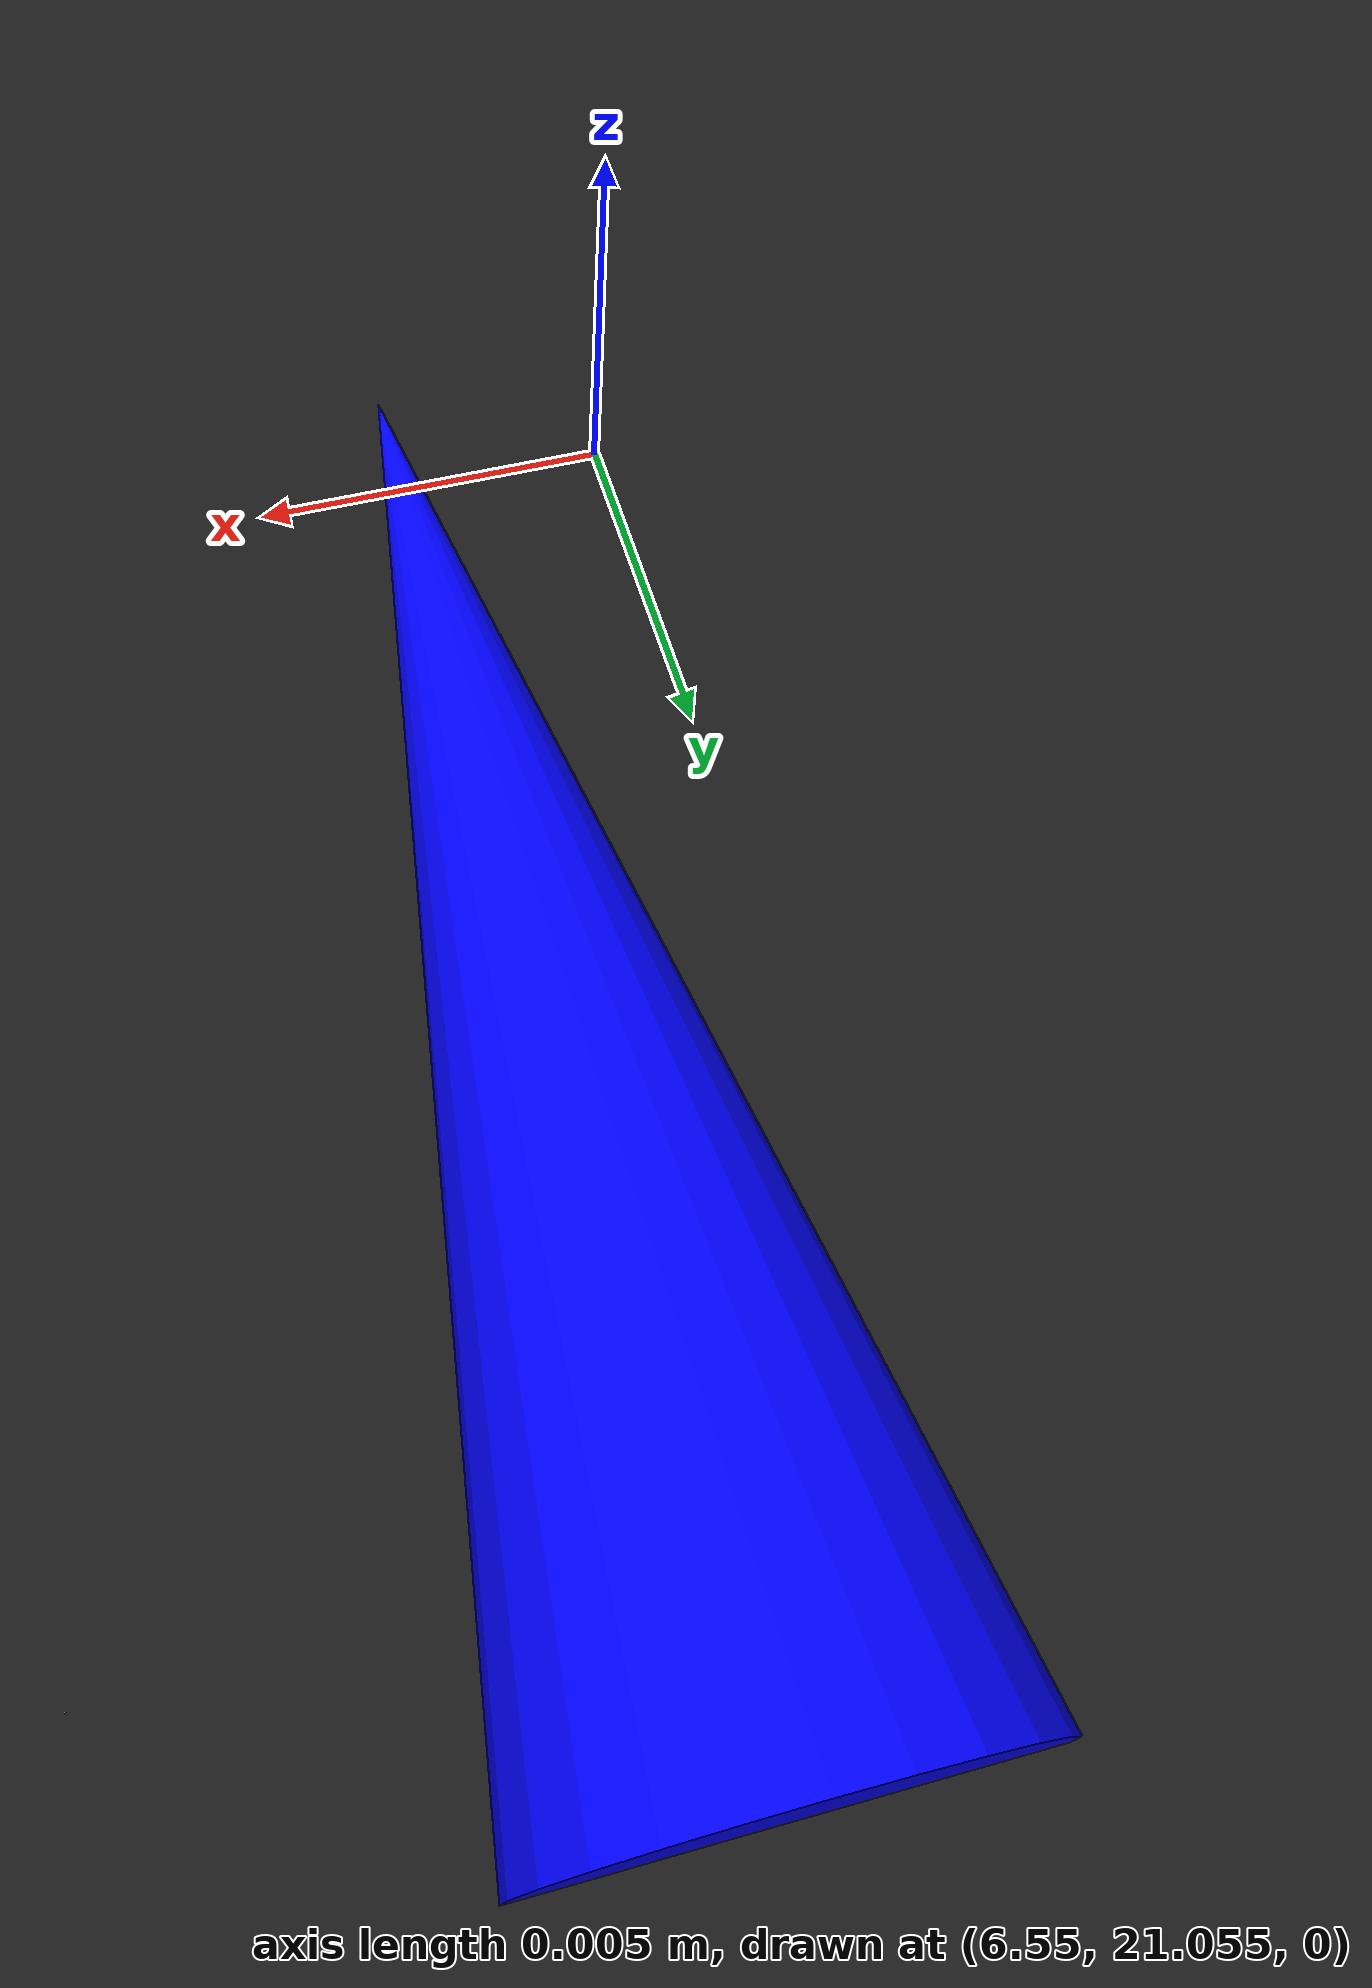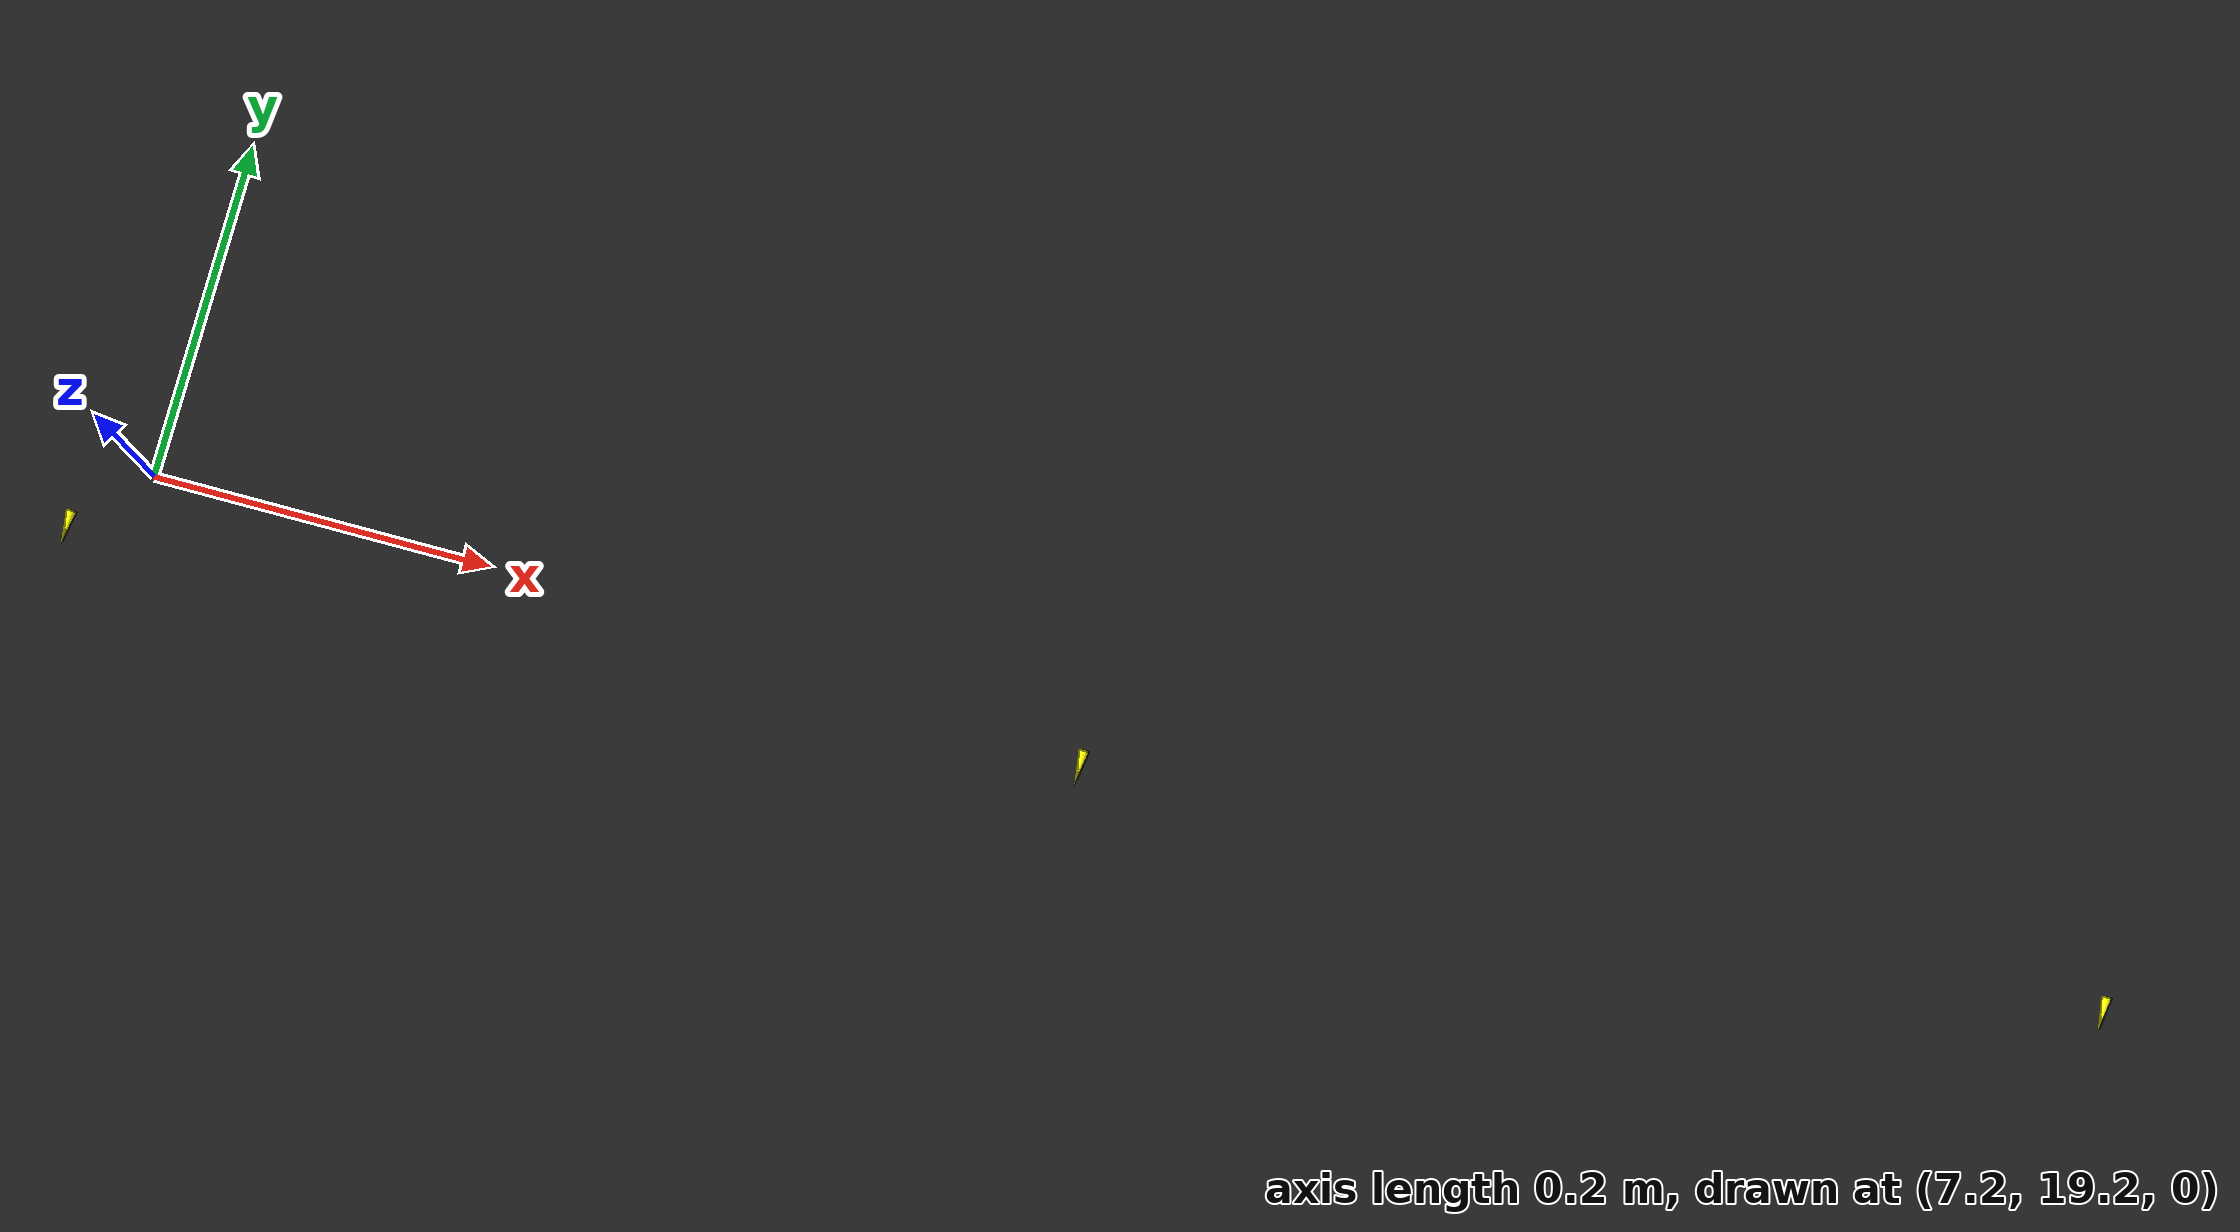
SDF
<sdf version="1.9">
	<world name="track">
		<physics name="1ms" type="ignored">
			<max_step_size>
				0.001
			</max_step_size>
			<real_time_factor>
				1.0
			</real_time_factor>
		</physics>
		<gravity>
			0 0 -9.8
		</gravity>
		<magnetic_field>
			6e-06 2.3e-05 -4.2e-05
		</magnetic_field>
		<atmosphere type="adiabatic" />
		<plugin name="gz::sim::systems::Physics" filename="gz-sim-physics-system" />
		<plugin name="gz::sim::systems::UserCommands" filename="gz-sim-user-commands-system" />
		<plugin name="gz::sim::systems::SceneBroadcaster" filename="gz-sim-scene-broadcaster-system" />
		<gui fullscreen="0">
			<plugin filename="MinimalScene" name="3D View">
				<gz-gui>
					<title>
						3D View
					</title>
					<property type="bool" key="showTitleBar">
						false
					</property>
					<property type="string" key="state">
						docked
					</property>
				</gz-gui>
				<engine>
					ogre2
				</engine>
				<scene>
					scene
				</scene>
				<ambient_light>
					0.4 0.4 0.4
				</ambient_light>
				<background_color>
					0.8 0.8 0.8
				</background_color>
				<camera_pose>
					-6 0 6 0 0.5 0
				</camera_pose>
			</plugin>
			<plugin filename="EntityContextMenuPlugin" name="Entity context menu">
				<gz-gui>
					<property key="state" type="string">
						floating
					</property>
					<property key="width" type="double">
						5
					</property>
					<property key="height" type="double">
						5
					</property>
					<property key="showTitleBar" type="bool">
						false
					</property>
				</gz-gui>
			</plugin>
			<plugin filename="GzSceneManager" name="Scene Manager">
				<gz-gui>
					<property key="resizable" type="bool">
						false
					</property>
					<property key="width" type="double">
						5
					</property>
					<property key="height" type="double">
						5
					</property>
					<property key="state" type="string">
						floating
					</property>
					<property key="showTitleBar" type="bool">
						false
					</property>
				</gz-gui>
			</plugin>
			<plugin filename="InteractiveViewControl" name="Interactive view control">
				<gz-gui>
					<property key="resizable" type="bool">
						false
					</property>
					<property key="width" type="double">
						5
					</property>
					<property key="height" type="double">
						5
					</property>
					<property key="state" type="string">
						floating
					</property>
					<property key="showTitleBar" type="bool">
						false
					</property>
				</gz-gui>
			</plugin>
			<plugin filename="CameraTracking" name="Camera Tracking">
				<gz-gui>
					<property key="resizable" type="bool">
						false
					</property>
					<property key="width" type="double">
						5
					</property>
					<property key="height" type="double">
						5
					</property>
					<property key="state" type="string">
						floating
					</property>
					<property key="showTitleBar" type="bool">
						false
					</property>
				</gz-gui>
			</plugin>
			<plugin name="World control" filename="WorldControl">
				<gz-gui>
					<title>
						World control
					</title>
					<property type="bool" key="showTitleBar">
						0
					</property>
					<property type="bool" key="resizable">
						0
					</property>
					<property type="double" key="height">
						72
					</property>
					<property type="double" key="z">
						1
					</property>
					<property type="string" key="state">
						floating
					</property>
					<anchors target="3D View">
						<line own="left" target="left" />
						<line own="bottom" target="bottom" />
					</anchors>
				</gz-gui>
				<play_pause>
					1
				</play_pause>
				<step>
					1
				</step>
				<start_paused>
					1
				</start_paused>
			</plugin>
			<plugin name="World stats" filename="WorldStats">
				<gz-gui>
					<title>
						World stats
					</title>
					<property type="bool" key="showTitleBar">
						0
					</property>
					<property type="bool" key="resizable">
						0
					</property>
					<property type="double" key="height">
						110
					</property>
					<property type="double" key="width">
						290
					</property>
					<property type="double" key="z">
						1
					</property>
					<property type="string" key="state">
						floating
					</property>
					<anchors target="3D View">
						<line own="right" target="right" />
						<line own="bottom" target="bottom" />
					</anchors>
				</gz-gui>
				<sim_time>
					1
				</sim_time>
				<real_time>
					1
				</real_time>
				<real_time_factor>
					1
				</real_time_factor>
				<iterations>
					1
				</iterations>
			</plugin>
			<plugin filename="VisualizeLidar" name="Visualize Lidar">
			</plugin>
			<plugin filename="ImageDisplay" name="Image Display">
			</plugin>
			<plugin filename="ComponentInspector" name="Component inspector">
				<ignition-gui>
					<property type="string" key="state">
						docked
					</property>
				</ignition-gui>
			</plugin>
			<plugin filename="EntityTree" name="Entity tree">
				<ignition-gui>
					<property type="string" key="state">
						docked
					</property>
				</ignition-gui>
			</plugin>
		</gui>
		<plugin filename="gz-sim-sensors-system" name="gz::sim::systems::Sensors">
			<render_engine>
				ogre2
			</render_engine>
		</plugin>
		<scene>
			<ambient>
				1 1 1 1
			</ambient>
			<background>
				0.8 0.8 0.8 1
			</background>
			<shadows>
				1
			</shadows>
		</scene>
		<light name="sun" type="directional">
			<cast_shadows>
				1
			</cast_shadows>
			<pose>
				0 0 10 0 0 0
			</pose>
			<diffuse>
				0.8 0.8 0.8 1
			</diffuse>
			<specular>
				0.8 0.8 0.8 1
			</specular>
			<attenuation>
				<range>
					1000
				</range>
				<constant>
					0.9
				</constant>
				<linear>
					0.01
				</linear>
				<quadratic>
					0.001
				</quadratic>
			</attenuation>
			<direction>
				-0.5 0.1 -0.9
			</direction>
		</light>
		<model name="ground_plane">
			<static>
				true
			</static>
			<link name="link">
				<collision name="collision">
					<geometry>
						<plane>
							<normal>
								0 0 1
							</normal>
							<size>
								100 100
							</size>
						</plane>
					</geometry>
					<surface>
						<friction>
							<dart />
						</friction>
						<bounce />
						<contact />
					</surface>
				</collision>
				<visual name="visual">
					<geometry>
						<plane>
							<normal>
								0 0 1
							</normal>
							<size>
								100 100
							</size>
						</plane>
					</geometry>
					<material>
						<ambient>
							0.1 0.1 0.1 1
						</ambient>
						<diffuse>
							0.1 0.1 0.1 1
						</diffuse>
						<specular>
							0.8 0.8 0.8 1
						</specular>
					</material>
				</visual>
				<pose>
					0 0 0 0 -0 0
				</pose>
				<inertial>
					<pose>
						0 0 0 0 -0 0
					</pose>
					<mass>
						1
					</mass>
					<inertia>
						<ixx>
							1
						</ixx>
						<ixy>
							0
						</ixy>
						<ixz>
							0
						</ixz>
						<iyy>
							1
						</iyy>
						<iyz>
							0
						</iyz>
						<izz>
							1
						</izz>
					</inertia>
				</inertial>
				<enable_wind>
					false
				</enable_wind>
			</link>
			<pose>
				0 0 0 0 -0 0
			</pose>
			<self_collide>
				false
			</self_collide>
		</model>
		<model name="cones">
			<pose>
				0 0 0 0 0 0
			</pose>
			<link name="cone_0_link">
				<collision name="cone_0_collision">
					<geometry>
						<mesh>
							<uri>
								/home/ubuntu/psd_ws/src/psd_gazebo_sim/psd_gazebo_worlds/world/models/cone/meshes/cone.stl
							</uri>
							<scale>
								0.001 0.001 0.001
							</scale>
						</mesh>
					</geometry>
				</collision>
				<visual name="cone_0_visual">
					<geometry>
						<mesh>
							<uri>
								/home/ubuntu/psd_ws/src/psd_gazebo_sim/psd_gazebo_worlds/world/models/cone/meshes/cone.stl
							</uri>
							<scale>
								0.001 0.001 0.001
							</scale>
						</mesh>
					</geometry>
					<material>
						<ambient>
							1 1 0 1
						</ambient>
						<diffuse>
							1 1 0 1
						</diffuse>
						<specular>
							1 1 0 1
						</specular>
					</material>
				</visual>
				<pose>
					5.365514631340422 19.110801933862014 0.0 1.57 0 0
				</pose>
				<enable_wind>
					false
				</enable_wind>
			</link>
			<link name="cone_1_link">
				<collision name="cone_1_collision">
					<geometry>
						<mesh>
							<uri>
								/home/ubuntu/psd_ws/src/psd_gazebo_sim/psd_gazebo_worlds/world/models/cone/meshes/cone.stl
							</uri>
							<scale>
								0.001 0.001 0.001
							</scale>
						</mesh>
					</geometry>
				</collision>
				<visual name="cone_1_visual">
					<geometry>
						<mesh>
							<uri>
								/home/ubuntu/psd_ws/src/psd_gazebo_sim/psd_gazebo_worlds/world/models/cone/meshes/cone.stl
							</uri>
							<scale>
								0.001 0.001 0.001
							</scale>
						</mesh>
					</geometry>
					<material>
						<ambient>
							1 1 0 1
						</ambient>
						<diffuse>
							1 1 0 1
						</diffuse>
						<specular>
							1 1 0 1
						</specular>
					</material>
				</visual>
				<pose>
					5.964740565412263 19.13025210124988 0.0 1.57 0 0
				</pose>
				<enable_wind>
					false
				</enable_wind>
			</link>
			<link name="cone_2_link">
				<collision name="cone_2_collision">
					<geometry>
						<mesh>
							<uri>
								/home/ubuntu/psd_ws/src/psd_gazebo_sim/psd_gazebo_worlds/world/models/cone/meshes/cone.stl
							</uri>
							<scale>
								0.001 0.001 0.001
							</scale>
						</mesh>
					</geometry>
				</collision>
				<visual name="cone_2_visual">
					<geometry>
						<mesh>
							<uri>
								/home/ubuntu/psd_ws/src/psd_gazebo_sim/psd_gazebo_worlds/world/models/cone/meshes/cone.stl
							</uri>
							<scale>
								0.001 0.001 0.001
							</scale>
						</mesh>
					</geometry>
					<material>
						<ambient>
							1 1 0 1
						</ambient>
						<diffuse>
							1 1 0 1
						</diffuse>
						<specular>
							1 1 0 1
						</specular>
					</material>
				</visual>
				<pose>
					6.562635671015661 19.149845757593543 0.0 1.57 0 0
				</pose>
				<enable_wind>
					false
				</enable_wind>
			</link>
			<link name="cone_3_link">
				<collision name="cone_3_collision">
					<geometry>
						<mesh>
							<uri>
								/home/ubuntu/psd_ws/src/psd_gazebo_sim/psd_gazebo_worlds/world/models/cone/meshes/cone.stl
							</uri>
							<scale>
								0.001 0.001 0.001
							</scale>
						</mesh>
					</geometry>
				</collision>
				<visual name="cone_3_visual">
					<geometry>
						<mesh>
							<uri>
								/home/ubuntu/psd_ws/src/psd_gazebo_sim/psd_gazebo_worlds/world/models/cone/meshes/cone.stl
							</uri>
							<scale>
								0.001 0.001 0.001
							</scale>
						</mesh>
					</geometry>
					<material>
						<ambient>
							1 1 0 1
						</ambient>
						<diffuse>
							1 1 0 1
						</diffuse>
						<specular>
							1 1 0 1
						</specular>
					</material>
				</visual>
				<pose>
					7.159228228615251 19.168703466283013 0.0 1.57 0 0
				</pose>
				<enable_wind>
					false
				</enable_wind>
			</link>
			<link name="cone_4_link">
				<collision name="cone_4_collision">
					<geometry>
						<mesh>
							<uri>
								/home/ubuntu/psd_ws/src/psd_gazebo_sim/psd_gazebo_worlds/world/models/cone/meshes/cone.stl
							</uri>
							<scale>
								0.001 0.001 0.001
							</scale>
						</mesh>
					</geometry>
				</collision>
				<visual name="cone_4_visual">
					<geometry>
						<mesh>
							<uri>
								/home/ubuntu/psd_ws/src/psd_gazebo_sim/psd_gazebo_worlds/world/models/cone/meshes/cone.stl
							</uri>
							<scale>
								0.001 0.001 0.001
							</scale>
						</mesh>
					</geometry>
					<material>
						<ambient>
							1 1 0 1
						</ambient>
						<diffuse>
							1 1 0 1
						</diffuse>
						<specular>
							1 1 0 1
						</specular>
					</material>
				</visual>
				<pose>
					7.754543277370971 19.185951549543113 0.0 1.57 0 0
				</pose>
				<enable_wind>
					false
				</enable_wind>
			</link>
			<link name="cone_5_link">
				<collision name="cone_5_collision">
					<geometry>
						<mesh>
							<uri>
								/home/ubuntu/psd_ws/src/psd_gazebo_sim/psd_gazebo_worlds/world/models/cone/meshes/cone.stl
							</uri>
							<scale>
								0.001 0.001 0.001
							</scale>
						</mesh>
					</geometry>
				</collision>
				<visual name="cone_5_visual">
					<geometry>
						<mesh>
							<uri>
								/home/ubuntu/psd_ws/src/psd_gazebo_sim/psd_gazebo_worlds/world/models/cone/meshes/cone.stl
							</uri>
							<scale>
								0.001 0.001 0.001
							</scale>
						</mesh>
					</geometry>
					<material>
						<ambient>
							1 1 0 1
						</ambient>
						<diffuse>
							1 1 0 1
						</diffuse>
						<specular>
							1 1 0 1
						</specular>
					</material>
				</visual>
				<pose>
					8.348598776876031 19.20072199169762 0.0 1.57 0 0
				</pose>
				<enable_wind>
					false
				</enable_wind>
			</link>
			<link name="cone_6_link">
				<collision name="cone_6_collision">
					<geometry>
						<mesh>
							<uri>
								/home/ubuntu/psd_ws/src/psd_gazebo_sim/psd_gazebo_worlds/world/models/cone/meshes/cone.stl
							</uri>
							<scale>
								0.001 0.001 0.001
							</scale>
						</mesh>
					</geometry>
				</collision>
				<visual name="cone_6_visual">
					<geometry>
						<mesh>
							<uri>
								/home/ubuntu/psd_ws/src/psd_gazebo_sim/psd_gazebo_worlds/world/models/cone/meshes/cone.stl
							</uri>
							<scale>
								0.001 0.001 0.001
							</scale>
						</mesh>
					</geometry>
					<material>
						<ambient>
							1 1 0 1
						</ambient>
						<diffuse>
							1 1 0 1
						</diffuse>
						<specular>
							1 1 0 1
						</specular>
					</material>
				</visual>
				<pose>
					10.12320195090182 19.22157188820107 0.0 1.57 0 0
				</pose>
				<enable_wind>
					false
				</enable_wind>
			</link>
			<link name="cone_7_link">
				<collision name="cone_7_collision">
					<geometry>
						<mesh>
							<uri>
								/home/ubuntu/psd_ws/src/psd_gazebo_sim/psd_gazebo_worlds/world/models/cone/meshes/cone.stl
							</uri>
							<scale>
								0.001 0.001 0.001
							</scale>
						</mesh>
					</geometry>
				</collision>
				<visual name="cone_7_visual">
					<geometry>
						<mesh>
							<uri>
								/home/ubuntu/psd_ws/src/psd_gazebo_sim/psd_gazebo_worlds/world/models/cone/meshes/cone.stl
							</uri>
							<scale>
								0.001 0.001 0.001
							</scale>
						</mesh>
					</geometry>
					<material>
						<ambient>
							1 1 0 1
						</ambient>
						<diffuse>
							1 1 0 1
						</diffuse>
						<specular>
							1 1 0 1
						</specular>
					</material>
				</visual>
				<pose>
					10.71212526738323 19.21786514161583 0.0 1.57 0 0
				</pose>
				<enable_wind>
					false
				</enable_wind>
			</link>
			<link name="cone_8_link">
				<collision name="cone_8_collision">
					<geometry>
						<mesh>
							<uri>
								/home/ubuntu/psd_ws/src/psd_gazebo_sim/psd_gazebo_worlds/world/models/cone/meshes/cone.stl
							</uri>
							<scale>
								0.001 0.001 0.001
							</scale>
						</mesh>
					</geometry>
				</collision>
				<visual name="cone_8_visual">
					<geometry>
						<mesh>
							<uri>
								/home/ubuntu/psd_ws/src/psd_gazebo_sim/psd_gazebo_worlds/world/models/cone/meshes/cone.stl
							</uri>
							<scale>
								0.001 0.001 0.001
							</scale>
						</mesh>
					</geometry>
					<material>
						<ambient>
							1 1 0 1
						</ambient>
						<diffuse>
							1 1 0 1
						</diffuse>
						<specular>
							1 1 0 1
						</specular>
					</material>
				</visual>
				<pose>
					11.299641250748362 19.20742738967495 0.0 1.57 0 0
				</pose>
				<enable_wind>
					false
				</enable_wind>
			</link>
			<link name="cone_9_link">
				<collision name="cone_9_collision">
					<geometry>
						<mesh>
							<uri>
								/home/ubuntu/psd_ws/src/psd_gazebo_sim/psd_gazebo_worlds/world/models/cone/meshes/cone.stl
							</uri>
							<scale>
								0.001 0.001 0.001
							</scale>
						</mesh>
					</geometry>
				</collision>
				<visual name="cone_9_visual">
					<geometry>
						<mesh>
							<uri>
								/home/ubuntu/psd_ws/src/psd_gazebo_sim/psd_gazebo_worlds/world/models/cone/meshes/cone.stl
							</uri>
							<scale>
								0.001 0.001 0.001
							</scale>
						</mesh>
					</geometry>
					<material>
						<ambient>
							1 1 0 1
						</ambient>
						<diffuse>
							1 1 0 1
						</diffuse>
						<specular>
							1 1 0 1
						</specular>
					</material>
				</visual>
				<pose>
					11.88564717200543 19.189427374825613 0.0 1.57 0 0
				</pose>
				<enable_wind>
					false
				</enable_wind>
			</link>
			<link name="cone_10_link">
				<collision name="cone_10_collision">
					<geometry>
						<mesh>
							<uri>
								/home/ubuntu/psd_ws/src/psd_gazebo_sim/psd_gazebo_worlds/world/models/cone/meshes/cone.stl
							</uri>
							<scale>
								0.001 0.001 0.001
							</scale>
						</mesh>
					</geometry>
				</collision>
				<visual name="cone_10_visual">
					<geometry>
						<mesh>
							<uri>
								/home/ubuntu/psd_ws/src/psd_gazebo_sim/psd_gazebo_worlds/world/models/cone/meshes/cone.stl
							</uri>
							<scale>
								0.001 0.001 0.001
							</scale>
						</mesh>
					</geometry>
					<material>
						<ambient>
							1 1 0 1
						</ambient>
						<diffuse>
							1 1 0 1
						</diffuse>
						<specular>
							1 1 0 1
						</specular>
					</material>
				</visual>
				<pose>
					12.47000759521337 19.16304179481803 0.0 1.57 0 0
				</pose>
				<enable_wind>
					false
				</enable_wind>
			</link>
			<link name="cone_11_link">
				<collision name="cone_11_collision">
					<geometry>
						<mesh>
							<uri>
								/home/ubuntu/psd_ws/src/psd_gazebo_sim/psd_gazebo_worlds/world/models/cone/meshes/cone.stl
							</uri>
							<scale>
								0.001 0.001 0.001
							</scale>
						</mesh>
					</geometry>
				</collision>
				<visual name="cone_11_visual">
					<geometry>
						<mesh>
							<uri>
								/home/ubuntu/psd_ws/src/psd_gazebo_sim/psd_gazebo_worlds/world/models/cone/meshes/cone.stl
							</uri>
							<scale>
								0.001 0.001 0.001
							</scale>
						</mesh>
					</geometry>
					<material>
						<ambient>
							1 1 0 1
						</ambient>
						<diffuse>
							1 1 0 1
						</diffuse>
						<specular>
							1 1 0 1
						</specular>
					</material>
				</visual>
				<pose>
					13.041051502435192 19.12601093430245 0.0 1.57 0 0
				</pose>
				<enable_wind>
					false
				</enable_wind>
			</link>
			<link name="cone_12_link">
				<collision name="cone_12_collision">
					<geometry>
						<mesh>
							<uri>
								/home/ubuntu/psd_ws/src/psd_gazebo_sim/psd_gazebo_worlds/world/models/cone/meshes/cone.stl
							</uri>
							<scale>
								0.001 0.001 0.001
							</scale>
						</mesh>
					</geometry>
				</collision>
				<visual name="cone_12_visual">
					<geometry>
						<mesh>
							<uri>
								/home/ubuntu/psd_ws/src/psd_gazebo_sim/psd_gazebo_worlds/world/models/cone/meshes/cone.stl
							</uri>
							<scale>
								0.001 0.001 0.001
							</scale>
						</mesh>
					</geometry>
					<material>
						<ambient>
							1 1 0 1
						</ambient>
						<diffuse>
							1 1 0 1
						</diffuse>
						<specular>
							1 1 0 1
						</specular>
					</material>
				</visual>
				<pose>
					13.581689096199652 19.06655367674996 0.0 1.57 0 0
				</pose>
				<enable_wind>
					false
				</enable_wind>
			</link>
			<link name="cone_13_link">
				<collision name="cone_13_collision">
					<geometry>
						<mesh>
							<uri>
								/home/ubuntu/psd_ws/src/psd_gazebo_sim/psd_gazebo_worlds/world/models/cone/meshes/cone.stl
							</uri>
							<scale>
								0.001 0.001 0.001
							</scale>
						</mesh>
					</geometry>
				</collision>
				<visual name="cone_13_visual">
					<geometry>
						<mesh>
							<uri>
								/home/ubuntu/psd_ws/src/psd_gazebo_sim/psd_gazebo_worlds/world/models/cone/meshes/cone.stl
							</uri>
							<scale>
								0.001 0.001 0.001
							</scale>
						</mesh>
					</geometry>
					<material>
						<ambient>
							1 1 0 1
						</ambient>
						<diffuse>
							1 1 0 1
						</diffuse>
						<specular>
							1 1 0 1
						</specular>
					</material>
				</visual>
				<pose>
					14.55431448947459 18.83039695679588 0.0 1.57 0 0
				</pose>
				<enable_wind>
					false
				</enable_wind>
			</link>
			<link name="cone_14_link">
				<collision name="cone_14_collision">
					<geometry>
						<mesh>
							<uri>
								/home/ubuntu/psd_ws/src/psd_gazebo_sim/psd_gazebo_worlds/world/models/cone/meshes/cone.stl
							</uri>
							<scale>
								0.001 0.001 0.001
							</scale>
						</mesh>
					</geometry>
				</collision>
				<visual name="cone_14_visual">
					<geometry>
						<mesh>
							<uri>
								/home/ubuntu/psd_ws/src/psd_gazebo_sim/psd_gazebo_worlds/world/models/cone/meshes/cone.stl
							</uri>
							<scale>
								0.001 0.001 0.001
							</scale>
						</mesh>
					</geometry>
					<material>
						<ambient>
							1 1 0 1
						</ambient>
						<diffuse>
							1 1 0 1
						</diffuse>
						<specular>
							1 1 0 1
						</specular>
					</material>
				</visual>
				<pose>
					14.97041312626016 18.63808357122464 0.0 1.57 0 0
				</pose>
				<enable_wind>
					false
				</enable_wind>
			</link>
			<link name="cone_15_link">
				<collision name="cone_15_collision">
					<geometry>
						<mesh>
							<uri>
								/home/ubuntu/psd_ws/src/psd_gazebo_sim/psd_gazebo_worlds/world/models/cone/meshes/cone.stl
							</uri>
							<scale>
								0.001 0.001 0.001
							</scale>
						</mesh>
					</geometry>
				</collision>
				<visual name="cone_15_visual">
					<geometry>
						<mesh>
							<uri>
								/home/ubuntu/psd_ws/src/psd_gazebo_sim/psd_gazebo_worlds/world/models/cone/meshes/cone.stl
							</uri>
							<scale>
								0.001 0.001 0.001
							</scale>
						</mesh>
					</geometry>
					<material>
						<ambient>
							1 1 0 1
						</ambient>
						<diffuse>
							1 1 0 1
						</diffuse>
						<specular>
							1 1 0 1
						</specular>
					</material>
				</visual>
				<pose>
					15.64211758381664 18.078554715443932 0.0 1.57 0 0
				</pose>
				<enable_wind>
					false
				</enable_wind>
			</link>
			<link name="cone_16_link">
				<collision name="cone_16_collision">
					<geometry>
						<mesh>
							<uri>
								/home/ubuntu/psd_ws/src/psd_gazebo_sim/psd_gazebo_worlds/world/models/cone/meshes/cone.stl
							</uri>
							<scale>
								0.001 0.001 0.001
							</scale>
						</mesh>
					</geometry>
				</collision>
				<visual name="cone_16_visual">
					<geometry>
						<mesh>
							<uri>
								/home/ubuntu/psd_ws/src/psd_gazebo_sim/psd_gazebo_worlds/world/models/cone/meshes/cone.stl
							</uri>
							<scale>
								0.001 0.001 0.001
							</scale>
						</mesh>
					</geometry>
					<material>
						<ambient>
							1 1 0 1
						</ambient>
						<diffuse>
							1 1 0 1
						</diffuse>
						<specular>
							1 1 0 1
						</specular>
					</material>
				</visual>
				<pose>
					15.910013498130139 17.706310771870402 0.0 1.57 0 0
				</pose>
				<enable_wind>
					false
				</enable_wind>
			</link>
			<link name="cone_17_link">
				<collision name="cone_17_collision">
					<geometry>
						<mesh>
							<uri>
								/home/ubuntu/psd_ws/src/psd_gazebo_sim/psd_gazebo_worlds/world/models/cone/meshes/cone.stl
							</uri>
							<scale>
								0.001 0.001 0.001
							</scale>
						</mesh>
					</geometry>
				</collision>
				<visual name="cone_17_visual">
					<geometry>
						<mesh>
							<uri>
								/home/ubuntu/psd_ws/src/psd_gazebo_sim/psd_gazebo_worlds/world/models/cone/meshes/cone.stl
							</uri>
							<scale>
								0.001 0.001 0.001
							</scale>
						</mesh>
					</geometry>
					<material>
						<ambient>
							1 1 0 1
						</ambient>
						<diffuse>
							1 1 0 1
						</diffuse>
						<specular>
							1 1 0 1
						</specular>
					</material>
				</visual>
				<pose>
					16.1277216977834 17.285362386631014 0.0 1.57 0 0
				</pose>
				<enable_wind>
					false
				</enable_wind>
			</link>
			<link name="cone_18_link">
				<collision name="cone_18_collision">
					<geometry>
						<mesh>
							<uri>
								/home/ubuntu/psd_ws/src/psd_gazebo_sim/psd_gazebo_worlds/world/models/cone/meshes/cone.stl
							</uri>
							<scale>
								0.001 0.001 0.001
							</scale>
						</mesh>
					</geometry>
				</collision>
				<visual name="cone_18_visual">
					<geometry>
						<mesh>
							<uri>
								/home/ubuntu/psd_ws/src/psd_gazebo_sim/psd_gazebo_worlds/world/models/cone/meshes/cone.stl
							</uri>
							<scale>
								0.001 0.001 0.001
							</scale>
						</mesh>
					</geometry>
					<material>
						<ambient>
							1 1 0 1
						</ambient>
						<diffuse>
							1 1 0 1
						</diffuse>
						<specular>
							1 1 0 1
						</specular>
					</material>
				</visual>
				<pose>
					16.294295500331152 16.825754413038084 0.0 1.57 0 0
				</pose>
				<enable_wind>
					false
				</enable_wind>
			</link>
			<link name="cone_19_link">
				<collision name="cone_19_collision">
					<geometry>
						<mesh>
							<uri>
								/home/ubuntu/psd_ws/src/psd_gazebo_sim/psd_gazebo_worlds/world/models/cone/meshes/cone.stl
							</uri>
							<scale>
								0.001 0.001 0.001
							</scale>
						</mesh>
					</geometry>
				</collision>
				<visual name="cone_19_visual">
					<geometry>
						<mesh>
							<uri>
								/home/ubuntu/psd_ws/src/psd_gazebo_sim/psd_gazebo_worlds/world/models/cone/meshes/cone.stl
							</uri>
							<scale>
								0.001 0.001 0.001
							</scale>
						</mesh>
					</geometry>
					<material>
						<ambient>
							1 1 0 1
						</ambient>
						<diffuse>
							1 1 0 1
						</diffuse>
						<specular>
							1 1 0 1
						</specular>
					</material>
				</visual>
				<pose>
					16.45404444091331 15.871680009410992 0.0 1.57 0 0
				</pose>
				<enable_wind>
					false
				</enable_wind>
			</link>
			<link name="cone_20_link">
				<collision name="cone_20_collision">
					<geometry>
						<mesh>
							<uri>
								/home/ubuntu/psd_ws/src/psd_gazebo_sim/psd_gazebo_worlds/world/models/cone/meshes/cone.stl
							</uri>
							<scale>
								0.001 0.001 0.001
							</scale>
						</mesh>
					</geometry>
				</collision>
				<visual name="cone_20_visual">
					<geometry>
						<mesh>
							<uri>
								/home/ubuntu/psd_ws/src/psd_gazebo_sim/psd_gazebo_worlds/world/models/cone/meshes/cone.stl
							</uri>
							<scale>
								0.001 0.001 0.001
							</scale>
						</mesh>
					</geometry>
					<material>
						<ambient>
							1 1 0 1
						</ambient>
						<diffuse>
							1 1 0 1
						</diffuse>
						<specular>
							1 1 0 1
						</specular>
					</material>
				</visual>
				<pose>
					16.43842788566033 15.399601279681972 0.0 1.57 0 0
				</pose>
				<enable_wind>
					false
				</enable_wind>
			</link>
			<link name="cone_21_link">
				<collision name="cone_21_collision">
					<geometry>
						<mesh>
							<uri>
								/home/ubuntu/psd_ws/src/psd_gazebo_sim/psd_gazebo_worlds/world/models/cone/meshes/cone.stl
							</uri>
							<scale>
								0.001 0.001 0.001
							</scale>
						</mesh>
					</geometry>
				</collision>
				<visual name="cone_21_visual">
					<geometry>
						<mesh>
							<uri>
								/home/ubuntu/psd_ws/src/psd_gazebo_sim/psd_gazebo_worlds/world/models/cone/meshes/cone.stl
							</uri>
							<scale>
								0.001 0.001 0.001
							</scale>
						</mesh>
					</geometry>
					<material>
						<ambient>
							1 1 0 1
						</ambient>
						<diffuse>
							1 1 0 1
						</diffuse>
						<specular>
							1 1 0 1
						</specular>
					</material>
				</visual>
				<pose>
					16.356500140432672 14.942758602394552 0.0 1.57 0 0
				</pose>
				<enable_wind>
					false
				</enable_wind>
			</link>
			<link name="cone_22_link">
				<collision name="cone_22_collision">
					<geometry>
						<mesh>
							<uri>
								/home/ubuntu/psd_ws/src/psd_gazebo_sim/psd_gazebo_worlds/world/models/cone/meshes/cone.stl
							</uri>
							<scale>
								0.001 0.001 0.001
							</scale>
						</mesh>
					</geometry>
				</collision>
				<visual name="cone_22_visual">
					<geometry>
						<mesh>
							<uri>
								/home/ubuntu/psd_ws/src/psd_gazebo_sim/psd_gazebo_worlds/world/models/cone/meshes/cone.stl
							</uri>
							<scale>
								0.001 0.001 0.001
							</scale>
						</mesh>
					</geometry>
					<material>
						<ambient>
							1 1 0 1
						</ambient>
						<diffuse>
							1 1 0 1
						</diffuse>
						<specular>
							1 1 0 1
						</specular>
					</material>
				</visual>
				<pose>
					16.20837454523762 14.511568577870843 0.0 1.57 0 0
				</pose>
				<enable_wind>
					false
				</enable_wind>
			</link>
			<link name="cone_23_link">
				<collision name="cone_23_collision">
					<geometry>
						<mesh>
							<uri>
								/home/ubuntu/psd_ws/src/psd_gazebo_sim/psd_gazebo_worlds/world/models/cone/meshes/cone.stl
							</uri>
							<scale>
								0.001 0.001 0.001
							</scale>
						</mesh>
					</geometry>
				</collision>
				<visual name="cone_23_visual">
					<geometry>
						<mesh>
							<uri>
								/home/ubuntu/psd_ws/src/psd_gazebo_sim/psd_gazebo_worlds/world/models/cone/meshes/cone.stl
							</uri>
							<scale>
								0.001 0.001 0.001
							</scale>
						</mesh>
					</geometry>
					<material>
						<ambient>
							1 1 0 1
						</ambient>
						<diffuse>
							1 1 0 1
						</diffuse>
						<specular>
							1 1 0 1
						</specular>
					</material>
				</visual>
				<pose>
					15.99358132323365 14.11083754486181 0.0 1.57 0 0
				</pose>
				<enable_wind>
					false
				</enable_wind>
			</link>
			<link name="cone_24_link">
				<collision name="cone_24_collision">
					<geometry>
						<mesh>
							<uri>
								/home/ubuntu/psd_ws/src/psd_gazebo_sim/psd_gazebo_worlds/world/models/cone/meshes/cone.stl
							</uri>
							<scale>
								0.001 0.001 0.001
							</scale>
						</mesh>
					</geometry>
				</collision>
				<visual name="cone_24_visual">
					<geometry>
						<mesh>
							<uri>
								/home/ubuntu/psd_ws/src/psd_gazebo_sim/psd_gazebo_worlds/world/models/cone/meshes/cone.stl
							</uri>
							<scale>
								0.001 0.001 0.001
							</scale>
						</mesh>
					</geometry>
					<material>
						<ambient>
							1 1 0 1
						</ambient>
						<diffuse>
							1 1 0 1
						</diffuse>
						<specular>
							1 1 0 1
						</specular>
					</material>
				</visual>
				<pose>
					15.371974790252331 13.391132889904732 0.0 1.57 0 0
				</pose>
				<enable_wind>
					false
				</enable_wind>
			</link>
			<link name="cone_25_link">
				<collision name="cone_25_collision">
					<geometry>
						<mesh>
							<uri>
								/home/ubuntu/psd_ws/src/psd_gazebo_sim/psd_gazebo_worlds/world/models/cone/meshes/cone.stl
							</uri>
							<scale>
								0.001 0.001 0.001
							</scale>
						</mesh>
					</geometry>
				</collision>
				<visual name="cone_25_visual">
					<geometry>
						<mesh>
							<uri>
								/home/ubuntu/psd_ws/src/psd_gazebo_sim/psd_gazebo_worlds/world/models/cone/meshes/cone.stl
							</uri>
							<scale>
								0.001 0.001 0.001
							</scale>
						</mesh>
					</geometry>
					<material>
						<ambient>
							1 1 0 1
						</ambient>
						<diffuse>
							1 1 0 1
						</diffuse>
						<specular>
							1 1 0 1
						</specular>
					</material>
				</visual>
				<pose>
					14.55709628279117 12.808898370122453 0.0 1.57 0 0
				</pose>
				<enable_wind>
					false
				</enable_wind>
			</link>
			<link name="cone_26_link">
				<collision name="cone_26_collision">
					<geometry>
						<mesh>
							<uri>
								/home/ubuntu/psd_ws/src/psd_gazebo_sim/psd_gazebo_worlds/world/models/cone/meshes/cone.stl
							</uri>
							<scale>
								0.001 0.001 0.001
							</scale>
						</mesh>
					</geometry>
				</collision>
				<visual name="cone_26_visual">
					<geometry>
						<mesh>
							<uri>
								/home/ubuntu/psd_ws/src/psd_gazebo_sim/psd_gazebo_worlds/world/models/cone/meshes/cone.stl
							</uri>
							<scale>
								0.001 0.001 0.001
							</scale>
						</mesh>
					</geometry>
					<material>
						<ambient>
							1 1 0 1
						</ambient>
						<diffuse>
							1 1 0 1
						</diffuse>
						<specular>
							1 1 0 1
						</specular>
					</material>
				</visual>
				<pose>
					14.11033563835196 12.587555216181531 0.0 1.57 0 0
				</pose>
				<enable_wind>
					false
				</enable_wind>
			</link>
			<link name="cone_27_link">
				<collision name="cone_27_collision">
					<geometry>
						<mesh>
							<uri>
								/home/ubuntu/psd_ws/src/psd_gazebo_sim/psd_gazebo_worlds/world/models/cone/meshes/cone.stl
							</uri>
							<scale>
								0.001 0.001 0.001
							</scale>
						</mesh>
					</geometry>
				</collision>
				<visual name="cone_27_visual">
					<geometry>
						<mesh>
							<uri>
								/home/ubuntu/psd_ws/src/psd_gazebo_sim/psd_gazebo_worlds/world/models/cone/meshes/cone.stl
							</uri>
							<scale>
								0.001 0.001 0.001
							</scale>
						</mesh>
					</geometry>
					<material>
						<ambient>
							1 1 0 1
						</ambient>
						<diffuse>
							1 1 0 1
						</diffuse>
						<specular>
							1 1 0 1
						</specular>
					</material>
				</visual>
				<pose>
					13.646279059230352 12.420128168078872 0.0 1.57 0 0
				</pose>
				<enable_wind>
					false
				</enable_wind>
			</link>
			<link name="cone_28_link">
				<collision name="cone_28_collision">
					<geometry>
						<mesh>
							<uri>
								/home/ubuntu/psd_ws/src/psd_gazebo_sim/psd_gazebo_worlds/world/models/cone/meshes/cone.stl
							</uri>
							<scale>
								0.001 0.001 0.001
							</scale>
						</mesh>
					</geometry>
				</collision>
				<visual name="cone_28_visual">
					<geometry>
						<mesh>
							<uri>
								/home/ubuntu/psd_ws/src/psd_gazebo_sim/psd_gazebo_worlds/world/models/cone/meshes/cone.stl
							</uri>
							<scale>
								0.001 0.001 0.001
							</scale>
						</mesh>
					</geometry>
					<material>
						<ambient>
							1 1 0 1
						</ambient>
						<diffuse>
							1 1 0 1
						</diffuse>
						<specular>
							1 1 0 1
						</specular>
					</material>
				</visual>
				<pose>
					13.17068350719518 12.310419448693313 0.0 1.57 0 0
				</pose>
				<enable_wind>
					false
				</enable_wind>
			</link>
			<link name="cone_29_link">
				<collision name="cone_29_collision">
					<geometry>
						<mesh>
							<uri>
								/home/ubuntu/psd_ws/src/psd_gazebo_sim/psd_gazebo_worlds/world/models/cone/meshes/cone.stl
							</uri>
							<scale>
								0.001 0.001 0.001
							</scale>
						</mesh>
					</geometry>
				</collision>
				<visual name="cone_29_visual">
					<geometry>
						<mesh>
							<uri>
								/home/ubuntu/psd_ws/src/psd_gazebo_sim/psd_gazebo_worlds/world/models/cone/meshes/cone.stl
							</uri>
							<scale>
								0.001 0.001 0.001
							</scale>
						</mesh>
					</geometry>
					<material>
						<ambient>
							1 1 0 1
						</ambient>
						<diffuse>
							1 1 0 1
						</diffuse>
						<specular>
							1 1 0 1
						</specular>
					</material>
				</visual>
				<pose>
					12.69032803057931 12.261562816865302 0.0 1.57 0 0
				</pose>
				<enable_wind>
					false
				</enable_wind>
			</link>
			<link name="cone_30_link">
				<collision name="cone_30_collision">
					<geometry>
						<mesh>
							<uri>
								/home/ubuntu/psd_ws/src/psd_gazebo_sim/psd_gazebo_worlds/world/models/cone/meshes/cone.stl
							</uri>
							<scale>
								0.001 0.001 0.001
							</scale>
						</mesh>
					</geometry>
				</collision>
				<visual name="cone_30_visual">
					<geometry>
						<mesh>
							<uri>
								/home/ubuntu/psd_ws/src/psd_gazebo_sim/psd_gazebo_worlds/world/models/cone/meshes/cone.stl
							</uri>
							<scale>
								0.001 0.001 0.001
							</scale>
						</mesh>
					</geometry>
					<material>
						<ambient>
							1 1 0 1
						</ambient>
						<diffuse>
							1 1 0 1
						</diffuse>
						<specular>
							1 1 0 1
						</specular>
					</material>
				</visual>
				<pose>
					12.20867904572405 12.275499276402233 0.0 1.57 0 0
				</pose>
				<enable_wind>
					false
				</enable_wind>
			</link>
			<link name="cone_31_link">
				<collision name="cone_31_collision">
					<geometry>
						<mesh>
							<uri>
								/home/ubuntu/psd_ws/src/psd_gazebo_sim/psd_gazebo_worlds/world/models/cone/meshes/cone.stl
							</uri>
							<scale>
								0.001 0.001 0.001
							</scale>
						</mesh>
					</geometry>
				</collision>
				<visual name="cone_31_visual">
					<geometry>
						<mesh>
							<uri>
								/home/ubuntu/psd_ws/src/psd_gazebo_sim/psd_gazebo_worlds/world/models/cone/meshes/cone.stl
							</uri>
							<scale>
								0.001 0.001 0.001
							</scale>
						</mesh>
					</geometry>
					<material>
						<ambient>
							1 1 0 1
						</ambient>
						<diffuse>
							1 1 0 1
						</diffuse>
						<specular>
							1 1 0 1
						</specular>
					</material>
				</visual>
				<pose>
					11.722728008294931 12.350486889681113 0.0 1.57 0 0
				</pose>
				<enable_wind>
					false
				</enable_wind>
			</link>
			<link name="cone_32_link">
				<collision name="cone_32_collision">
					<geometry>
						<mesh>
							<uri>
								/home/ubuntu/psd_ws/src/psd_gazebo_sim/psd_gazebo_worlds/world/models/cone/meshes/cone.stl
							</uri>
							<scale>
								0.001 0.001 0.001
							</scale>
						</mesh>
					</geometry>
				</collision>
				<visual name="cone_32_visual">
					<geometry>
						<mesh>
							<uri>
								/home/ubuntu/psd_ws/src/psd_gazebo_sim/psd_gazebo_worlds/world/models/cone/meshes/cone.stl
							</uri>
							<scale>
								0.001 0.001 0.001
							</scale>
						</mesh>
					</geometry>
					<material>
						<ambient>
							1 1 0 1
						</ambient>
						<diffuse>
							1 1 0 1
						</diffuse>
						<specular>
							1 1 0 1
						</specular>
					</material>
				</visual>
				<pose>
					10.75994651673809 12.66625218214823 0.0 1.57 0 0
				</pose>
				<enable_wind>
					false
				</enable_wind>
			</link>
			<link name="cone_33_link">
				<collision name="cone_33_collision">
					<geometry>
						<mesh>
							<uri>
								/home/ubuntu/psd_ws/src/psd_gazebo_sim/psd_gazebo_worlds/world/models/cone/meshes/cone.stl
							</uri>
							<scale>
								0.001 0.001 0.001
							</scale>
						</mesh>
					</geometry>
				</collision>
				<visual name="cone_33_visual">
					<geometry>
						<mesh>
							<uri>
								/home/ubuntu/psd_ws/src/psd_gazebo_sim/psd_gazebo_worlds/world/models/cone/meshes/cone.stl
							</uri>
							<scale>
								0.001 0.001 0.001
							</scale>
						</mesh>
					</geometry>
					<material>
						<ambient>
							1 1 0 1
						</ambient>
						<diffuse>
							1 1 0 1
						</diffuse>
						<specular>
							1 1 0 1
						</specular>
					</material>
				</visual>
				<pose>
					9.827743761109641 13.170460850358321 0.0 1.57 0 0
				</pose>
				<enable_wind>
					false
				</enable_wind>
			</link>
			<link name="cone_34_link">
				<collision name="cone_34_collision">
					<geometry>
						<mesh>
							<uri>
								/home/ubuntu/psd_ws/src/psd_gazebo_sim/psd_gazebo_worlds/world/models/cone/meshes/cone.stl
							</uri>
							<scale>
								0.001 0.001 0.001
							</scale>
						</mesh>
					</geometry>
				</collision>
				<visual name="cone_34_visual">
					<geometry>
						<mesh>
							<uri>
								/home/ubuntu/psd_ws/src/psd_gazebo_sim/psd_gazebo_worlds/world/models/cone/meshes/cone.stl
							</uri>
							<scale>
								0.001 0.001 0.001
							</scale>
						</mesh>
					</geometry>
					<material>
						<ambient>
							1 1 0 1
						</ambient>
						<diffuse>
							1 1 0 1
						</diffuse>
						<specular>
							1 1 0 1
						</specular>
					</material>
				</visual>
				<pose>
					9.359338739919142 13.482384021496312 0.0 1.57 0 0
				</pose>
				<enable_wind>
					false
				</enable_wind>
			</link>
			<link name="cone_35_link">
				<collision name="cone_35_collision">
					<geometry>
						<mesh>
							<uri>
								/home/ubuntu/psd_ws/src/psd_gazebo_sim/psd_gazebo_worlds/world/models/cone/meshes/cone.stl
							</uri>
							<scale>
								0.001 0.001 0.001
							</scale>
						</mesh>
					</geometry>
				</collision>
				<visual name="cone_35_visual">
					<geometry>
						<mesh>
							<uri>
								/home/ubuntu/psd_ws/src/psd_gazebo_sim/psd_gazebo_worlds/world/models/cone/meshes/cone.stl
							</uri>
							<scale>
								0.001 0.001 0.001
							</scale>
						</mesh>
					</geometry>
					<material>
						<ambient>
							1 1 0 1
						</ambient>
						<diffuse>
							1 1 0 1
						</diffuse>
						<specular>
							1 1 0 1
						</specular>
					</material>
				</visual>
				<pose>
					8.87839159937207 13.820768859629933 0.0 1.57 0 0
				</pose>
				<enable_wind>
					false
				</enable_wind>
			</link>
			<link name="cone_36_link">
				<collision name="cone_36_collision">
					<geometry>
						<mesh>
							<uri>
								/home/ubuntu/psd_ws/src/psd_gazebo_sim/psd_gazebo_worlds/world/models/cone/meshes/cone.stl
							</uri>
							<scale>
								0.001 0.001 0.001
							</scale>
						</mesh>
					</geometry>
				</collision>
				<visual name="cone_36_visual">
					<geometry>
						<mesh>
							<uri>
								/home/ubuntu/psd_ws/src/psd_gazebo_sim/psd_gazebo_worlds/world/models/cone/meshes/cone.stl
							</uri>
							<scale>
								0.001 0.001 0.001
							</scale>
						</mesh>
					</geometry>
					<material>
						<ambient>
							1 1 0 1
						</ambient>
						<diffuse>
							1 1 0 1
						</diffuse>
						<specular>
							1 1 0 1
						</specular>
					</material>
				</visual>
				<pose>
					8.37592777156742 14.172470621296402 0.0 1.57 0 0
				</pose>
				<enable_wind>
					false
				</enable_wind>
			</link>
			<link name="cone_37_link">
				<collision name="cone_37_collision">
					<geometry>
						<mesh>
							<uri>
								/home/ubuntu/psd_ws/src/psd_gazebo_sim/psd_gazebo_worlds/world/models/cone/meshes/cone.stl
							</uri>
							<scale>
								0.001 0.001 0.001
							</scale>
						</mesh>
					</geometry>
				</collision>
				<visual name="cone_37_visual">
					<geometry>
						<mesh>
							<uri>
								/home/ubuntu/psd_ws/src/psd_gazebo_sim/psd_gazebo_worlds/world/models/cone/meshes/cone.stl
							</uri>
							<scale>
								0.001 0.001 0.001
							</scale>
						</mesh>
					</geometry>
					<material>
						<ambient>
							1 1 0 1
						</ambient>
						<diffuse>
							1 1 0 1
						</diffuse>
						<specular>
							1 1 0 1
						</specular>
					</material>
				</visual>
				<pose>
					7.841881389339381 14.522514218116822 0.0 1.57 0 0
				</pose>
				<enable_wind>
					false
				</enable_wind>
			</link>
			<link name="cone_38_link">
				<collision name="cone_38_collision">
					<geometry>
						<mesh>
							<uri>
								/home/ubuntu/psd_ws/src/psd_gazebo_sim/psd_gazebo_worlds/world/models/cone/meshes/cone.stl
							</uri>
							<scale>
								0.001 0.001 0.001
							</scale>
						</mesh>
					</geometry>
				</collision>
				<visual name="cone_38_visual">
					<geometry>
						<mesh>
							<uri>
								/home/ubuntu/psd_ws/src/psd_gazebo_sim/psd_gazebo_worlds/world/models/cone/meshes/cone.stl
							</uri>
							<scale>
								0.001 0.001 0.001
							</scale>
						</mesh>
					</geometry>
					<material>
						<ambient>
							1 1 0 1
						</ambient>
						<diffuse>
							1 1 0 1
						</diffuse>
						<specular>
							1 1 0 1
						</specular>
					</material>
				</visual>
				<pose>
					6.644158103725881 15.142816129841933 0.0 1.57 0 0
				</pose>
				<enable_wind>
					false
				</enable_wind>
			</link>
			<link name="cone_39_link">
				<collision name="cone_39_collision">
					<geometry>
						<mesh>
							<uri>
								/home/ubuntu/psd_ws/src/psd_gazebo_sim/psd_gazebo_worlds/world/models/cone/meshes/cone.stl
							</uri>
							<scale>
								0.001 0.001 0.001
							</scale>
						</mesh>
					</geometry>
				</collision>
				<visual name="cone_39_visual">
					<geometry>
						<mesh>
							<uri>
								/home/ubuntu/psd_ws/src/psd_gazebo_sim/psd_gazebo_worlds/world/models/cone/meshes/cone.stl
							</uri>
							<scale>
								0.001 0.001 0.001
							</scale>
						</mesh>
					</geometry>
					<material>
						<ambient>
							1 1 0 1
						</ambient>
						<diffuse>
							1 1 0 1
						</diffuse>
						<specular>
							1 1 0 1
						</specular>
					</material>
				</visual>
				<pose>
					5.994280226002788 15.369261972425512 0.0 1.57 0 0
				</pose>
				<enable_wind>
					false
				</enable_wind>
			</link>
			<link name="cone_40_link">
				<collision name="cone_40_collision">
					<geometry>
						<mesh>
							<uri>
								/home/ubuntu/psd_ws/src/psd_gazebo_sim/psd_gazebo_worlds/world/models/cone/meshes/cone.stl
							</uri>
							<scale>
								0.001 0.001 0.001
							</scale>
						</mesh>
					</geometry>
				</collision>
				<visual name="cone_40_visual">
					<geometry>
						<mesh>
							<uri>
								/home/ubuntu/psd_ws/src/psd_gazebo_sim/psd_gazebo_worlds/world/models/cone/meshes/cone.stl
							</uri>
							<scale>
								0.001 0.001 0.001
							</scale>
						</mesh>
					</geometry>
					<material>
						<ambient>
							1 1 0 1
						</ambient>
						<diffuse>
							1 1 0 1
						</diffuse>
						<specular>
							1 1 0 1
						</specular>
					</material>
				</visual>
				<pose>
					5.328083554993176 15.530176551073524 0.0 1.57 0 0
				</pose>
				<enable_wind>
					false
				</enable_wind>
			</link>
			<link name="cone_41_link">
				<collision name="cone_41_collision">
					<geometry>
						<mesh>
							<uri>
								/home/ubuntu/psd_ws/src/psd_gazebo_sim/psd_gazebo_worlds/world/models/cone/meshes/cone.stl
							</uri>
							<scale>
								0.001 0.001 0.001
							</scale>
						</mesh>
					</geometry>
				</collision>
				<visual name="cone_41_visual">
					<geometry>
						<mesh>
							<uri>
								/home/ubuntu/psd_ws/src/psd_gazebo_sim/psd_gazebo_worlds/world/models/cone/meshes/cone.stl
							</uri>
							<scale>
								0.001 0.001 0.001
							</scale>
						</mesh>
					</geometry>
					<material>
						<ambient>
							1 1 0 1
						</ambient>
						<diffuse>
							1 1 0 1
						</diffuse>
						<specular>
							1 1 0 1
						</specular>
					</material>
				</visual>
				<pose>
					4.652433858492414 15.62669971034861 0.0 1.57 0 0
				</pose>
				<enable_wind>
					false
				</enable_wind>
			</link>
			<link name="cone_42_link">
				<collision name="cone_42_collision">
					<geometry>
						<mesh>
							<uri>
								/home/ubuntu/psd_ws/src/psd_gazebo_sim/psd_gazebo_worlds/world/models/cone/meshes/cone.stl
							</uri>
							<scale>
								0.001 0.001 0.001
							</scale>
						</mesh>
					</geometry>
				</collision>
				<visual name="cone_42_visual">
					<geometry>
						<mesh>
							<uri>
								/home/ubuntu/psd_ws/src/psd_gazebo_sim/psd_gazebo_worlds/world/models/cone/meshes/cone.stl
							</uri>
							<scale>
								0.001 0.001 0.001
							</scale>
						</mesh>
					</geometry>
					<material>
						<ambient>
							1 1 0 1
						</ambient>
						<diffuse>
							1 1 0 1
						</diffuse>
						<specular>
							1 1 0 1
						</specular>
					</material>
				</visual>
				<pose>
					3.295381193714981 15.634145905023022 0.0 1.57 0 0
				</pose>
				<enable_wind>
					false
				</enable_wind>
			</link>
			<link name="cone_43_link">
				<collision name="cone_43_collision">
					<geometry>
						<mesh>
							<uri>
								/home/ubuntu/psd_ws/src/psd_gazebo_sim/psd_gazebo_worlds/world/models/cone/meshes/cone.stl
							</uri>
							<scale>
								0.001 0.001 0.001
							</scale>
						</mesh>
					</geometry>
				</collision>
				<visual name="cone_43_visual">
					<geometry>
						<mesh>
							<uri>
								/home/ubuntu/psd_ws/src/psd_gazebo_sim/psd_gazebo_worlds/world/models/cone/meshes/cone.stl
							</uri>
							<scale>
								0.001 0.001 0.001
							</scale>
						</mesh>
					</geometry>
					<material>
						<ambient>
							1 1 0 1
						</ambient>
						<diffuse>
							1 1 0 1
						</diffuse>
						<specular>
							1 1 0 1
						</specular>
					</material>
				</visual>
				<pose>
					2.589951981046044 15.531633429330741 0.0 1.57 0 0
				</pose>
				<enable_wind>
					false
				</enable_wind>
			</link>
			<link name="cone_44_link">
				<collision name="cone_44_collision">
					<geometry>
						<mesh>
							<uri>
								/home/ubuntu/psd_ws/src/psd_gazebo_sim/psd_gazebo_worlds/world/models/cone/meshes/cone.stl
							</uri>
							<scale>
								0.001 0.001 0.001
							</scale>
						</mesh>
					</geometry>
				</collision>
				<visual name="cone_44_visual">
					<geometry>
						<mesh>
							<uri>
								/home/ubuntu/psd_ws/src/psd_gazebo_sim/psd_gazebo_worlds/world/models/cone/meshes/cone.stl
							</uri>
							<scale>
								0.001 0.001 0.001
							</scale>
						</mesh>
					</geometry>
					<material>
						<ambient>
							1 1 0 1
						</ambient>
						<diffuse>
							1 1 0 1
						</diffuse>
						<specular>
							1 1 0 1
						</specular>
					</material>
				</visual>
				<pose>
					1.158074797653096 14.918031397034511 0.0 1.57 0 0
				</pose>
				<enable_wind>
					false
				</enable_wind>
			</link>
			<link name="cone_45_link">
				<collision name="cone_45_collision">
					<geometry>
						<mesh>
							<uri>
								/home/ubuntu/psd_ws/src/psd_gazebo_sim/psd_gazebo_worlds/world/models/cone/meshes/cone.stl
							</uri>
							<scale>
								0.001 0.001 0.001
							</scale>
						</mesh>
					</geometry>
				</collision>
				<visual name="cone_45_visual">
					<geometry>
						<mesh>
							<uri>
								/home/ubuntu/psd_ws/src/psd_gazebo_sim/psd_gazebo_worlds/world/models/cone/meshes/cone.stl
							</uri>
							<scale>
								0.001 0.001 0.001
							</scale>
						</mesh>
					</geometry>
					<material>
						<ambient>
							1 1 0 1
						</ambient>
						<diffuse>
							1 1 0 1
						</diffuse>
						<specular>
							1 1 0 1
						</specular>
					</material>
				</visual>
				<pose>
					0.5495260809733056 14.33994662885846 0.0 1.57 0 0
				</pose>
				<enable_wind>
					false
				</enable_wind>
			</link>
			<link name="cone_46_link">
				<collision name="cone_46_collision">
					<geometry>
						<mesh>
							<uri>
								/home/ubuntu/psd_ws/src/psd_gazebo_sim/psd_gazebo_worlds/world/models/cone/meshes/cone.stl
							</uri>
							<scale>
								0.001 0.001 0.001
							</scale>
						</mesh>
					</geometry>
				</collision>
				<visual name="cone_46_visual">
					<geometry>
						<mesh>
							<uri>
								/home/ubuntu/psd_ws/src/psd_gazebo_sim/psd_gazebo_worlds/world/models/cone/meshes/cone.stl
							</uri>
							<scale>
								0.001 0.001 0.001
							</scale>
						</mesh>
					</geometry>
					<material>
						<ambient>
							1 1 0 1
						</ambient>
						<diffuse>
							1 1 0 1
						</diffuse>
						<specular>
							1 1 0 1
						</specular>
					</material>
				</visual>
				<pose>
					0.11815094089874112 13.622524691015151 0.0 1.57 0 0
				</pose>
				<enable_wind>
					false
				</enable_wind>
			</link>
			<link name="cone_47_link">
				<collision name="cone_47_collision">
					<geometry>
						<mesh>
							<uri>
								/home/ubuntu/psd_ws/src/psd_gazebo_sim/psd_gazebo_worlds/world/models/cone/meshes/cone.stl
							</uri>
							<scale>
								0.001 0.001 0.001
							</scale>
						</mesh>
					</geometry>
				</collision>
				<visual name="cone_47_visual">
					<geometry>
						<mesh>
							<uri>
								/home/ubuntu/psd_ws/src/psd_gazebo_sim/psd_gazebo_worlds/world/models/cone/meshes/cone.stl
							</uri>
							<scale>
								0.001 0.001 0.001
							</scale>
						</mesh>
					</geometry>
					<material>
						<ambient>
							1 1 0 1
						</ambient>
						<diffuse>
							1 1 0 1
						</diffuse>
						<specular>
							1 1 0 1
						</specular>
					</material>
				</visual>
				<pose>
					-0.10875513794349789 12.820972965491212 0.0 1.57 0 0
				</pose>
				<enable_wind>
					false
				</enable_wind>
			</link>
			<link name="cone_48_link">
				<collision name="cone_48_collision">
					<geometry>
						<mesh>
							<uri>
								/home/ubuntu/psd_ws/src/psd_gazebo_sim/psd_gazebo_worlds/world/models/cone/meshes/cone.stl
							</uri>
							<scale>
								0.001 0.001 0.001
							</scale>
						</mesh>
					</geometry>
				</collision>
				<visual name="cone_48_visual">
					<geometry>
						<mesh>
							<uri>
								/home/ubuntu/psd_ws/src/psd_gazebo_sim/psd_gazebo_worlds/world/models/cone/meshes/cone.stl
							</uri>
							<scale>
								0.001 0.001 0.001
							</scale>
						</mesh>
					</geometry>
					<material>
						<ambient>
							1 1 0 1
						</ambient>
						<diffuse>
							1 1 0 1
						</diffuse>
						<specular>
							1 1 0 1
						</specular>
					</material>
				</visual>
				<pose>
					-0.12119347800738822 11.992094830551052 0.0 1.57 0 0
				</pose>
				<enable_wind>
					false
				</enable_wind>
			</link>
			<link name="cone_49_link">
				<collision name="cone_49_collision">
					<geometry>
						<mesh>
							<uri>
								/home/ubuntu/psd_ws/src/psd_gazebo_sim/psd_gazebo_worlds/world/models/cone/meshes/cone.stl
							</uri>
							<scale>
								0.001 0.001 0.001
							</scale>
						</mesh>
					</geometry>
				</collision>
				<visual name="cone_49_visual">
					<geometry>
						<mesh>
							<uri>
								/home/ubuntu/psd_ws/src/psd_gazebo_sim/psd_gazebo_worlds/world/models/cone/meshes/cone.stl
							</uri>
							<scale>
								0.001 0.001 0.001
							</scale>
						</mesh>
					</geometry>
					<material>
						<ambient>
							1 1 0 1
						</ambient>
						<diffuse>
							1 1 0 1
						</diffuse>
						<specular>
							1 1 0 1
						</specular>
					</material>
				</visual>
				<pose>
					0.07586107638494166 11.191086243032572 0.0 1.57 0 0
				</pose>
				<enable_wind>
					false
				</enable_wind>
			</link>
			<link name="cone_50_link">
				<collision name="cone_50_collision">
					<geometry>
						<mesh>
							<uri>
								/home/ubuntu/psd_ws/src/psd_gazebo_sim/psd_gazebo_worlds/world/models/cone/meshes/cone.stl
							</uri>
							<scale>
								0.001 0.001 0.001
							</scale>
						</mesh>
					</geometry>
				</collision>
				<visual name="cone_50_visual">
					<geometry>
						<mesh>
							<uri>
								/home/ubuntu/psd_ws/src/psd_gazebo_sim/psd_gazebo_worlds/world/models/cone/meshes/cone.stl
							</uri>
							<scale>
								0.001 0.001 0.001
							</scale>
						</mesh>
					</geometry>
					<material>
						<ambient>
							1 1 0 1
						</ambient>
						<diffuse>
							1 1 0 1
						</diffuse>
						<specular>
							1 1 0 1
						</specular>
					</material>
				</visual>
				<pose>
					0.46418367020773843 10.46794591589408 0.0 1.57 0 0
				</pose>
				<enable_wind>
					false
				</enable_wind>
			</link>
			<link name="cone_51_link">
				<collision name="cone_51_collision">
					<geometry>
						<mesh>
							<uri>
								/home/ubuntu/psd_ws/src/psd_gazebo_sim/psd_gazebo_worlds/world/models/cone/meshes/cone.stl
							</uri>
							<scale>
								0.001 0.001 0.001
							</scale>
						</mesh>
					</geometry>
				</collision>
				<visual name="cone_51_visual">
					<geometry>
						<mesh>
							<uri>
								/home/ubuntu/psd_ws/src/psd_gazebo_sim/psd_gazebo_worlds/world/models/cone/meshes/cone.stl
							</uri>
							<scale>
								0.001 0.001 0.001
							</scale>
						</mesh>
					</geometry>
					<material>
						<ambient>
							1 1 0 1
						</ambient>
						<diffuse>
							1 1 0 1
						</diffuse>
						<specular>
							1 1 0 1
						</specular>
					</material>
				</visual>
				<pose>
					2.12157854203284 9.087281875262795 0.0 1.57 0 0
				</pose>
				<enable_wind>
					false
				</enable_wind>
			</link>
			<link name="cone_52_link">
				<collision name="cone_52_collision">
					<geometry>
						<mesh>
							<uri>
								/home/ubuntu/psd_ws/src/psd_gazebo_sim/psd_gazebo_worlds/world/models/cone/meshes/cone.stl
							</uri>
							<scale>
								0.001 0.001 0.001
							</scale>
						</mesh>
					</geometry>
				</collision>
				<visual name="cone_52_visual">
					<geometry>
						<mesh>
							<uri>
								/home/ubuntu/psd_ws/src/psd_gazebo_sim/psd_gazebo_worlds/world/models/cone/meshes/cone.stl
							</uri>
							<scale>
								0.001 0.001 0.001
							</scale>
						</mesh>
					</geometry>
					<material>
						<ambient>
							1 1 0 1
						</ambient>
						<diffuse>
							1 1 0 1
						</diffuse>
						<specular>
							1 1 0 1
						</specular>
					</material>
				</visual>
				<pose>
					2.622707616169857 8.790183302486675 0.0 1.57 0 0
				</pose>
				<enable_wind>
					false
				</enable_wind>
			</link>
			<link name="cone_53_link">
				<collision name="cone_53_collision">
					<geometry>
						<mesh>
							<uri>
								/home/ubuntu/psd_ws/src/psd_gazebo_sim/psd_gazebo_worlds/world/models/cone/meshes/cone.stl
							</uri>
							<scale>
								0.001 0.001 0.001
							</scale>
						</mesh>
					</geometry>
				</collision>
				<visual name="cone_53_visual">
					<geometry>
						<mesh>
							<uri>
								/home/ubuntu/psd_ws/src/psd_gazebo_sim/psd_gazebo_worlds/world/models/cone/meshes/cone.stl
							</uri>
							<scale>
								0.001 0.001 0.001
							</scale>
						</mesh>
					</geometry>
					<material>
						<ambient>
							1 1 0 1
						</ambient>
						<diffuse>
							1 1 0 1
						</diffuse>
						<specular>
							1 1 0 1
						</specular>
					</material>
				</visual>
				<pose>
					3.046984612669647 8.50513587418129 0.0 1.57 0 0
				</pose>
				<enable_wind>
					false
				</enable_wind>
			</link>
			<link name="cone_54_link">
				<collision name="cone_54_collision">
					<geometry>
						<mesh>
							<uri>
								/home/ubuntu/psd_ws/src/psd_gazebo_sim/psd_gazebo_worlds/world/models/cone/meshes/cone.stl
							</uri>
							<scale>
								0.001 0.001 0.001
							</scale>
						</mesh>
					</geometry>
				</collision>
				<visual name="cone_54_visual">
					<geometry>
						<mesh>
							<uri>
								/home/ubuntu/psd_ws/src/psd_gazebo_sim/psd_gazebo_worlds/world/models/cone/meshes/cone.stl
							</uri>
							<scale>
								0.001 0.001 0.001
							</scale>
						</mesh>
					</geometry>
					<material>
						<ambient>
							1 1 0 1
						</ambient>
						<diffuse>
							1 1 0 1
						</diffuse>
						<specular>
							1 1 0 1
						</specular>
					</material>
				</visual>
				<pose>
					3.3754251990732564 8.213060239821933 0.0 1.57 0 0
				</pose>
				<enable_wind>
					false
				</enable_wind>
			</link>
			<link name="cone_55_link">
				<collision name="cone_55_collision">
					<geometry>
						<mesh>
							<uri>
								/home/ubuntu/psd_ws/src/psd_gazebo_sim/psd_gazebo_worlds/world/models/cone/meshes/cone.stl
							</uri>
							<scale>
								0.001 0.001 0.001
							</scale>
						</mesh>
					</geometry>
				</collision>
				<visual name="cone_55_visual">
					<geometry>
						<mesh>
							<uri>
								/home/ubuntu/psd_ws/src/psd_gazebo_sim/psd_gazebo_worlds/world/models/cone/meshes/cone.stl
							</uri>
							<scale>
								0.001 0.001 0.001
							</scale>
						</mesh>
					</geometry>
					<material>
						<ambient>
							1 1 0 1
						</ambient>
						<diffuse>
							1 1 0 1
						</diffuse>
						<specular>
							1 1 0 1
						</specular>
					</material>
				</visual>
				<pose>
					3.592131950311674 7.91582455824439 0.0 1.57 0 0
				</pose>
				<enable_wind>
					false
				</enable_wind>
			</link>
			<link name="cone_56_link">
				<collision name="cone_56_collision">
					<geometry>
						<mesh>
							<uri>
								/home/ubuntu/psd_ws/src/psd_gazebo_sim/psd_gazebo_worlds/world/models/cone/meshes/cone.stl
							</uri>
							<scale>
								0.001 0.001 0.001
							</scale>
						</mesh>
					</geometry>
				</collision>
				<visual name="cone_56_visual">
					<geometry>
						<mesh>
							<uri>
								/home/ubuntu/psd_ws/src/psd_gazebo_sim/psd_gazebo_worlds/world/models/cone/meshes/cone.stl
							</uri>
							<scale>
								0.001 0.001 0.001
							</scale>
						</mesh>
					</geometry>
					<material>
						<ambient>
							1 1 0 1
						</ambient>
						<diffuse>
							1 1 0 1
						</diffuse>
						<specular>
							1 1 0 1
						</specular>
					</material>
				</visual>
				<pose>
					3.719713209287214 7.567128521057833 0.0 1.57 0 0
				</pose>
				<enable_wind>
					false
				</enable_wind>
			</link>
			<link name="cone_57_link">
				<collision name="cone_57_collision">
					<geometry>
						<mesh>
							<uri>
								/home/ubuntu/psd_ws/src/psd_gazebo_sim/psd_gazebo_worlds/world/models/cone/meshes/cone.stl
							</uri>
							<scale>
								0.001 0.001 0.001
							</scale>
						</mesh>
					</geometry>
				</collision>
				<visual name="cone_57_visual">
					<geometry>
						<mesh>
							<uri>
								/home/ubuntu/psd_ws/src/psd_gazebo_sim/psd_gazebo_worlds/world/models/cone/meshes/cone.stl
							</uri>
							<scale>
								0.001 0.001 0.001
							</scale>
						</mesh>
					</geometry>
					<material>
						<ambient>
							1 1 0 1
						</ambient>
						<diffuse>
							1 1 0 1
						</diffuse>
						<specular>
							1 1 0 1
						</specular>
					</material>
				</visual>
				<pose>
					3.844529730664587 6.518505604177106 0.0 1.57 0 0
				</pose>
				<enable_wind>
					false
				</enable_wind>
			</link>
			<link name="cone_58_link">
				<collision name="cone_58_collision">
					<geometry>
						<mesh>
							<uri>
								/home/ubuntu/psd_ws/src/psd_gazebo_sim/psd_gazebo_worlds/world/models/cone/meshes/cone.stl
							</uri>
							<scale>
								0.001 0.001 0.001
							</scale>
						</mesh>
					</geometry>
				</collision>
				<visual name="cone_58_visual">
					<geometry>
						<mesh>
							<uri>
								/home/ubuntu/psd_ws/src/psd_gazebo_sim/psd_gazebo_worlds/world/models/cone/meshes/cone.stl
							</uri>
							<scale>
								0.001 0.001 0.001
							</scale>
						</mesh>
					</geometry>
					<material>
						<ambient>
							1 1 0 1
						</ambient>
						<diffuse>
							1 1 0 1
						</diffuse>
						<specular>
							1 1 0 1
						</specular>
					</material>
				</visual>
				<pose>
					3.929482414692891 5.838656750276602 0.0 1.57 0 0
				</pose>
				<enable_wind>
					false
				</enable_wind>
			</link>
			<link name="cone_59_link">
				<collision name="cone_59_collision">
					<geometry>
						<mesh>
							<uri>
								/home/ubuntu/psd_ws/src/psd_gazebo_sim/psd_gazebo_worlds/world/models/cone/meshes/cone.stl
							</uri>
							<scale>
								0.001 0.001 0.001
							</scale>
						</mesh>
					</geometry>
				</collision>
				<visual name="cone_59_visual">
					<geometry>
						<mesh>
							<uri>
								/home/ubuntu/psd_ws/src/psd_gazebo_sim/psd_gazebo_worlds/world/models/cone/meshes/cone.stl
							</uri>
							<scale>
								0.001 0.001 0.001
							</scale>
						</mesh>
					</geometry>
					<material>
						<ambient>
							1 1 0 1
						</ambient>
						<diffuse>
							1 1 0 1
						</diffuse>
						<specular>
							1 1 0 1
						</specular>
					</material>
				</visual>
				<pose>
					4.1473603625535 5.080889788827379 0.0 1.57 0 0
				</pose>
				<enable_wind>
					false
				</enable_wind>
			</link>
			<link name="cone_60_link">
				<collision name="cone_60_collision">
					<geometry>
						<mesh>
							<uri>
								/home/ubuntu/psd_ws/src/psd_gazebo_sim/psd_gazebo_worlds/world/models/cone/meshes/cone.stl
							</uri>
							<scale>
								0.001 0.001 0.001
							</scale>
						</mesh>
					</geometry>
				</collision>
				<visual name="cone_60_visual">
					<geometry>
						<mesh>
							<uri>
								/home/ubuntu/psd_ws/src/psd_gazebo_sim/psd_gazebo_worlds/world/models/cone/meshes/cone.stl
							</uri>
							<scale>
								0.001 0.001 0.001
							</scale>
						</mesh>
					</geometry>
					<material>
						<ambient>
							1 1 0 1
						</ambient>
						<diffuse>
							1 1 0 1
						</diffuse>
						<specular>
							1 1 0 1
						</specular>
					</material>
				</visual>
				<pose>
					5.187529425502197 3.7804043261326443 0.0 1.57 0 0
				</pose>
				<enable_wind>
					false
				</enable_wind>
			</link>
			<link name="cone_61_link">
				<collision name="cone_61_collision">
					<geometry>
						<mesh>
							<uri>
								/home/ubuntu/psd_ws/src/psd_gazebo_sim/psd_gazebo_worlds/world/models/cone/meshes/cone.stl
							</uri>
							<scale>
								0.001 0.001 0.001
							</scale>
						</mesh>
					</geometry>
				</collision>
				<visual name="cone_61_visual">
					<geometry>
						<mesh>
							<uri>
								/home/ubuntu/psd_ws/src/psd_gazebo_sim/psd_gazebo_worlds/world/models/cone/meshes/cone.stl
							</uri>
							<scale>
								0.001 0.001 0.001
							</scale>
						</mesh>
					</geometry>
					<material>
						<ambient>
							1 1 0 1
						</ambient>
						<diffuse>
							1 1 0 1
						</diffuse>
						<specular>
							1 1 0 1
						</specular>
					</material>
				</visual>
				<pose>
					5.856830800110603 3.387436678839773 0.0 1.57 0 0
				</pose>
				<enable_wind>
					false
				</enable_wind>
			</link>
			<link name="cone_62_link">
				<collision name="cone_62_collision">
					<geometry>
						<mesh>
							<uri>
								/home/ubuntu/psd_ws/src/psd_gazebo_sim/psd_gazebo_worlds/world/models/cone/meshes/cone.stl
							</uri>
							<scale>
								0.001 0.001 0.001
							</scale>
						</mesh>
					</geometry>
				</collision>
				<visual name="cone_62_visual">
					<geometry>
						<mesh>
							<uri>
								/home/ubuntu/psd_ws/src/psd_gazebo_sim/psd_gazebo_worlds/world/models/cone/meshes/cone.stl
							</uri>
							<scale>
								0.001 0.001 0.001
							</scale>
						</mesh>
					</geometry>
					<material>
						<ambient>
							1 1 0 1
						</ambient>
						<diffuse>
							1 1 0 1
						</diffuse>
						<specular>
							1 1 0 1
						</specular>
					</material>
				</visual>
				<pose>
					6.540427821352731 3.131653251487493 0.0 1.57 0 0
				</pose>
				<enable_wind>
					false
				</enable_wind>
			</link>
			<link name="cone_63_link">
				<collision name="cone_63_collision">
					<geometry>
						<mesh>
							<uri>
								/home/ubuntu/psd_ws/src/psd_gazebo_sim/psd_gazebo_worlds/world/models/cone/meshes/cone.stl
							</uri>
							<scale>
								0.001 0.001 0.001
							</scale>
						</mesh>
					</geometry>
				</collision>
				<visual name="cone_63_visual">
					<geometry>
						<mesh>
							<uri>
								/home/ubuntu/psd_ws/src/psd_gazebo_sim/psd_gazebo_worlds/world/models/cone/meshes/cone.stl
							</uri>
							<scale>
								0.001 0.001 0.001
							</scale>
						</mesh>
					</geometry>
					<material>
						<ambient>
							1 1 0 1
						</ambient>
						<diffuse>
							1 1 0 1
						</diffuse>
						<specular>
							1 1 0 1
						</specular>
					</material>
				</visual>
				<pose>
					7.8324104727139705 2.864258597945452 0.0 1.57 0 0
				</pose>
				<enable_wind>
					false
				</enable_wind>
			</link>
			<link name="cone_64_link">
				<collision name="cone_64_collision">
					<geometry>
						<mesh>
							<uri>
								/home/ubuntu/psd_ws/src/psd_gazebo_sim/psd_gazebo_worlds/world/models/cone/meshes/cone.stl
							</uri>
							<scale>
								0.001 0.001 0.001
							</scale>
						</mesh>
					</geometry>
				</collision>
				<visual name="cone_64_visual">
					<geometry>
						<mesh>
							<uri>
								/home/ubuntu/psd_ws/src/psd_gazebo_sim/psd_gazebo_worlds/world/models/cone/meshes/cone.stl
							</uri>
							<scale>
								0.001 0.001 0.001
							</scale>
						</mesh>
					</geometry>
					<material>
						<ambient>
							1 1 0 1
						</ambient>
						<diffuse>
							1 1 0 1
						</diffuse>
						<specular>
							1 1 0 1
						</specular>
					</material>
				</visual>
				<pose>
					8.41553310513116 2.775065993448772 0.0 1.57 0 0
				</pose>
				<enable_wind>
					false
				</enable_wind>
			</link>
			<link name="cone_65_link">
				<collision name="cone_65_collision">
					<geometry>
						<mesh>
							<uri>
								/home/ubuntu/psd_ws/src/psd_gazebo_sim/psd_gazebo_worlds/world/models/cone/meshes/cone.stl
							</uri>
							<scale>
								0.001 0.001 0.001
							</scale>
						</mesh>
					</geometry>
				</collision>
				<visual name="cone_65_visual">
					<geometry>
						<mesh>
							<uri>
								/home/ubuntu/psd_ws/src/psd_gazebo_sim/psd_gazebo_worlds/world/models/cone/meshes/cone.stl
							</uri>
							<scale>
								0.001 0.001 0.001
							</scale>
						</mesh>
					</geometry>
					<material>
						<ambient>
							1 1 0 1
						</ambient>
						<diffuse>
							1 1 0 1
						</diffuse>
						<specular>
							1 1 0 1
						</specular>
					</material>
				</visual>
				<pose>
					8.95724909395673 2.6732982852170624 0.0 1.57 0 0
				</pose>
				<enable_wind>
					false
				</enable_wind>
			</link>
			<link name="cone_66_link">
				<collision name="cone_66_collision">
					<geometry>
						<mesh>
							<uri>
								/home/ubuntu/psd_ws/src/psd_gazebo_sim/psd_gazebo_worlds/world/models/cone/meshes/cone.stl
							</uri>
							<scale>
								0.001 0.001 0.001
							</scale>
						</mesh>
					</geometry>
				</collision>
				<visual name="cone_66_visual">
					<geometry>
						<mesh>
							<uri>
								/home/ubuntu/psd_ws/src/psd_gazebo_sim/psd_gazebo_worlds/world/models/cone/meshes/cone.stl
							</uri>
							<scale>
								0.001 0.001 0.001
							</scale>
						</mesh>
					</geometry>
					<material>
						<ambient>
							1 1 0 1
						</ambient>
						<diffuse>
							1 1 0 1
						</diffuse>
						<specular>
							1 1 0 1
						</specular>
					</material>
				</visual>
				<pose>
					9.49258065887027 2.542060474522162 0.0 1.57 0 0
				</pose>
				<enable_wind>
					false
				</enable_wind>
			</link>
			<link name="cone_67_link">
				<collision name="cone_67_collision">
					<geometry>
						<mesh>
							<uri>
								/home/ubuntu/psd_ws/src/psd_gazebo_sim/psd_gazebo_worlds/world/models/cone/meshes/cone.stl
							</uri>
							<scale>
								0.001 0.001 0.001
							</scale>
						</mesh>
					</geometry>
				</collision>
				<visual name="cone_67_visual">
					<geometry>
						<mesh>
							<uri>
								/home/ubuntu/psd_ws/src/psd_gazebo_sim/psd_gazebo_worlds/world/models/cone/meshes/cone.stl
							</uri>
							<scale>
								0.001 0.001 0.001
							</scale>
						</mesh>
					</geometry>
					<material>
						<ambient>
							1 1 0 1
						</ambient>
						<diffuse>
							1 1 0 1
						</diffuse>
						<specular>
							1 1 0 1
						</specular>
					</material>
				</visual>
				<pose>
					10.025424412793662 2.3828856367562317 0.0 1.57 0 0
				</pose>
				<enable_wind>
					false
				</enable_wind>
			</link>
			<link name="cone_68_link">
				<collision name="cone_68_collision">
					<geometry>
						<mesh>
							<uri>
								/home/ubuntu/psd_ws/src/psd_gazebo_sim/psd_gazebo_worlds/world/models/cone/meshes/cone.stl
							</uri>
							<scale>
								0.001 0.001 0.001
							</scale>
						</mesh>
					</geometry>
				</collision>
				<visual name="cone_68_visual">
					<geometry>
						<mesh>
							<uri>
								/home/ubuntu/psd_ws/src/psd_gazebo_sim/psd_gazebo_worlds/world/models/cone/meshes/cone.stl
							</uri>
							<scale>
								0.001 0.001 0.001
							</scale>
						</mesh>
					</geometry>
					<material>
						<ambient>
							1 1 0 1
						</ambient>
						<diffuse>
							1 1 0 1
						</diffuse>
						<specular>
							1 1 0 1
						</specular>
					</material>
				</visual>
				<pose>
					10.555327675792462 2.1985904524939723 0.0 1.57 0 0
				</pose>
				<enable_wind>
					false
				</enable_wind>
			</link>
			<link name="cone_69_link">
				<collision name="cone_69_collision">
					<geometry>
						<mesh>
							<uri>
								/home/ubuntu/psd_ws/src/psd_gazebo_sim/psd_gazebo_worlds/world/models/cone/meshes/cone.stl
							</uri>
							<scale>
								0.001 0.001 0.001
							</scale>
						</mesh>
					</geometry>
				</collision>
				<visual name="cone_69_visual">
					<geometry>
						<mesh>
							<uri>
								/home/ubuntu/psd_ws/src/psd_gazebo_sim/psd_gazebo_worlds/world/models/cone/meshes/cone.stl
							</uri>
							<scale>
								0.001 0.001 0.001
							</scale>
						</mesh>
					</geometry>
					<material>
						<ambient>
							1 1 0 1
						</ambient>
						<diffuse>
							1 1 0 1
						</diffuse>
						<specular>
							1 1 0 1
						</specular>
					</material>
				</visual>
				<pose>
					12.12858972238085 1.5231823444526613 0.0 1.57 0 0
				</pose>
				<enable_wind>
					false
				</enable_wind>
			</link>
			<link name="cone_70_link">
				<collision name="cone_70_collision">
					<geometry>
						<mesh>
							<uri>
								/home/ubuntu/psd_ws/src/psd_gazebo_sim/psd_gazebo_worlds/world/models/cone/meshes/cone.stl
							</uri>
							<scale>
								0.001 0.001 0.001
							</scale>
						</mesh>
					</geometry>
				</collision>
				<visual name="cone_70_visual">
					<geometry>
						<mesh>
							<uri>
								/home/ubuntu/psd_ws/src/psd_gazebo_sim/psd_gazebo_worlds/world/models/cone/meshes/cone.stl
							</uri>
							<scale>
								0.001 0.001 0.001
							</scale>
						</mesh>
					</geometry>
					<material>
						<ambient>
							1 1 0 1
						</ambient>
						<diffuse>
							1 1 0 1
						</diffuse>
						<specular>
							1 1 0 1
						</specular>
					</material>
				</visual>
				<pose>
					12.64762179503678 1.2673497572306012 0.0 1.57 0 0
				</pose>
				<enable_wind>
					false
				</enable_wind>
			</link>
			<link name="cone_71_link">
				<collision name="cone_71_collision">
					<geometry>
						<mesh>
							<uri>
								/home/ubuntu/psd_ws/src/psd_gazebo_sim/psd_gazebo_worlds/world/models/cone/meshes/cone.stl
							</uri>
							<scale>
								0.001 0.001 0.001
							</scale>
						</mesh>
					</geometry>
				</collision>
				<visual name="cone_71_visual">
					<geometry>
						<mesh>
							<uri>
								/home/ubuntu/psd_ws/src/psd_gazebo_sim/psd_gazebo_worlds/world/models/cone/meshes/cone.stl
							</uri>
							<scale>
								0.001 0.001 0.001
							</scale>
						</mesh>
					</geometry>
					<material>
						<ambient>
							1 1 0 1
						</ambient>
						<diffuse>
							1 1 0 1
						</diffuse>
						<specular>
							1 1 0 1
						</specular>
					</material>
				</visual>
				<pose>
					13.12999663576274 1.007934285579264 0.0 1.57 0 0
				</pose>
				<enable_wind>
					false
				</enable_wind>
			</link>
			<link name="cone_72_link">
				<collision name="cone_72_collision">
					<geometry>
						<mesh>
							<uri>
								/home/ubuntu/psd_ws/src/psd_gazebo_sim/psd_gazebo_worlds/world/models/cone/meshes/cone.stl
							</uri>
							<scale>
								0.001 0.001 0.001
							</scale>
						</mesh>
					</geometry>
				</collision>
				<visual name="cone_72_visual">
					<geometry>
						<mesh>
							<uri>
								/home/ubuntu/psd_ws/src/psd_gazebo_sim/psd_gazebo_worlds/world/models/cone/meshes/cone.stl
							</uri>
							<scale>
								0.001 0.001 0.001
							</scale>
						</mesh>
					</geometry>
					<material>
						<ambient>
							1 1 0 1
						</ambient>
						<diffuse>
							1 1 0 1
						</diffuse>
						<specular>
							1 1 0 1
						</specular>
					</material>
				</visual>
				<pose>
					13.55410533595874 0.7341370377269616 0.0 1.57 0 0
				</pose>
				<enable_wind>
					false
				</enable_wind>
			</link>
			<link name="cone_73_link">
				<collision name="cone_73_collision">
					<geometry>
						<mesh>
							<uri>
								/home/ubuntu/psd_ws/src/psd_gazebo_sim/psd_gazebo_worlds/world/models/cone/meshes/cone.stl
							</uri>
							<scale>
								0.001 0.001 0.001
							</scale>
						</mesh>
					</geometry>
				</collision>
				<visual name="cone_73_visual">
					<geometry>
						<mesh>
							<uri>
								/home/ubuntu/psd_ws/src/psd_gazebo_sim/psd_gazebo_worlds/world/models/cone/meshes/cone.stl
							</uri>
							<scale>
								0.001 0.001 0.001
							</scale>
						</mesh>
					</geometry>
					<material>
						<ambient>
							1 1 0 1
						</ambient>
						<diffuse>
							1 1 0 1
						</diffuse>
						<specular>
							1 1 0 1
						</specular>
					</material>
				</visual>
				<pose>
					13.90719302826524 0.4364148004599233 0.0 1.57 0 0
				</pose>
				<enable_wind>
					false
				</enable_wind>
			</link>
			<link name="cone_74_link">
				<collision name="cone_74_collision">
					<geometry>
						<mesh>
							<uri>
								/home/ubuntu/psd_ws/src/psd_gazebo_sim/psd_gazebo_worlds/world/models/cone/meshes/cone.stl
							</uri>
							<scale>
								0.001 0.001 0.001
							</scale>
						</mesh>
					</geometry>
				</collision>
				<visual name="cone_74_visual">
					<geometry>
						<mesh>
							<uri>
								/home/ubuntu/psd_ws/src/psd_gazebo_sim/psd_gazebo_worlds/world/models/cone/meshes/cone.stl
							</uri>
							<scale>
								0.001 0.001 0.001
							</scale>
						</mesh>
					</geometry>
					<material>
						<ambient>
							1 1 0 1
						</ambient>
						<diffuse>
							1 1 0 1
						</diffuse>
						<specular>
							1 1 0 1
						</specular>
					</material>
				</visual>
				<pose>
					14.175618774758332 0.1148652926347733 0.0 1.57 0 0
				</pose>
				<enable_wind>
					false
				</enable_wind>
			</link>
			<link name="cone_75_link">
				<collision name="cone_75_collision">
					<geometry>
						<mesh>
							<uri>
								/home/ubuntu/psd_ws/src/psd_gazebo_sim/psd_gazebo_worlds/world/models/cone/meshes/cone.stl
							</uri>
							<scale>
								0.001 0.001 0.001
							</scale>
						</mesh>
					</geometry>
				</collision>
				<visual name="cone_75_visual">
					<geometry>
						<mesh>
							<uri>
								/home/ubuntu/psd_ws/src/psd_gazebo_sim/psd_gazebo_worlds/world/models/cone/meshes/cone.stl
							</uri>
							<scale>
								0.001 0.001 0.001
							</scale>
						</mesh>
					</geometry>
					<material>
						<ambient>
							1 1 0 1
						</ambient>
						<diffuse>
							1 1 0 1
						</diffuse>
						<specular>
							1 1 0 1
						</specular>
					</material>
				</visual>
				<pose>
					14.355558872005671 -0.23441071620189824 0.0 1.57 0 0
				</pose>
				<enable_wind>
					false
				</enable_wind>
			</link>
			<link name="cone_76_link">
				<collision name="cone_76_collision">
					<geometry>
						<mesh>
							<uri>
								/home/ubuntu/psd_ws/src/psd_gazebo_sim/psd_gazebo_worlds/world/models/cone/meshes/cone.stl
							</uri>
							<scale>
								0.001 0.001 0.001
							</scale>
						</mesh>
					</geometry>
				</collision>
				<visual name="cone_76_visual">
					<geometry>
						<mesh>
							<uri>
								/home/ubuntu/psd_ws/src/psd_gazebo_sim/psd_gazebo_worlds/world/models/cone/meshes/cone.stl
							</uri>
							<scale>
								0.001 0.001 0.001
							</scale>
						</mesh>
					</geometry>
					<material>
						<ambient>
							1 1 0 1
						</ambient>
						<diffuse>
							1 1 0 1
						</diffuse>
						<specular>
							1 1 0 1
						</specular>
					</material>
				</visual>
				<pose>
					14.478517431851571 -1.0476087632358073 0.0 1.57 0 0
				</pose>
				<enable_wind>
					false
				</enable_wind>
			</link>
			<link name="cone_77_link">
				<collision name="cone_77_collision">
					<geometry>
						<mesh>
							<uri>
								/home/ubuntu/psd_ws/src/psd_gazebo_sim/psd_gazebo_worlds/world/models/cone/meshes/cone.stl
							</uri>
							<scale>
								0.001 0.001 0.001
							</scale>
						</mesh>
					</geometry>
				</collision>
				<visual name="cone_77_visual">
					<geometry>
						<mesh>
							<uri>
								/home/ubuntu/psd_ws/src/psd_gazebo_sim/psd_gazebo_worlds/world/models/cone/meshes/cone.stl
							</uri>
							<scale>
								0.001 0.001 0.001
							</scale>
						</mesh>
					</geometry>
					<material>
						<ambient>
							1 1 0 1
						</ambient>
						<diffuse>
							1 1 0 1
						</diffuse>
						<specular>
							1 1 0 1
						</specular>
					</material>
				</visual>
				<pose>
					14.41807146009848 -1.4787913683640888 0.0 1.57 0 0
				</pose>
				<enable_wind>
					false
				</enable_wind>
			</link>
			<link name="cone_78_link">
				<collision name="cone_78_collision">
					<geometry>
						<mesh>
							<uri>
								/home/ubuntu/psd_ws/src/psd_gazebo_sim/psd_gazebo_worlds/world/models/cone/meshes/cone.stl
							</uri>
							<scale>
								0.001 0.001 0.001
							</scale>
						</mesh>
					</geometry>
				</collision>
				<visual name="cone_78_visual">
					<geometry>
						<mesh>
							<uri>
								/home/ubuntu/psd_ws/src/psd_gazebo_sim/psd_gazebo_worlds/world/models/cone/meshes/cone.stl
							</uri>
							<scale>
								0.001 0.001 0.001
							</scale>
						</mesh>
					</geometry>
					<material>
						<ambient>
							1 1 0 1
						</ambient>
						<diffuse>
							1 1 0 1
						</diffuse>
						<specular>
							1 1 0 1
						</specular>
					</material>
				</visual>
				<pose>
					14.0724374444129 -2.316893897836957 0.0 1.57 0 0
				</pose>
				<enable_wind>
					false
				</enable_wind>
			</link>
			<link name="cone_79_link">
				<collision name="cone_79_collision">
					<geometry>
						<mesh>
							<uri>
								/home/ubuntu/psd_ws/src/psd_gazebo_sim/psd_gazebo_worlds/world/models/cone/meshes/cone.stl
							</uri>
							<scale>
								0.001 0.001 0.001
							</scale>
						</mesh>
					</geometry>
				</collision>
				<visual name="cone_79_visual">
					<geometry>
						<mesh>
							<uri>
								/home/ubuntu/psd_ws/src/psd_gazebo_sim/psd_gazebo_worlds/world/models/cone/meshes/cone.stl
							</uri>
							<scale>
								0.001 0.001 0.001
							</scale>
						</mesh>
					</geometry>
					<material>
						<ambient>
							1 1 0 1
						</ambient>
						<diffuse>
							1 1 0 1
						</diffuse>
						<specular>
							1 1 0 1
						</specular>
					</material>
				</visual>
				<pose>
					13.808243882946412 -2.6812066148699785 0.0 1.57 0 0
				</pose>
				<enable_wind>
					false
				</enable_wind>
			</link>
			<link name="cone_80_link">
				<collision name="cone_80_collision">
					<geometry>
						<mesh>
							<uri>
								/home/ubuntu/psd_ws/src/psd_gazebo_sim/psd_gazebo_worlds/world/models/cone/meshes/cone.stl
							</uri>
							<scale>
								0.001 0.001 0.001
							</scale>
						</mesh>
					</geometry>
				</collision>
				<visual name="cone_80_visual">
					<geometry>
						<mesh>
							<uri>
								/home/ubuntu/psd_ws/src/psd_gazebo_sim/psd_gazebo_worlds/world/models/cone/meshes/cone.stl
							</uri>
							<scale>
								0.001 0.001 0.001
							</scale>
						</mesh>
					</geometry>
					<material>
						<ambient>
							1 1 0 1
						</ambient>
						<diffuse>
							1 1 0 1
						</diffuse>
						<specular>
							1 1 0 1
						</specular>
					</material>
				</visual>
				<pose>
					13.49382158539511 -2.987871514511289 0.0 1.57 0 0
				</pose>
				<enable_wind>
					false
				</enable_wind>
			</link>
			<link name="cone_81_link">
				<collision name="cone_81_collision">
					<geometry>
						<mesh>
							<uri>
								/home/ubuntu/psd_ws/src/psd_gazebo_sim/psd_gazebo_worlds/world/models/cone/meshes/cone.stl
							</uri>
							<scale>
								0.001 0.001 0.001
							</scale>
						</mesh>
					</geometry>
				</collision>
				<visual name="cone_81_visual">
					<geometry>
						<mesh>
							<uri>
								/home/ubuntu/psd_ws/src/psd_gazebo_sim/psd_gazebo_worlds/world/models/cone/meshes/cone.stl
							</uri>
							<scale>
								0.001 0.001 0.001
							</scale>
						</mesh>
					</geometry>
					<material>
						<ambient>
							1 1 0 1
						</ambient>
						<diffuse>
							1 1 0 1
						</diffuse>
						<specular>
							1 1 0 1
						</specular>
					</material>
				</visual>
				<pose>
					13.137972900051711 -3.226391753427338 0.0 1.57 0 0
				</pose>
				<enable_wind>
					false
				</enable_wind>
			</link>
			<link name="cone_82_link">
				<collision name="cone_82_collision">
					<geometry>
						<mesh>
							<uri>
								/home/ubuntu/psd_ws/src/psd_gazebo_sim/psd_gazebo_worlds/world/models/cone/meshes/cone.stl
							</uri>
							<scale>
								0.001 0.001 0.001
							</scale>
						</mesh>
					</geometry>
				</collision>
				<visual name="cone_82_visual">
					<geometry>
						<mesh>
							<uri>
								/home/ubuntu/psd_ws/src/psd_gazebo_sim/psd_gazebo_worlds/world/models/cone/meshes/cone.stl
							</uri>
							<scale>
								0.001 0.001 0.001
							</scale>
						</mesh>
					</geometry>
					<material>
						<ambient>
							1 1 0 1
						</ambient>
						<diffuse>
							1 1 0 1
						</diffuse>
						<specular>
							1 1 0 1
						</specular>
					</material>
				</visual>
				<pose>
					12.303503768164582 -3.487451692130648 0.0 1.57 0 0
				</pose>
				<enable_wind>
					false
				</enable_wind>
			</link>
			<link name="cone_83_link">
				<collision name="cone_83_collision">
					<geometry>
						<mesh>
							<uri>
								/home/ubuntu/psd_ws/src/psd_gazebo_sim/psd_gazebo_worlds/world/models/cone/meshes/cone.stl
							</uri>
							<scale>
								0.001 0.001 0.001
							</scale>
						</mesh>
					</geometry>
				</collision>
				<visual name="cone_83_visual">
					<geometry>
						<mesh>
							<uri>
								/home/ubuntu/psd_ws/src/psd_gazebo_sim/psd_gazebo_worlds/world/models/cone/meshes/cone.stl
							</uri>
							<scale>
								0.001 0.001 0.001
							</scale>
						</mesh>
					</geometry>
					<material>
						<ambient>
							1 1 0 1
						</ambient>
						<diffuse>
							1 1 0 1
						</diffuse>
						<specular>
							1 1 0 1
						</specular>
					</material>
				</visual>
				<pose>
					11.81264925390716 -3.5259772509729963 0.0 1.57 0 0
				</pose>
				<enable_wind>
					false
				</enable_wind>
			</link>
			<link name="cone_84_link">
				<collision name="cone_84_collision">
					<geometry>
						<mesh>
							<uri>
								/home/ubuntu/psd_ws/src/psd_gazebo_sim/psd_gazebo_worlds/world/models/cone/meshes/cone.stl
							</uri>
							<scale>
								0.001 0.001 0.001
							</scale>
						</mesh>
					</geometry>
				</collision>
				<visual name="cone_84_visual">
					<geometry>
						<mesh>
							<uri>
								/home/ubuntu/psd_ws/src/psd_gazebo_sim/psd_gazebo_worlds/world/models/cone/meshes/cone.stl
							</uri>
							<scale>
								0.001 0.001 0.001
							</scale>
						</mesh>
					</geometry>
					<material>
						<ambient>
							1 1 0 1
						</ambient>
						<diffuse>
							1 1 0 1
						</diffuse>
						<specular>
							1 1 0 1
						</specular>
					</material>
				</visual>
				<pose>
					11.282666007690201 -3.5163121362771967 0.0 1.57 0 0
				</pose>
				<enable_wind>
					false
				</enable_wind>
			</link>
			<link name="cone_85_link">
				<collision name="cone_85_collision">
					<geometry>
						<mesh>
							<uri>
								/home/ubuntu/psd_ws/src/psd_gazebo_sim/psd_gazebo_worlds/world/models/cone/meshes/cone.stl
							</uri>
							<scale>
								0.001 0.001 0.001
							</scale>
						</mesh>
					</geometry>
				</collision>
				<visual name="cone_85_visual">
					<geometry>
						<mesh>
							<uri>
								/home/ubuntu/psd_ws/src/psd_gazebo_sim/psd_gazebo_worlds/world/models/cone/meshes/cone.stl
							</uri>
							<scale>
								0.001 0.001 0.001
							</scale>
						</mesh>
					</geometry>
					<material>
						<ambient>
							1 1 0 1
						</ambient>
						<diffuse>
							1 1 0 1
						</diffuse>
						<specular>
							1 1 0 1
						</specular>
					</material>
				</visual>
				<pose>
					10.716461004253011 -3.4748417420968263 0.0 1.57 0 0
				</pose>
				<enable_wind>
					false
				</enable_wind>
			</link>
			<link name="cone_86_link">
				<collision name="cone_86_collision">
					<geometry>
						<mesh>
							<uri>
								/home/ubuntu/psd_ws/src/psd_gazebo_sim/psd_gazebo_worlds/world/models/cone/meshes/cone.stl
							</uri>
							<scale>
								0.001 0.001 0.001
							</scale>
						</mesh>
					</geometry>
				</collision>
				<visual name="cone_86_visual">
					<geometry>
						<mesh>
							<uri>
								/home/ubuntu/psd_ws/src/psd_gazebo_sim/psd_gazebo_worlds/world/models/cone/meshes/cone.stl
							</uri>
							<scale>
								0.001 0.001 0.001
							</scale>
						</mesh>
					</geometry>
					<material>
						<ambient>
							1 1 0 1
						</ambient>
						<diffuse>
							1 1 0 1
						</diffuse>
						<specular>
							1 1 0 1
						</specular>
					</material>
				</visual>
				<pose>
					10.11341498577302 -3.4226698438629075 0.0 1.57 0 0
				</pose>
				<enable_wind>
					false
				</enable_wind>
			</link>
			<link name="cone_87_link">
				<collision name="cone_87_collision">
					<geometry>
						<mesh>
							<uri>
								/home/ubuntu/psd_ws/src/psd_gazebo_sim/psd_gazebo_worlds/world/models/cone/meshes/cone.stl
							</uri>
							<scale>
								0.001 0.001 0.001
							</scale>
						</mesh>
					</geometry>
				</collision>
				<visual name="cone_87_visual">
					<geometry>
						<mesh>
							<uri>
								/home/ubuntu/psd_ws/src/psd_gazebo_sim/psd_gazebo_worlds/world/models/cone/meshes/cone.stl
							</uri>
							<scale>
								0.001 0.001 0.001
							</scale>
						</mesh>
					</geometry>
					<material>
						<ambient>
							1 1 0 1
						</ambient>
						<diffuse>
							1 1 0 1
						</diffuse>
						<specular>
							1 1 0 1
						</specular>
					</material>
				</visual>
				<pose>
					8.85701366479202 -3.369803506730827 0.0 1.57 0 0
				</pose>
				<enable_wind>
					false
				</enable_wind>
			</link>
			<link name="cone_88_link">
				<collision name="cone_88_collision">
					<geometry>
						<mesh>
							<uri>
								/home/ubuntu/psd_ws/src/psd_gazebo_sim/psd_gazebo_worlds/world/models/cone/meshes/cone.stl
							</uri>
							<scale>
								0.001 0.001 0.001
							</scale>
						</mesh>
					</geometry>
				</collision>
				<visual name="cone_88_visual">
					<geometry>
						<mesh>
							<uri>
								/home/ubuntu/psd_ws/src/psd_gazebo_sim/psd_gazebo_worlds/world/models/cone/meshes/cone.stl
							</uri>
							<scale>
								0.001 0.001 0.001
							</scale>
						</mesh>
					</geometry>
					<material>
						<ambient>
							1 1 0 1
						</ambient>
						<diffuse>
							1 1 0 1
						</diffuse>
						<specular>
							1 1 0 1
						</specular>
					</material>
				</visual>
				<pose>
					7.66007078134802 -3.362830216314638 0.0 1.57 0 0
				</pose>
				<enable_wind>
					false
				</enable_wind>
			</link>
			<link name="cone_89_link">
				<collision name="cone_89_collision">
					<geometry>
						<mesh>
							<uri>
								/home/ubuntu/psd_ws/src/psd_gazebo_sim/psd_gazebo_worlds/world/models/cone/meshes/cone.stl
							</uri>
							<scale>
								0.001 0.001 0.001
							</scale>
						</mesh>
					</geometry>
				</collision>
				<visual name="cone_89_visual">
					<geometry>
						<mesh>
							<uri>
								/home/ubuntu/psd_ws/src/psd_gazebo_sim/psd_gazebo_worlds/world/models/cone/meshes/cone.stl
							</uri>
							<scale>
								0.001 0.001 0.001
							</scale>
						</mesh>
					</geometry>
					<material>
						<ambient>
							1 1 0 1
						</ambient>
						<diffuse>
							1 1 0 1
						</diffuse>
						<specular>
							1 1 0 1
						</specular>
					</material>
				</visual>
				<pose>
					7.086578232513441 -3.348877806383287 0.0 1.57 0 0
				</pose>
				<enable_wind>
					false
				</enable_wind>
			</link>
			<link name="cone_90_link">
				<collision name="cone_90_collision">
					<geometry>
						<mesh>
							<uri>
								/home/ubuntu/psd_ws/src/psd_gazebo_sim/psd_gazebo_worlds/world/models/cone/meshes/cone.stl
							</uri>
							<scale>
								0.001 0.001 0.001
							</scale>
						</mesh>
					</geometry>
				</collision>
				<visual name="cone_90_visual">
					<geometry>
						<mesh>
							<uri>
								/home/ubuntu/psd_ws/src/psd_gazebo_sim/psd_gazebo_worlds/world/models/cone/meshes/cone.stl
							</uri>
							<scale>
								0.001 0.001 0.001
							</scale>
						</mesh>
					</geometry>
					<material>
						<ambient>
							1 1 0 1
						</ambient>
						<diffuse>
							1 1 0 1
						</diffuse>
						<specular>
							1 1 0 1
						</specular>
					</material>
				</visual>
				<pose>
					6.530523560575071 -3.3148330425501378 0.0 1.57 0 0
				</pose>
				<enable_wind>
					false
				</enable_wind>
			</link>
			<link name="cone_91_link">
				<collision name="cone_91_collision">
					<geometry>
						<mesh>
							<uri>
								/home/ubuntu/psd_ws/src/psd_gazebo_sim/psd_gazebo_worlds/world/models/cone/meshes/cone.stl
							</uri>
							<scale>
								0.001 0.001 0.001
							</scale>
						</mesh>
					</geometry>
				</collision>
				<visual name="cone_91_visual">
					<geometry>
						<mesh>
							<uri>
								/home/ubuntu/psd_ws/src/psd_gazebo_sim/psd_gazebo_worlds/world/models/cone/meshes/cone.stl
							</uri>
							<scale>
								0.001 0.001 0.001
							</scale>
						</mesh>
					</geometry>
					<material>
						<ambient>
							1 1 0 1
						</ambient>
						<diffuse>
							1 1 0 1
						</diffuse>
						<specular>
							1 1 0 1
						</specular>
					</material>
				</visual>
				<pose>
					5.993661422932506 -3.2520888767855762 0.0 1.57 0 0
				</pose>
				<enable_wind>
					false
				</enable_wind>
			</link>
			<link name="cone_92_link">
				<collision name="cone_92_collision">
					<geometry>
						<mesh>
							<uri>
								/home/ubuntu/psd_ws/src/psd_gazebo_sim/psd_gazebo_worlds/world/models/cone/meshes/cone.stl
							</uri>
							<scale>
								0.001 0.001 0.001
							</scale>
						</mesh>
					</geometry>
				</collision>
				<visual name="cone_92_visual">
					<geometry>
						<mesh>
							<uri>
								/home/ubuntu/psd_ws/src/psd_gazebo_sim/psd_gazebo_worlds/world/models/cone/meshes/cone.stl
							</uri>
							<scale>
								0.001 0.001 0.001
							</scale>
						</mesh>
					</geometry>
					<material>
						<ambient>
							1 1 0 1
						</ambient>
						<diffuse>
							1 1 0 1
						</diffuse>
						<specular>
							1 1 0 1
						</specular>
					</material>
				</visual>
				<pose>
					5.469366870733332 -3.1526327057643666 0.0 1.57 0 0
				</pose>
				<enable_wind>
					false
				</enable_wind>
			</link>
			<link name="cone_93_link">
				<collision name="cone_93_collision">
					<geometry>
						<mesh>
							<uri>
								/home/ubuntu/psd_ws/src/psd_gazebo_sim/psd_gazebo_worlds/world/models/cone/meshes/cone.stl
							</uri>
							<scale>
								0.001 0.001 0.001
							</scale>
						</mesh>
					</geometry>
				</collision>
				<visual name="cone_93_visual">
					<geometry>
						<mesh>
							<uri>
								/home/ubuntu/psd_ws/src/psd_gazebo_sim/psd_gazebo_worlds/world/models/cone/meshes/cone.stl
							</uri>
							<scale>
								0.001 0.001 0.001
							</scale>
						</mesh>
					</geometry>
					<material>
						<ambient>
							1 1 0 1
						</ambient>
						<diffuse>
							1 1 0 1
						</diffuse>
						<specular>
							1 1 0 1
						</specular>
					</material>
				</visual>
				<pose>
					4.938202949813301 -3.016046725748918 0.0 1.57 0 0
				</pose>
				<enable_wind>
					false
				</enable_wind>
			</link>
			<link name="cone_94_link">
				<collision name="cone_94_collision">
					<geometry>
						<mesh>
							<uri>
								/home/ubuntu/psd_ws/src/psd_gazebo_sim/psd_gazebo_worlds/world/models/cone/meshes/cone.stl
							</uri>
							<scale>
								0.001 0.001 0.001
							</scale>
						</mesh>
					</geometry>
				</collision>
				<visual name="cone_94_visual">
					<geometry>
						<mesh>
							<uri>
								/home/ubuntu/psd_ws/src/psd_gazebo_sim/psd_gazebo_worlds/world/models/cone/meshes/cone.stl
							</uri>
							<scale>
								0.001 0.001 0.001
							</scale>
						</mesh>
					</geometry>
					<material>
						<ambient>
							1 1 0 1
						</ambient>
						<diffuse>
							1 1 0 1
						</diffuse>
						<specular>
							1 1 0 1
						</specular>
					</material>
				</visual>
				<pose>
					4.399140716034258 -2.850087822016718 0.0 1.57 0 0
				</pose>
				<enable_wind>
					false
				</enable_wind>
			</link>
			<link name="cone_95_link">
				<collision name="cone_95_collision">
					<geometry>
						<mesh>
							<uri>
								/home/ubuntu/psd_ws/src/psd_gazebo_sim/psd_gazebo_worlds/world/models/cone/meshes/cone.stl
							</uri>
							<scale>
								0.001 0.001 0.001
							</scale>
						</mesh>
					</geometry>
				</collision>
				<visual name="cone_95_visual">
					<geometry>
						<mesh>
							<uri>
								/home/ubuntu/psd_ws/src/psd_gazebo_sim/psd_gazebo_worlds/world/models/cone/meshes/cone.stl
							</uri>
							<scale>
								0.001 0.001 0.001
							</scale>
						</mesh>
					</geometry>
					<material>
						<ambient>
							1 1 0 1
						</ambient>
						<diffuse>
							1 1 0 1
						</diffuse>
						<specular>
							1 1 0 1
						</specular>
					</material>
				</visual>
				<pose>
					3.2915668377089786 -2.4647723503020966 0.0 1.57 0 0
				</pose>
				<enable_wind>
					false
				</enable_wind>
			</link>
			<link name="cone_96_link">
				<collision name="cone_96_collision">
					<geometry>
						<mesh>
							<uri>
								/home/ubuntu/psd_ws/src/psd_gazebo_sim/psd_gazebo_worlds/world/models/cone/meshes/cone.stl
							</uri>
							<scale>
								0.001 0.001 0.001
							</scale>
						</mesh>
					</geometry>
				</collision>
				<visual name="cone_96_visual">
					<geometry>
						<mesh>
							<uri>
								/home/ubuntu/psd_ws/src/psd_gazebo_sim/psd_gazebo_worlds/world/models/cone/meshes/cone.stl
							</uri>
							<scale>
								0.001 0.001 0.001
							</scale>
						</mesh>
					</geometry>
					<material>
						<ambient>
							1 1 0 1
						</ambient>
						<diffuse>
							1 1 0 1
						</diffuse>
						<specular>
							1 1 0 1
						</specular>
					</material>
				</visual>
				<pose>
					2.188289897630409 -2.0580185976328877 0.0 1.57 0 0
				</pose>
				<enable_wind>
					false
				</enable_wind>
			</link>
			<link name="cone_97_link">
				<collision name="cone_97_collision">
					<geometry>
						<mesh>
							<uri>
								/home/ubuntu/psd_ws/src/psd_gazebo_sim/psd_gazebo_worlds/world/models/cone/meshes/cone.stl
							</uri>
							<scale>
								0.001 0.001 0.001
							</scale>
						</mesh>
					</geometry>
				</collision>
				<visual name="cone_97_visual">
					<geometry>
						<mesh>
							<uri>
								/home/ubuntu/psd_ws/src/psd_gazebo_sim/psd_gazebo_worlds/world/models/cone/meshes/cone.stl
							</uri>
							<scale>
								0.001 0.001 0.001
							</scale>
						</mesh>
					</geometry>
					<material>
						<ambient>
							1 1 0 1
						</ambient>
						<diffuse>
							1 1 0 1
						</diffuse>
						<specular>
							1 1 0 1
						</specular>
					</material>
				</visual>
				<pose>
					1.6495666340062414 -1.8445572107066468 0.0 1.57 0 0
				</pose>
				<enable_wind>
					false
				</enable_wind>
			</link>
			<link name="cone_98_link">
				<collision name="cone_98_collision">
					<geometry>
						<mesh>
							<uri>
								/home/ubuntu/psd_ws/src/psd_gazebo_sim/psd_gazebo_worlds/world/models/cone/meshes/cone.stl
							</uri>
							<scale>
								0.001 0.001 0.001
							</scale>
						</mesh>
					</geometry>
				</collision>
				<visual name="cone_98_visual">
					<geometry>
						<mesh>
							<uri>
								/home/ubuntu/psd_ws/src/psd_gazebo_sim/psd_gazebo_worlds/world/models/cone/meshes/cone.stl
							</uri>
							<scale>
								0.001 0.001 0.001
							</scale>
						</mesh>
					</geometry>
					<material>
						<ambient>
							1 1 0 1
						</ambient>
						<diffuse>
							1 1 0 1
						</diffuse>
						<specular>
							1 1 0 1
						</specular>
					</material>
				</visual>
				<pose>
					1.1214055096952738 -1.6202414771863882 0.0 1.57 0 0
				</pose>
				<enable_wind>
					false
				</enable_wind>
			</link>
			<link name="cone_99_link">
				<collision name="cone_99_collision">
					<geometry>
						<mesh>
							<uri>
								/home/ubuntu/psd_ws/src/psd_gazebo_sim/psd_gazebo_worlds/world/models/cone/meshes/cone.stl
							</uri>
							<scale>
								0.001 0.001 0.001
							</scale>
						</mesh>
					</geometry>
				</collision>
				<visual name="cone_99_visual">
					<geometry>
						<mesh>
							<uri>
								/home/ubuntu/psd_ws/src/psd_gazebo_sim/psd_gazebo_worlds/world/models/cone/meshes/cone.stl
							</uri>
							<scale>
								0.001 0.001 0.001
							</scale>
						</mesh>
					</geometry>
					<material>
						<ambient>
							1 1 0 1
						</ambient>
						<diffuse>
							1 1 0 1
						</diffuse>
						<specular>
							1 1 0 1
						</specular>
					</material>
				</visual>
				<pose>
					0.6051056361773908 -1.382058153246998 0.0 1.57 0 0
				</pose>
				<enable_wind>
					false
				</enable_wind>
			</link>
			<link name="cone_100_link">
				<collision name="cone_100_collision">
					<geometry>
						<mesh>
							<uri>
								/home/ubuntu/psd_ws/src/psd_gazebo_sim/psd_gazebo_worlds/world/models/cone/meshes/cone.stl
							</uri>
							<scale>
								0.001 0.001 0.001
							</scale>
						</mesh>
					</geometry>
				</collision>
				<visual name="cone_100_visual">
					<geometry>
						<mesh>
							<uri>
								/home/ubuntu/psd_ws/src/psd_gazebo_sim/psd_gazebo_worlds/world/models/cone/meshes/cone.stl
							</uri>
							<scale>
								0.001 0.001 0.001
							</scale>
						</mesh>
					</geometry>
					<material>
						<ambient>
							1 1 0 1
						</ambient>
						<diffuse>
							1 1 0 1
						</diffuse>
						<specular>
							1 1 0 1
						</specular>
					</material>
				</visual>
				<pose>
					0.09399664156295096 -1.1257929296357787 0.0 1.57 0 0
				</pose>
				<enable_wind>
					false
				</enable_wind>
			</link>
			<link name="cone_101_link">
				<collision name="cone_101_collision">
					<geometry>
						<mesh>
							<uri>
								/home/ubuntu/psd_ws/src/psd_gazebo_sim/psd_gazebo_worlds/world/models/cone/meshes/cone.stl
							</uri>
							<scale>
								0.001 0.001 0.001
							</scale>
						</mesh>
					</geometry>
				</collision>
				<visual name="cone_101_visual">
					<geometry>
						<mesh>
							<uri>
								/home/ubuntu/psd_ws/src/psd_gazebo_sim/psd_gazebo_worlds/world/models/cone/meshes/cone.stl
							</uri>
							<scale>
								0.001 0.001 0.001
							</scale>
						</mesh>
					</geometry>
					<material>
						<ambient>
							1 1 0 1
						</ambient>
						<diffuse>
							1 1 0 1
						</diffuse>
						<specular>
							1 1 0 1
						</specular>
					</material>
				</visual>
				<pose>
					-0.9260818341538588 -0.5677446835117586 0.0 1.57 0 0
				</pose>
				<enable_wind>
					false
				</enable_wind>
			</link>
			<link name="cone_102_link">
				<collision name="cone_102_collision">
					<geometry>
						<mesh>
							<uri>
								/home/ubuntu/psd_ws/src/psd_gazebo_sim/psd_gazebo_worlds/world/models/cone/meshes/cone.stl
							</uri>
							<scale>
								0.001 0.001 0.001
							</scale>
						</mesh>
					</geometry>
				</collision>
				<visual name="cone_102_visual">
					<geometry>
						<mesh>
							<uri>
								/home/ubuntu/psd_ws/src/psd_gazebo_sim/psd_gazebo_worlds/world/models/cone/meshes/cone.stl
							</uri>
							<scale>
								0.001 0.001 0.001
							</scale>
						</mesh>
					</geometry>
					<material>
						<ambient>
							1 1 0 1
						</ambient>
						<diffuse>
							1 1 0 1
						</diffuse>
						<specular>
							1 1 0 1
						</specular>
					</material>
				</visual>
				<pose>
					-1.4383969369478482 -0.27302435361645827 0.0 1.57 0 0
				</pose>
				<enable_wind>
					false
				</enable_wind>
			</link>
			<link name="cone_103_link">
				<collision name="cone_103_collision">
					<geometry>
						<mesh>
							<uri>
								/home/ubuntu/psd_ws/src/psd_gazebo_sim/psd_gazebo_worlds/world/models/cone/meshes/cone.stl
							</uri>
							<scale>
								0.001 0.001 0.001
							</scale>
						</mesh>
					</geometry>
				</collision>
				<visual name="cone_103_visual">
					<geometry>
						<mesh>
							<uri>
								/home/ubuntu/psd_ws/src/psd_gazebo_sim/psd_gazebo_worlds/world/models/cone/meshes/cone.stl
							</uri>
							<scale>
								0.001 0.001 0.001
							</scale>
						</mesh>
					</geometry>
					<material>
						<ambient>
							1 1 0 1
						</ambient>
						<diffuse>
							1 1 0 1
						</diffuse>
						<specular>
							1 1 0 1
						</specular>
					</material>
				</visual>
				<pose>
					-1.954836421677249 0.027393426540053056 0.0 1.57 0 0
				</pose>
				<enable_wind>
					false
				</enable_wind>
			</link>
			<link name="cone_104_link">
				<collision name="cone_104_collision">
					<geometry>
						<mesh>
							<uri>
								/home/ubuntu/psd_ws/src/psd_gazebo_sim/psd_gazebo_worlds/world/models/cone/meshes/cone.stl
							</uri>
							<scale>
								0.001 0.001 0.001
							</scale>
						</mesh>
					</geometry>
				</collision>
				<visual name="cone_104_visual">
					<geometry>
						<mesh>
							<uri>
								/home/ubuntu/psd_ws/src/psd_gazebo_sim/psd_gazebo_worlds/world/models/cone/meshes/cone.stl
							</uri>
							<scale>
								0.001 0.001 0.001
							</scale>
						</mesh>
					</geometry>
					<material>
						<ambient>
							1 1 0 1
						</ambient>
						<diffuse>
							1 1 0 1
						</diffuse>
						<specular>
							1 1 0 1
						</specular>
					</material>
				</visual>
				<pose>
					-2.471253875627048 0.3276022257883717 0.0 1.57 0 0
				</pose>
				<enable_wind>
					false
				</enable_wind>
			</link>
			<link name="cone_105_link">
				<collision name="cone_105_collision">
					<geometry>
						<mesh>
							<uri>
								/home/ubuntu/psd_ws/src/psd_gazebo_sim/psd_gazebo_worlds/world/models/cone/meshes/cone.stl
							</uri>
							<scale>
								0.001 0.001 0.001
							</scale>
						</mesh>
					</geometry>
				</collision>
				<visual name="cone_105_visual">
					<geometry>
						<mesh>
							<uri>
								/home/ubuntu/psd_ws/src/psd_gazebo_sim/psd_gazebo_worlds/world/models/cone/meshes/cone.stl
							</uri>
							<scale>
								0.001 0.001 0.001
							</scale>
						</mesh>
					</geometry>
					<material>
						<ambient>
							1 1 0 1
						</ambient>
						<diffuse>
							1 1 0 1
						</diffuse>
						<specular>
							1 1 0 1
						</specular>
					</material>
				</visual>
				<pose>
					-3.4613424623021487 0.9282179763556719 0.0 1.57 0 0
				</pose>
				<enable_wind>
					false
				</enable_wind>
			</link>
			<link name="cone_106_link">
				<collision name="cone_106_collision">
					<geometry>
						<mesh>
							<uri>
								/home/ubuntu/psd_ws/src/psd_gazebo_sim/psd_gazebo_worlds/world/models/cone/meshes/cone.stl
							</uri>
							<scale>
								0.001 0.001 0.001
							</scale>
						</mesh>
					</geometry>
				</collision>
				<visual name="cone_106_visual">
					<geometry>
						<mesh>
							<uri>
								/home/ubuntu/psd_ws/src/psd_gazebo_sim/psd_gazebo_worlds/world/models/cone/meshes/cone.stl
							</uri>
							<scale>
								0.001 0.001 0.001
							</scale>
						</mesh>
					</geometry>
					<material>
						<ambient>
							1 1 0 1
						</ambient>
						<diffuse>
							1 1 0 1
						</diffuse>
						<specular>
							1 1 0 1
						</specular>
					</material>
				</visual>
				<pose>
					-3.926551114396119 1.2408169816025634 0.0 1.57 0 0
				</pose>
				<enable_wind>
					false
				</enable_wind>
			</link>
			<link name="cone_107_link">
				<collision name="cone_107_collision">
					<geometry>
						<mesh>
							<uri>
								/home/ubuntu/psd_ws/src/psd_gazebo_sim/psd_gazebo_worlds/world/models/cone/meshes/cone.stl
							</uri>
							<scale>
								0.001 0.001 0.001
							</scale>
						</mesh>
					</geometry>
				</collision>
				<visual name="cone_107_visual">
					<geometry>
						<mesh>
							<uri>
								/home/ubuntu/psd_ws/src/psd_gazebo_sim/psd_gazebo_worlds/world/models/cone/meshes/cone.stl
							</uri>
							<scale>
								0.001 0.001 0.001
							</scale>
						</mesh>
					</geometry>
					<material>
						<ambient>
							1 1 0 1
						</ambient>
						<diffuse>
							1 1 0 1
						</diffuse>
						<specular>
							1 1 0 1
						</specular>
					</material>
				</visual>
				<pose>
					-4.774364861297769 1.9150958226174817 0.0 1.57 0 0
				</pose>
				<enable_wind>
					false
				</enable_wind>
			</link>
			<link name="cone_108_link">
				<collision name="cone_108_collision">
					<geometry>
						<mesh>
							<uri>
								/home/ubuntu/psd_ws/src/psd_gazebo_sim/psd_gazebo_worlds/world/models/cone/meshes/cone.stl
							</uri>
							<scale>
								0.001 0.001 0.001
							</scale>
						</mesh>
					</geometry>
				</collision>
				<visual name="cone_108_visual">
					<geometry>
						<mesh>
							<uri>
								/home/ubuntu/psd_ws/src/psd_gazebo_sim/psd_gazebo_worlds/world/models/cone/meshes/cone.stl
							</uri>
							<scale>
								0.001 0.001 0.001
							</scale>
						</mesh>
					</geometry>
					<material>
						<ambient>
							1 1 0 1
						</ambient>
						<diffuse>
							1 1 0 1
						</diffuse>
						<specular>
							1 1 0 1
						</specular>
					</material>
				</visual>
				<pose>
					-5.146281263047209 2.2832233223712226 0.0 1.57 0 0
				</pose>
				<enable_wind>
					false
				</enable_wind>
			</link>
			<link name="cone_109_link">
				<collision name="cone_109_collision">
					<geometry>
						<mesh>
							<uri>
								/home/ubuntu/psd_ws/src/psd_gazebo_sim/psd_gazebo_worlds/world/models/cone/meshes/cone.stl
							</uri>
							<scale>
								0.001 0.001 0.001
							</scale>
						</mesh>
					</geometry>
				</collision>
				<visual name="cone_109_visual">
					<geometry>
						<mesh>
							<uri>
								/home/ubuntu/psd_ws/src/psd_gazebo_sim/psd_gazebo_worlds/world/models/cone/meshes/cone.stl
							</uri>
							<scale>
								0.001 0.001 0.001
							</scale>
						</mesh>
					</geometry>
					<material>
						<ambient>
							1 1 0 1
						</ambient>
						<diffuse>
							1 1 0 1
						</diffuse>
						<specular>
							1 1 0 1
						</specular>
					</material>
				</visual>
				<pose>
					-5.478733445769759 2.6769832671815923 0.0 1.57 0 0
				</pose>
				<enable_wind>
					false
				</enable_wind>
			</link>
			<link name="cone_110_link">
				<collision name="cone_110_collision">
					<geometry>
						<mesh>
							<uri>
								/home/ubuntu/psd_ws/src/psd_gazebo_sim/psd_gazebo_worlds/world/models/cone/meshes/cone.stl
							</uri>
							<scale>
								0.001 0.001 0.001
							</scale>
						</mesh>
					</geometry>
				</collision>
				<visual name="cone_110_visual">
					<geometry>
						<mesh>
							<uri>
								/home/ubuntu/psd_ws/src/psd_gazebo_sim/psd_gazebo_worlds/world/models/cone/meshes/cone.stl
							</uri>
							<scale>
								0.001 0.001 0.001
							</scale>
						</mesh>
					</geometry>
					<material>
						<ambient>
							1 1 0 1
						</ambient>
						<diffuse>
							1 1 0 1
						</diffuse>
						<specular>
							1 1 0 1
						</specular>
					</material>
				</visual>
				<pose>
					-5.776159078957388 3.1020880505480326 0.0 1.57 0 0
				</pose>
				<enable_wind>
					false
				</enable_wind>
			</link>
			<link name="cone_111_link">
				<collision name="cone_111_collision">
					<geometry>
						<mesh>
							<uri>
								/home/ubuntu/psd_ws/src/psd_gazebo_sim/psd_gazebo_worlds/world/models/cone/meshes/cone.stl
							</uri>
							<scale>
								0.001 0.001 0.001
							</scale>
						</mesh>
					</geometry>
				</collision>
				<visual name="cone_111_visual">
					<geometry>
						<mesh>
							<uri>
								/home/ubuntu/psd_ws/src/psd_gazebo_sim/psd_gazebo_worlds/world/models/cone/meshes/cone.stl
							</uri>
							<scale>
								0.001 0.001 0.001
							</scale>
						</mesh>
					</geometry>
					<material>
						<ambient>
							1 1 0 1
						</ambient>
						<diffuse>
							1 1 0 1
						</diffuse>
						<specular>
							1 1 0 1
						</specular>
					</material>
				</visual>
				<pose>
					-6.037914952461367 3.5547378450969225 0.0 1.57 0 0
				</pose>
				<enable_wind>
					false
				</enable_wind>
			</link>
			<link name="cone_112_link">
				<collision name="cone_112_collision">
					<geometry>
						<mesh>
							<uri>
								/home/ubuntu/psd_ws/src/psd_gazebo_sim/psd_gazebo_worlds/world/models/cone/meshes/cone.stl
							</uri>
							<scale>
								0.001 0.001 0.001
							</scale>
						</mesh>
					</geometry>
				</collision>
				<visual name="cone_112_visual">
					<geometry>
						<mesh>
							<uri>
								/home/ubuntu/psd_ws/src/psd_gazebo_sim/psd_gazebo_worlds/world/models/cone/meshes/cone.stl
							</uri>
							<scale>
								0.001 0.001 0.001
							</scale>
						</mesh>
					</geometry>
					<material>
						<ambient>
							1 1 0 1
						</ambient>
						<diffuse>
							1 1 0 1
						</diffuse>
						<specular>
							1 1 0 1
						</specular>
					</material>
				</visual>
				<pose>
					-6.2635948308999385 4.03091092622134 0.0 1.57 0 0
				</pose>
				<enable_wind>
					false
				</enable_wind>
			</link>
			<link name="cone_113_link">
				<collision name="cone_113_collision">
					<geometry>
						<mesh>
							<uri>
								/home/ubuntu/psd_ws/src/psd_gazebo_sim/psd_gazebo_worlds/world/models/cone/meshes/cone.stl
							</uri>
							<scale>
								0.001 0.001 0.001
							</scale>
						</mesh>
					</geometry>
				</collision>
				<visual name="cone_113_visual">
					<geometry>
						<mesh>
							<uri>
								/home/ubuntu/psd_ws/src/psd_gazebo_sim/psd_gazebo_worlds/world/models/cone/meshes/cone.stl
							</uri>
							<scale>
								0.001 0.001 0.001
							</scale>
						</mesh>
					</geometry>
					<material>
						<ambient>
							1 1 0 1
						</ambient>
						<diffuse>
							1 1 0 1
						</diffuse>
						<specular>
							1 1 0 1
						</specular>
					</material>
				</visual>
				<pose>
					-6.453325616670519 4.526865547859008 0.0 1.57 0 0
				</pose>
				<enable_wind>
					false
				</enable_wind>
			</link>
			<link name="cone_114_link">
				<collision name="cone_114_collision">
					<geometry>
						<mesh>
							<uri>
								/home/ubuntu/psd_ws/src/psd_gazebo_sim/psd_gazebo_worlds/world/models/cone/meshes/cone.stl
							</uri>
							<scale>
								0.001 0.001 0.001
							</scale>
						</mesh>
					</geometry>
				</collision>
				<visual name="cone_114_visual">
					<geometry>
						<mesh>
							<uri>
								/home/ubuntu/psd_ws/src/psd_gazebo_sim/psd_gazebo_worlds/world/models/cone/meshes/cone.stl
							</uri>
							<scale>
								0.001 0.001 0.001
							</scale>
						</mesh>
					</geometry>
					<material>
						<ambient>
							1 1 0 1
						</ambient>
						<diffuse>
							1 1 0 1
						</diffuse>
						<specular>
							1 1 0 1
						</specular>
					</material>
				</visual>
				<pose>
					-6.817628615766909 6.106717214568232 0.0 1.57 0 0
				</pose>
				<enable_wind>
					false
				</enable_wind>
			</link>
			<link name="cone_115_link">
				<collision name="cone_115_collision">
					<geometry>
						<mesh>
							<uri>
								/home/ubuntu/psd_ws/src/psd_gazebo_sim/psd_gazebo_worlds/world/models/cone/meshes/cone.stl
							</uri>
							<scale>
								0.001 0.001 0.001
							</scale>
						</mesh>
					</geometry>
				</collision>
				<visual name="cone_115_visual">
					<geometry>
						<mesh>
							<uri>
								/home/ubuntu/psd_ws/src/psd_gazebo_sim/psd_gazebo_worlds/world/models/cone/meshes/cone.stl
							</uri>
							<scale>
								0.001 0.001 0.001
							</scale>
						</mesh>
					</geometry>
					<material>
						<ambient>
							1 1 0 1
						</ambient>
						<diffuse>
							1 1 0 1
						</diffuse>
						<specular>
							1 1 0 1
						</specular>
					</material>
				</visual>
				<pose>
					-6.880675129848608 6.660325280866376 0.0 1.57 0 0
				</pose>
				<enable_wind>
					false
				</enable_wind>
			</link>
			<link name="cone_116_link">
				<collision name="cone_116_collision">
					<geometry>
						<mesh>
							<uri>
								/home/ubuntu/psd_ws/src/psd_gazebo_sim/psd_gazebo_worlds/world/models/cone/meshes/cone.stl
							</uri>
							<scale>
								0.001 0.001 0.001
							</scale>
						</mesh>
					</geometry>
				</collision>
				<visual name="cone_116_visual">
					<geometry>
						<mesh>
							<uri>
								/home/ubuntu/psd_ws/src/psd_gazebo_sim/psd_gazebo_worlds/world/models/cone/meshes/cone.stl
							</uri>
							<scale>
								0.001 0.001 0.001
							</scale>
						</mesh>
					</geometry>
					<material>
						<ambient>
							1 1 0 1
						</ambient>
						<diffuse>
							1 1 0 1
						</diffuse>
						<specular>
							1 1 0 1
						</specular>
					</material>
				</visual>
				<pose>
					-6.9215521105038675 7.2247713410365755 0.0 1.57 0 0
				</pose>
				<enable_wind>
					false
				</enable_wind>
			</link>
			<link name="cone_117_link">
				<collision name="cone_117_collision">
					<geometry>
						<mesh>
							<uri>
								/home/ubuntu/psd_ws/src/psd_gazebo_sim/psd_gazebo_worlds/world/models/cone/meshes/cone.stl
							</uri>
							<scale>
								0.001 0.001 0.001
							</scale>
						</mesh>
					</geometry>
				</collision>
				<visual name="cone_117_visual">
					<geometry>
						<mesh>
							<uri>
								/home/ubuntu/psd_ws/src/psd_gazebo_sim/psd_gazebo_worlds/world/models/cone/meshes/cone.stl
							</uri>
							<scale>
								0.001 0.001 0.001
							</scale>
						</mesh>
					</geometry>
					<material>
						<ambient>
							1 1 0 1
						</ambient>
						<diffuse>
							1 1 0 1
						</diffuse>
						<specular>
							1 1 0 1
						</specular>
					</material>
				</visual>
				<pose>
					-6.94503800182531 7.798949381045701 0.0 1.57 0 0
				</pose>
				<enable_wind>
					false
				</enable_wind>
			</link>
			<link name="cone_118_link">
				<collision name="cone_118_collision">
					<geometry>
						<mesh>
							<uri>
								/home/ubuntu/psd_ws/src/psd_gazebo_sim/psd_gazebo_worlds/world/models/cone/meshes/cone.stl
							</uri>
							<scale>
								0.001 0.001 0.001
							</scale>
						</mesh>
					</geometry>
				</collision>
				<visual name="cone_118_visual">
					<geometry>
						<mesh>
							<uri>
								/home/ubuntu/psd_ws/src/psd_gazebo_sim/psd_gazebo_worlds/world/models/cone/meshes/cone.stl
							</uri>
							<scale>
								0.001 0.001 0.001
							</scale>
						</mesh>
					</geometry>
					<material>
						<ambient>
							1 1 0 1
						</ambient>
						<diffuse>
							1 1 0 1
						</diffuse>
						<specular>
							1 1 0 1
						</specular>
					</material>
				</visual>
				<pose>
					-6.956212848769388 8.382230283872117 0.0 1.57 0 0
				</pose>
				<enable_wind>
					false
				</enable_wind>
			</link>
			<link name="cone_119_link">
				<collision name="cone_119_collision">
					<geometry>
						<mesh>
							<uri>
								/home/ubuntu/psd_ws/src/psd_gazebo_sim/psd_gazebo_worlds/world/models/cone/meshes/cone.stl
							</uri>
							<scale>
								0.001 0.001 0.001
							</scale>
						</mesh>
					</geometry>
				</collision>
				<visual name="cone_119_visual">
					<geometry>
						<mesh>
							<uri>
								/home/ubuntu/psd_ws/src/psd_gazebo_sim/psd_gazebo_worlds/world/models/cone/meshes/cone.stl
							</uri>
							<scale>
								0.001 0.001 0.001
							</scale>
						</mesh>
					</geometry>
					<material>
						<ambient>
							1 1 0 1
						</ambient>
						<diffuse>
							1 1 0 1
						</diffuse>
						<specular>
							1 1 0 1
						</specular>
					</material>
				</visual>
				<pose>
					-6.9604287165359775 8.974328663172061 0.0 1.57 0 0
				</pose>
				<enable_wind>
					false
				</enable_wind>
			</link>
			<link name="cone_120_link">
				<collision name="cone_120_collision">
					<geometry>
						<mesh>
							<uri>
								/home/ubuntu/psd_ws/src/psd_gazebo_sim/psd_gazebo_worlds/world/models/cone/meshes/cone.stl
							</uri>
							<scale>
								0.001 0.001 0.001
							</scale>
						</mesh>
					</geometry>
				</collision>
				<visual name="cone_120_visual">
					<geometry>
						<mesh>
							<uri>
								/home/ubuntu/psd_ws/src/psd_gazebo_sim/psd_gazebo_worlds/world/models/cone/meshes/cone.stl
							</uri>
							<scale>
								0.001 0.001 0.001
							</scale>
						</mesh>
					</geometry>
					<material>
						<ambient>
							1 1 0 1
						</ambient>
						<diffuse>
							1 1 0 1
						</diffuse>
						<specular>
							1 1 0 1
						</specular>
					</material>
				</visual>
				<pose>
					-6.968917211686989 10.177980079541182 0.0 1.57 0 0
				</pose>
				<enable_wind>
					false
				</enable_wind>
			</link>
			<link name="cone_121_link">
				<collision name="cone_121_collision">
					<geometry>
						<mesh>
							<uri>
								/home/ubuntu/psd_ws/src/psd_gazebo_sim/psd_gazebo_worlds/world/models/cone/meshes/cone.stl
							</uri>
							<scale>
								0.001 0.001 0.001
							</scale>
						</mesh>
					</geometry>
				</collision>
				<visual name="cone_121_visual">
					<geometry>
						<mesh>
							<uri>
								/home/ubuntu/psd_ws/src/psd_gazebo_sim/psd_gazebo_worlds/world/models/cone/meshes/cone.stl
							</uri>
							<scale>
								0.001 0.001 0.001
							</scale>
						</mesh>
					</geometry>
					<material>
						<ambient>
							1 1 0 1
						</ambient>
						<diffuse>
							1 1 0 1
						</diffuse>
						<specular>
							1 1 0 1
						</specular>
					</material>
				</visual>
				<pose>
					-6.976732380519097 10.778822739632842 0.0 1.57 0 0
				</pose>
				<enable_wind>
					false
				</enable_wind>
			</link>
			<link name="cone_122_link">
				<collision name="cone_122_collision">
					<geometry>
						<mesh>
							<uri>
								/home/ubuntu/psd_ws/src/psd_gazebo_sim/psd_gazebo_worlds/world/models/cone/meshes/cone.stl
							</uri>
							<scale>
								0.001 0.001 0.001
							</scale>
						</mesh>
					</geometry>
				</collision>
				<visual name="cone_122_visual">
					<geometry>
						<mesh>
							<uri>
								/home/ubuntu/psd_ws/src/psd_gazebo_sim/psd_gazebo_worlds/world/models/cone/meshes/cone.stl
							</uri>
							<scale>
								0.001 0.001 0.001
							</scale>
						</mesh>
					</geometry>
					<material>
						<ambient>
							1 1 0 1
						</ambient>
						<diffuse>
							1 1 0 1
						</diffuse>
						<specular>
							1 1 0 1
						</specular>
					</material>
				</visual>
				<pose>
					-6.985373242577829 11.377623666639472 0.0 1.57 0 0
				</pose>
				<enable_wind>
					false
				</enable_wind>
			</link>
			<link name="cone_123_link">
				<collision name="cone_123_collision">
					<geometry>
						<mesh>
							<uri>
								/home/ubuntu/psd_ws/src/psd_gazebo_sim/psd_gazebo_worlds/world/models/cone/meshes/cone.stl
							</uri>
							<scale>
								0.001 0.001 0.001
							</scale>
						</mesh>
					</geometry>
				</collision>
				<visual name="cone_123_visual">
					<geometry>
						<mesh>
							<uri>
								/home/ubuntu/psd_ws/src/psd_gazebo_sim/psd_gazebo_worlds/world/models/cone/meshes/cone.stl
							</uri>
							<scale>
								0.001 0.001 0.001
							</scale>
						</mesh>
					</geometry>
					<material>
						<ambient>
							1 1 0 1
						</ambient>
						<diffuse>
							1 1 0 1
						</diffuse>
						<specular>
							1 1 0 1
						</specular>
					</material>
				</visual>
				<pose>
					-6.99973738946086 12.5691705460742 0.0 1.57 0 0
				</pose>
				<enable_wind>
					false
				</enable_wind>
			</link>
			<link name="cone_124_link">
				<collision name="cone_124_collision">
					<geometry>
						<mesh>
							<uri>
								/home/ubuntu/psd_ws/src/psd_gazebo_sim/psd_gazebo_worlds/world/models/cone/meshes/cone.stl
							</uri>
							<scale>
								0.001 0.001 0.001
							</scale>
						</mesh>
					</geometry>
				</collision>
				<visual name="cone_124_visual">
					<geometry>
						<mesh>
							<uri>
								/home/ubuntu/psd_ws/src/psd_gazebo_sim/psd_gazebo_worlds/world/models/cone/meshes/cone.stl
							</uri>
							<scale>
								0.001 0.001 0.001
							</scale>
						</mesh>
					</geometry>
					<material>
						<ambient>
							1 1 0 1
						</ambient>
						<diffuse>
							1 1 0 1
						</diffuse>
						<specular>
							1 1 0 1
						</specular>
					</material>
				</visual>
				<pose>
					-7.00279752096721 13.161933755476282 0.0 1.57 0 0
				</pose>
				<enable_wind>
					false
				</enable_wind>
			</link>
			<link name="cone_125_link">
				<collision name="cone_125_collision">
					<geometry>
						<mesh>
							<uri>
								/home/ubuntu/psd_ws/src/psd_gazebo_sim/psd_gazebo_worlds/world/models/cone/meshes/cone.stl
							</uri>
							<scale>
								0.001 0.001 0.001
							</scale>
						</mesh>
					</geometry>
				</collision>
				<visual name="cone_125_visual">
					<geometry>
						<mesh>
							<uri>
								/home/ubuntu/psd_ws/src/psd_gazebo_sim/psd_gazebo_worlds/world/models/cone/meshes/cone.stl
							</uri>
							<scale>
								0.001 0.001 0.001
							</scale>
						</mesh>
					</geometry>
					<material>
						<ambient>
							1 1 0 1
						</ambient>
						<diffuse>
							1 1 0 1
						</diffuse>
						<specular>
							1 1 0 1
						</specular>
					</material>
				</visual>
				<pose>
					-7.001357037167949 13.752671890970122 0.0 1.57 0 0
				</pose>
				<enable_wind>
					false
				</enable_wind>
			</link>
			<link name="cone_126_link">
				<collision name="cone_126_collision">
					<geometry>
						<mesh>
							<uri>
								/home/ubuntu/psd_ws/src/psd_gazebo_sim/psd_gazebo_worlds/world/models/cone/meshes/cone.stl
							</uri>
							<scale>
								0.001 0.001 0.001
							</scale>
						</mesh>
					</geometry>
				</collision>
				<visual name="cone_126_visual">
					<geometry>
						<mesh>
							<uri>
								/home/ubuntu/psd_ws/src/psd_gazebo_sim/psd_gazebo_worlds/world/models/cone/meshes/cone.stl
							</uri>
							<scale>
								0.001 0.001 0.001
							</scale>
						</mesh>
					</geometry>
					<material>
						<ambient>
							1 1 0 1
						</ambient>
						<diffuse>
							1 1 0 1
						</diffuse>
						<specular>
							1 1 0 1
						</specular>
					</material>
				</visual>
				<pose>
					-6.976818579259177 14.908730516746282 0.0 1.57 0 0
				</pose>
				<enable_wind>
					false
				</enable_wind>
			</link>
			<link name="cone_127_link">
				<collision name="cone_127_collision">
					<geometry>
						<mesh>
							<uri>
								/home/ubuntu/psd_ws/src/psd_gazebo_sim/psd_gazebo_worlds/world/models/cone/meshes/cone.stl
							</uri>
							<scale>
								0.001 0.001 0.001
							</scale>
						</mesh>
					</geometry>
				</collision>
				<visual name="cone_127_visual">
					<geometry>
						<mesh>
							<uri>
								/home/ubuntu/psd_ws/src/psd_gazebo_sim/psd_gazebo_worlds/world/models/cone/meshes/cone.stl
							</uri>
							<scale>
								0.001 0.001 0.001
							</scale>
						</mesh>
					</geometry>
					<material>
						<ambient>
							1 1 0 1
						</ambient>
						<diffuse>
							1 1 0 1
						</diffuse>
						<specular>
							1 1 0 1
						</specular>
					</material>
				</visual>
				<pose>
					-6.929464249001139 15.425091871813283 0.0 1.57 0 0
				</pose>
				<enable_wind>
					false
				</enable_wind>
			</link>
			<link name="cone_128_link">
				<collision name="cone_128_collision">
					<geometry>
						<mesh>
							<uri>
								/home/ubuntu/psd_ws/src/psd_gazebo_sim/psd_gazebo_worlds/world/models/cone/meshes/cone.stl
							</uri>
							<scale>
								0.001 0.001 0.001
							</scale>
						</mesh>
					</geometry>
				</collision>
				<visual name="cone_128_visual">
					<geometry>
						<mesh>
							<uri>
								/home/ubuntu/psd_ws/src/psd_gazebo_sim/psd_gazebo_worlds/world/models/cone/meshes/cone.stl
							</uri>
							<scale>
								0.001 0.001 0.001
							</scale>
						</mesh>
					</geometry>
					<material>
						<ambient>
							1 1 0 1
						</ambient>
						<diffuse>
							1 1 0 1
						</diffuse>
						<specular>
							1 1 0 1
						</specular>
					</material>
				</visual>
				<pose>
					-6.833047013780888 15.884133889369913 0.0 1.57 0 0
				</pose>
				<enable_wind>
					false
				</enable_wind>
			</link>
			<link name="cone_129_link">
				<collision name="cone_129_collision">
					<geometry>
						<mesh>
							<uri>
								/home/ubuntu/psd_ws/src/psd_gazebo_sim/psd_gazebo_worlds/world/models/cone/meshes/cone.stl
							</uri>
							<scale>
								0.001 0.001 0.001
							</scale>
						</mesh>
					</geometry>
				</collision>
				<visual name="cone_129_visual">
					<geometry>
						<mesh>
							<uri>
								/home/ubuntu/psd_ws/src/psd_gazebo_sim/psd_gazebo_worlds/world/models/cone/meshes/cone.stl
							</uri>
							<scale>
								0.001 0.001 0.001
							</scale>
						</mesh>
					</geometry>
					<material>
						<ambient>
							1 1 0 1
						</ambient>
						<diffuse>
							1 1 0 1
						</diffuse>
						<specular>
							1 1 0 1
						</specular>
					</material>
				</visual>
				<pose>
					-6.678528527089268 16.274178560092793 0.0 1.57 0 0
				</pose>
				<enable_wind>
					false
				</enable_wind>
			</link>
			<link name="cone_130_link">
				<collision name="cone_130_collision">
					<geometry>
						<mesh>
							<uri>
								/home/ubuntu/psd_ws/src/psd_gazebo_sim/psd_gazebo_worlds/world/models/cone/meshes/cone.stl
							</uri>
							<scale>
								0.001 0.001 0.001
							</scale>
						</mesh>
					</geometry>
				</collision>
				<visual name="cone_130_visual">
					<geometry>
						<mesh>
							<uri>
								/home/ubuntu/psd_ws/src/psd_gazebo_sim/psd_gazebo_worlds/world/models/cone/meshes/cone.stl
							</uri>
							<scale>
								0.001 0.001 0.001
							</scale>
						</mesh>
					</geometry>
					<material>
						<ambient>
							1 1 0 1
						</ambient>
						<diffuse>
							1 1 0 1
						</diffuse>
						<specular>
							1 1 0 1
						</specular>
					</material>
				</visual>
				<pose>
					-6.46903993571077 16.57916017658642 0.0 1.57 0 0
				</pose>
				<enable_wind>
					false
				</enable_wind>
			</link>
			<link name="cone_131_link">
				<collision name="cone_131_collision">
					<geometry>
						<mesh>
							<uri>
								/home/ubuntu/psd_ws/src/psd_gazebo_sim/psd_gazebo_worlds/world/models/cone/meshes/cone.stl
							</uri>
							<scale>
								0.001 0.001 0.001
							</scale>
						</mesh>
					</geometry>
				</collision>
				<visual name="cone_131_visual">
					<geometry>
						<mesh>
							<uri>
								/home/ubuntu/psd_ws/src/psd_gazebo_sim/psd_gazebo_worlds/world/models/cone/meshes/cone.stl
							</uri>
							<scale>
								0.001 0.001 0.001
							</scale>
						</mesh>
					</geometry>
					<material>
						<ambient>
							1 1 0 1
						</ambient>
						<diffuse>
							1 1 0 1
						</diffuse>
						<specular>
							1 1 0 1
						</specular>
					</material>
				</visual>
				<pose>
					-6.1874433282530195 16.81289211305303 0.0 1.57 0 0
				</pose>
				<enable_wind>
					false
				</enable_wind>
			</link>
			<link name="cone_132_link">
				<collision name="cone_132_collision">
					<geometry>
						<mesh>
							<uri>
								/home/ubuntu/psd_ws/src/psd_gazebo_sim/psd_gazebo_worlds/world/models/cone/meshes/cone.stl
							</uri>
							<scale>
								0.001 0.001 0.001
							</scale>
						</mesh>
					</geometry>
				</collision>
				<visual name="cone_132_visual">
					<geometry>
						<mesh>
							<uri>
								/home/ubuntu/psd_ws/src/psd_gazebo_sim/psd_gazebo_worlds/world/models/cone/meshes/cone.stl
							</uri>
							<scale>
								0.001 0.001 0.001
							</scale>
						</mesh>
					</geometry>
					<material>
						<ambient>
							1 1 0 1
						</ambient>
						<diffuse>
							1 1 0 1
						</diffuse>
						<specular>
							1 1 0 1
						</specular>
					</material>
				</visual>
				<pose>
					-5.21884361818543 17.29994550662291 0.0 1.57 0 0
				</pose>
				<enable_wind>
					false
				</enable_wind>
			</link>
			<link name="cone_133_link">
				<collision name="cone_133_collision">
					<geometry>
						<mesh>
							<uri>
								/home/ubuntu/psd_ws/src/psd_gazebo_sim/psd_gazebo_worlds/world/models/cone/meshes/cone.stl
							</uri>
							<scale>
								0.001 0.001 0.001
							</scale>
						</mesh>
					</geometry>
				</collision>
				<visual name="cone_133_visual">
					<geometry>
						<mesh>
							<uri>
								/home/ubuntu/psd_ws/src/psd_gazebo_sim/psd_gazebo_worlds/world/models/cone/meshes/cone.stl
							</uri>
							<scale>
								0.001 0.001 0.001
							</scale>
						</mesh>
					</geometry>
					<material>
						<ambient>
							1 1 0 1
						</ambient>
						<diffuse>
							1 1 0 1
						</diffuse>
						<specular>
							1 1 0 1
						</specular>
					</material>
				</visual>
				<pose>
					-4.644939132062349 17.60114752855967 0.0 1.57 0 0
				</pose>
				<enable_wind>
					false
				</enable_wind>
			</link>
			<link name="cone_134_link">
				<collision name="cone_134_collision">
					<geometry>
						<mesh>
							<uri>
								/home/ubuntu/psd_ws/src/psd_gazebo_sim/psd_gazebo_worlds/world/models/cone/meshes/cone.stl
							</uri>
							<scale>
								0.001 0.001 0.001
							</scale>
						</mesh>
					</geometry>
				</collision>
				<visual name="cone_134_visual">
					<geometry>
						<mesh>
							<uri>
								/home/ubuntu/psd_ws/src/psd_gazebo_sim/psd_gazebo_worlds/world/models/cone/meshes/cone.stl
							</uri>
							<scale>
								0.001 0.001 0.001
							</scale>
						</mesh>
					</geometry>
					<material>
						<ambient>
							1 1 0 1
						</ambient>
						<diffuse>
							1 1 0 1
						</diffuse>
						<specular>
							1 1 0 1
						</specular>
					</material>
				</visual>
				<pose>
					-3.1115416645991187 18.4678884394247 0.0 1.57 0 0
				</pose>
				<enable_wind>
					false
				</enable_wind>
			</link>
			<link name="cone_135_link">
				<collision name="cone_135_collision">
					<geometry>
						<mesh>
							<uri>
								/home/ubuntu/psd_ws/src/psd_gazebo_sim/psd_gazebo_worlds/world/models/cone/meshes/cone.stl
							</uri>
							<scale>
								0.001 0.001 0.001
							</scale>
						</mesh>
					</geometry>
				</collision>
				<visual name="cone_135_visual">
					<geometry>
						<mesh>
							<uri>
								/home/ubuntu/psd_ws/src/psd_gazebo_sim/psd_gazebo_worlds/world/models/cone/meshes/cone.stl
							</uri>
							<scale>
								0.001 0.001 0.001
							</scale>
						</mesh>
					</geometry>
					<material>
						<ambient>
							1 1 0 1
						</ambient>
						<diffuse>
							1 1 0 1
						</diffuse>
						<specular>
							1 1 0 1
						</specular>
					</material>
				</visual>
				<pose>
					-2.625385653587019 18.69562815436679 0.0 1.57 0 0
				</pose>
				<enable_wind>
					false
				</enable_wind>
			</link>
			<link name="cone_136_link">
				<collision name="cone_136_collision">
					<geometry>
						<mesh>
							<uri>
								/home/ubuntu/psd_ws/src/psd_gazebo_sim/psd_gazebo_worlds/world/models/cone/meshes/cone.stl
							</uri>
							<scale>
								0.001 0.001 0.001
							</scale>
						</mesh>
					</geometry>
				</collision>
				<visual name="cone_136_visual">
					<geometry>
						<mesh>
							<uri>
								/home/ubuntu/psd_ws/src/psd_gazebo_sim/psd_gazebo_worlds/world/models/cone/meshes/cone.stl
							</uri>
							<scale>
								0.001 0.001 0.001
							</scale>
						</mesh>
					</geometry>
					<material>
						<ambient>
							1 1 0 1
						</ambient>
						<diffuse>
							1 1 0 1
						</diffuse>
						<specular>
							1 1 0 1
						</specular>
					</material>
				</visual>
				<pose>
					-2.141415315766869 18.877027441933674 0.0 1.57 0 0
				</pose>
				<enable_wind>
					false
				</enable_wind>
			</link>
			<link name="cone_137_link">
				<collision name="cone_137_collision">
					<geometry>
						<mesh>
							<uri>
								/home/ubuntu/psd_ws/src/psd_gazebo_sim/psd_gazebo_worlds/world/models/cone/meshes/cone.stl
							</uri>
							<scale>
								0.001 0.001 0.001
							</scale>
						</mesh>
					</geometry>
				</collision>
				<visual name="cone_137_visual">
					<geometry>
						<mesh>
							<uri>
								/home/ubuntu/psd_ws/src/psd_gazebo_sim/psd_gazebo_worlds/world/models/cone/meshes/cone.stl
							</uri>
							<scale>
								0.001 0.001 0.001
							</scale>
						</mesh>
					</geometry>
					<material>
						<ambient>
							1 1 0 1
						</ambient>
						<diffuse>
							1 1 0 1
						</diffuse>
						<specular>
							1 1 0 1
						</specular>
					</material>
				</visual>
				<pose>
					-1.6609017580624288 19.003303919773042 0.0 1.57 0 0
				</pose>
				<enable_wind>
					false
				</enable_wind>
			</link>
			<link name="cone_138_link">
				<collision name="cone_138_collision">
					<geometry>
						<mesh>
							<uri>
								/home/ubuntu/psd_ws/src/psd_gazebo_sim/psd_gazebo_worlds/world/models/cone/meshes/cone.stl
							</uri>
							<scale>
								0.001 0.001 0.001
							</scale>
						</mesh>
					</geometry>
				</collision>
				<visual name="cone_138_visual">
					<geometry>
						<mesh>
							<uri>
								/home/ubuntu/psd_ws/src/psd_gazebo_sim/psd_gazebo_worlds/world/models/cone/meshes/cone.stl
							</uri>
							<scale>
								0.001 0.001 0.001
							</scale>
						</mesh>
					</geometry>
					<material>
						<ambient>
							1 1 0 1
						</ambient>
						<diffuse>
							1 1 0 1
						</diffuse>
						<specular>
							1 1 0 1
						</specular>
					</material>
				</visual>
				<pose>
					-1.1712544873759283 19.070929842817733 0.0 1.57 0 0
				</pose>
				<enable_wind>
					false
				</enable_wind>
			</link>
			<link name="cone_139_link">
				<collision name="cone_139_collision">
					<geometry>
						<mesh>
							<uri>
								/home/ubuntu/psd_ws/src/psd_gazebo_sim/psd_gazebo_worlds/world/models/cone/meshes/cone.stl
							</uri>
							<scale>
								0.001 0.001 0.001
							</scale>
						</mesh>
					</geometry>
				</collision>
				<visual name="cone_139_visual">
					<geometry>
						<mesh>
							<uri>
								/home/ubuntu/psd_ws/src/psd_gazebo_sim/psd_gazebo_worlds/world/models/cone/meshes/cone.stl
							</uri>
							<scale>
								0.001 0.001 0.001
							</scale>
						</mesh>
					</geometry>
					<material>
						<ambient>
							1 1 0 1
						</ambient>
						<diffuse>
							1 1 0 1
						</diffuse>
						<specular>
							1 1 0 1
						</specular>
					</material>
				</visual>
				<pose>
					-0.6421901081088679 19.092459063621682 0.0 1.57 0 0
				</pose>
				<enable_wind>
					false
				</enable_wind>
			</link>
			<link name="cone_140_link">
				<collision name="cone_140_collision">
					<geometry>
						<mesh>
							<uri>
								/home/ubuntu/psd_ws/src/psd_gazebo_sim/psd_gazebo_worlds/world/models/cone/meshes/cone.stl
							</uri>
							<scale>
								0.001 0.001 0.001
							</scale>
						</mesh>
					</geometry>
				</collision>
				<visual name="cone_140_visual">
					<geometry>
						<mesh>
							<uri>
								/home/ubuntu/psd_ws/src/psd_gazebo_sim/psd_gazebo_worlds/world/models/cone/meshes/cone.stl
							</uri>
							<scale>
								0.001 0.001 0.001
							</scale>
						</mesh>
					</geometry>
					<material>
						<ambient>
							1 1 0 1
						</ambient>
						<diffuse>
							1 1 0 1
						</diffuse>
						<specular>
							1 1 0 1
						</specular>
					</material>
				</visual>
				<pose>
					0.5243046681240875 19.064726583473245 0.0 1.57 0 0
				</pose>
				<enable_wind>
					false
				</enable_wind>
			</link>
			<link name="cone_141_link">
				<collision name="cone_141_collision">
					<geometry>
						<mesh>
							<uri>
								/home/ubuntu/psd_ws/src/psd_gazebo_sim/psd_gazebo_worlds/world/models/cone/meshes/cone.stl
							</uri>
							<scale>
								0.001 0.001 0.001
							</scale>
						</mesh>
					</geometry>
				</collision>
				<visual name="cone_141_visual">
					<geometry>
						<mesh>
							<uri>
								/home/ubuntu/psd_ws/src/psd_gazebo_sim/psd_gazebo_worlds/world/models/cone/meshes/cone.stl
							</uri>
							<scale>
								0.001 0.001 0.001
							</scale>
						</mesh>
					</geometry>
					<material>
						<ambient>
							1 1 0 1
						</ambient>
						<diffuse>
							1 1 0 1
						</diffuse>
						<specular>
							1 1 0 1
						</specular>
					</material>
				</visual>
				<pose>
					1.1338341869504402 19.051775105357873 0.0 1.57 0 0
				</pose>
				<enable_wind>
					false
				</enable_wind>
			</link>
			<link name="cone_142_link">
				<collision name="cone_142_collision">
					<geometry>
						<mesh>
							<uri>
								/home/ubuntu/psd_ws/src/psd_gazebo_sim/psd_gazebo_worlds/world/models/cone/meshes/cone.stl
							</uri>
							<scale>
								0.001 0.001 0.001
							</scale>
						</mesh>
					</geometry>
				</collision>
				<visual name="cone_142_visual">
					<geometry>
						<mesh>
							<uri>
								/home/ubuntu/psd_ws/src/psd_gazebo_sim/psd_gazebo_worlds/world/models/cone/meshes/cone.stl
							</uri>
							<scale>
								0.001 0.001 0.001
							</scale>
						</mesh>
					</geometry>
					<material>
						<ambient>
							1 1 0 1
						</ambient>
						<diffuse>
							1 1 0 1
						</diffuse>
						<specular>
							1 1 0 1
						</specular>
					</material>
				</visual>
				<pose>
					1.7422171370162576 19.045910014326353 0.0 1.57 0 0
				</pose>
				<enable_wind>
					false
				</enable_wind>
			</link>
			<link name="cone_143_link">
				<collision name="cone_143_collision">
					<geometry>
						<mesh>
							<uri>
								/home/ubuntu/psd_ws/src/psd_gazebo_sim/psd_gazebo_worlds/world/models/cone/meshes/cone.stl
							</uri>
							<scale>
								0.001 0.001 0.001
							</scale>
						</mesh>
					</geometry>
				</collision>
				<visual name="cone_143_visual">
					<geometry>
						<mesh>
							<uri>
								/home/ubuntu/psd_ws/src/psd_gazebo_sim/psd_gazebo_worlds/world/models/cone/meshes/cone.stl
							</uri>
							<scale>
								0.001 0.001 0.001
							</scale>
						</mesh>
					</geometry>
					<material>
						<ambient>
							1 1 0 1
						</ambient>
						<diffuse>
							1 1 0 1
						</diffuse>
						<specular>
							1 1 0 1
						</specular>
					</material>
				</visual>
				<pose>
					2.955244769409963 19.05193884936095 0.0 1.57 0 0
				</pose>
				<enable_wind>
					false
				</enable_wind>
			</link>
			<link name="cone_144_link">
				<collision name="cone_144_collision">
					<geometry>
						<mesh>
							<uri>
								/home/ubuntu/psd_ws/src/psd_gazebo_sim/psd_gazebo_worlds/world/models/cone/meshes/cone.stl
							</uri>
							<scale>
								0.001 0.001 0.001
							</scale>
						</mesh>
					</geometry>
				</collision>
				<visual name="cone_144_visual">
					<geometry>
						<mesh>
							<uri>
								/home/ubuntu/psd_ws/src/psd_gazebo_sim/psd_gazebo_worlds/world/models/cone/meshes/cone.stl
							</uri>
							<scale>
								0.001 0.001 0.001
							</scale>
						</mesh>
					</geometry>
					<material>
						<ambient>
							1 1 0 1
						</ambient>
						<diffuse>
							1 1 0 1
						</diffuse>
						<specular>
							1 1 0 1
						</specular>
					</material>
				</visual>
				<pose>
					3.559802444668491 19.06209435379982 0.0 1.57 0 0
				</pose>
				<enable_wind>
					false
				</enable_wind>
			</link>
			<link name="cone_145_link">
				<collision name="cone_145_collision">
					<geometry>
						<mesh>
							<uri>
								/home/ubuntu/psd_ws/src/psd_gazebo_sim/psd_gazebo_worlds/world/models/cone/meshes/cone.stl
							</uri>
							<scale>
								0.001 0.001 0.001
							</scale>
						</mesh>
					</geometry>
				</collision>
				<visual name="cone_145_visual">
					<geometry>
						<mesh>
							<uri>
								/home/ubuntu/psd_ws/src/psd_gazebo_sim/psd_gazebo_worlds/world/models/cone/meshes/cone.stl
							</uri>
							<scale>
								0.001 0.001 0.001
							</scale>
						</mesh>
					</geometry>
					<material>
						<ambient>
							1 1 0 1
						</ambient>
						<diffuse>
							1 1 0 1
						</diffuse>
						<specular>
							1 1 0 1
						</specular>
					</material>
				</visual>
				<pose>
					4.163032076319225 19.075860177032602 0.0 1.57 0 0
				</pose>
				<enable_wind>
					false
				</enable_wind>
			</link>
			<link name="cone_146_link">
				<collision name="cone_146_collision">
					<geometry>
						<mesh>
							<uri>
								/home/ubuntu/psd_ws/src/psd_gazebo_sim/psd_gazebo_worlds/world/models/cone/meshes/cone.stl
							</uri>
							<scale>
								0.001 0.001 0.001
							</scale>
						</mesh>
					</geometry>
				</collision>
				<visual name="cone_146_visual">
					<geometry>
						<mesh>
							<uri>
								/home/ubuntu/psd_ws/src/psd_gazebo_sim/psd_gazebo_worlds/world/models/cone/meshes/cone.stl
							</uri>
							<scale>
								0.001 0.001 0.001
							</scale>
						</mesh>
					</geometry>
					<material>
						<ambient>
							1 1 0 1
						</ambient>
						<diffuse>
							1 1 0 1
						</diffuse>
						<specular>
							1 1 0 1
						</specular>
					</material>
				</visual>
				<pose>
					5.365514631340422 19.110801933862014 0.0 1.57 0 0
				</pose>
				<enable_wind>
					false
				</enable_wind>
			</link>
			<link name="cone_147_link">
				<collision name="cone_147_collision">
					<geometry>
						<mesh>
							<uri>
								/home/ubuntu/psd_ws/src/psd_gazebo_sim/psd_gazebo_worlds/world/models/cone/meshes/cone.stl
							</uri>
							<scale>
								0.001 0.001 0.001
							</scale>
						</mesh>
					</geometry>
				</collision>
				<visual name="cone_147_visual">
					<geometry>
						<mesh>
							<uri>
								/home/ubuntu/psd_ws/src/psd_gazebo_sim/psd_gazebo_worlds/world/models/cone/meshes/cone.stl
							</uri>
							<scale>
								0.001 0.001 0.001
							</scale>
						</mesh>
					</geometry>
					<material>
						<ambient>
							1 1 0 1
						</ambient>
						<diffuse>
							1 1 0 1
						</diffuse>
						<specular>
							1 1 0 1
						</specular>
					</material>
				</visual>
				<pose>
					5.964740565412263 19.13025210124988 0.0 1.57 0 0
				</pose>
				<enable_wind>
					false
				</enable_wind>
			</link>
			<link name="cone_148_link">
				<collision name="cone_148_collision">
					<geometry>
						<mesh>
							<uri>
								/home/ubuntu/psd_ws/src/psd_gazebo_sim/psd_gazebo_worlds/world/models/cone/meshes/cone.stl
							</uri>
							<scale>
								0.001 0.001 0.001
							</scale>
						</mesh>
					</geometry>
				</collision>
				<visual name="cone_148_visual">
					<geometry>
						<mesh>
							<uri>
								/home/ubuntu/psd_ws/src/psd_gazebo_sim/psd_gazebo_worlds/world/models/cone/meshes/cone.stl
							</uri>
							<scale>
								0.001 0.001 0.001
							</scale>
						</mesh>
					</geometry>
					<material>
						<ambient>
							1 1 0 1
						</ambient>
						<diffuse>
							1 1 0 1
						</diffuse>
						<specular>
							1 1 0 1
						</specular>
					</material>
				</visual>
				<pose>
					6.562635671015661 19.149845757593543 0.0 1.57 0 0
				</pose>
				<enable_wind>
					false
				</enable_wind>
			</link>
			<link name="cone_149_link">
				<collision name="cone_149_collision">
					<geometry>
						<mesh>
							<uri>
								/home/ubuntu/psd_ws/src/psd_gazebo_sim/psd_gazebo_worlds/world/models/cone/meshes/cone.stl
							</uri>
							<scale>
								0.001 0.001 0.001
							</scale>
						</mesh>
					</geometry>
				</collision>
				<visual name="cone_149_visual">
					<geometry>
						<mesh>
							<uri>
								/home/ubuntu/psd_ws/src/psd_gazebo_sim/psd_gazebo_worlds/world/models/cone/meshes/cone.stl
							</uri>
							<scale>
								0.001 0.001 0.001
							</scale>
						</mesh>
					</geometry>
					<material>
						<ambient>
							1 1 0 1
						</ambient>
						<diffuse>
							1 1 0 1
						</diffuse>
						<specular>
							1 1 0 1
						</specular>
					</material>
				</visual>
				<pose>
					7.159228228615251 19.168703466283013 0.0 1.57 0 0
				</pose>
				<enable_wind>
					false
				</enable_wind>
			</link>
			<link name="cone_150_link">
				<collision name="cone_150_collision">
					<geometry>
						<mesh>
							<uri>
								/home/ubuntu/psd_ws/src/psd_gazebo_sim/psd_gazebo_worlds/world/models/cone/meshes/cone.stl
							</uri>
							<scale>
								0.001 0.001 0.001
							</scale>
						</mesh>
					</geometry>
				</collision>
				<visual name="cone_150_visual">
					<geometry>
						<mesh>
							<uri>
								/home/ubuntu/psd_ws/src/psd_gazebo_sim/psd_gazebo_worlds/world/models/cone/meshes/cone.stl
							</uri>
							<scale>
								0.001 0.001 0.001
							</scale>
						</mesh>
					</geometry>
					<material>
						<ambient>
							1 1 0 1
						</ambient>
						<diffuse>
							1 1 0 1
						</diffuse>
						<specular>
							1 1 0 1
						</specular>
					</material>
				</visual>
				<pose>
					7.754543277370971 19.185951549543113 0.0 1.57 0 0
				</pose>
				<enable_wind>
					false
				</enable_wind>
			</link>
			<link name="cone_152_link">
				<collision name="cone_152_collision">
					<geometry>
						<mesh>
							<uri>
								/home/ubuntu/psd_ws/src/psd_gazebo_sim/psd_gazebo_worlds/world/models/cone/meshes/cone.stl
							</uri>
							<scale>
								0.001 0.001 0.001
							</scale>
						</mesh>
					</geometry>
				</collision>
				<visual name="cone_152_visual">
					<geometry>
						<mesh>
							<uri>
								/home/ubuntu/psd_ws/src/psd_gazebo_sim/psd_gazebo_worlds/world/models/cone/meshes/cone.stl
							</uri>
							<scale>
								0.001 0.001 0.001
							</scale>
						</mesh>
					</geometry>
					<material>
						<ambient>
							0 0 1 1
						</ambient>
						<diffuse>
							0 0 1 1
						</diffuse>
						<specular>
							0 0 1 1
						</specular>
					</material>
				</visual>
				<pose>
					5.954227335571712 21.053557327127066 0.0 1.57 0 0
				</pose>
				<enable_wind>
					false
				</enable_wind>
			</link>
			<link name="cone_153_link">
				<collision name="cone_153_collision">
					<geometry>
						<mesh>
							<uri>
								/home/ubuntu/psd_ws/src/psd_gazebo_sim/psd_gazebo_worlds/world/models/cone/meshes/cone.stl
							</uri>
							<scale>
								0.001 0.001 0.001
							</scale>
						</mesh>
					</geometry>
				</collision>
				<visual name="cone_153_visual">
					<geometry>
						<mesh>
							<uri>
								/home/ubuntu/psd_ws/src/psd_gazebo_sim/psd_gazebo_worlds/world/models/cone/meshes/cone.stl
							</uri>
							<scale>
								0.001 0.001 0.001
							</scale>
						</mesh>
					</geometry>
					<material>
						<ambient>
							0 0 1 1
						</ambient>
						<diffuse>
							0 0 1 1
						</diffuse>
						<specular>
							0 0 1 1
						</specular>
					</material>
				</visual>
				<pose>
					6.552886556813654 21.073175930411125 0.0 1.57 0 0
				</pose>
				<enable_wind>
					false
				</enable_wind>
			</link>
			<link name="cone_154_link">
				<collision name="cone_154_collision">
					<geometry>
						<mesh>
							<uri>
								/home/ubuntu/psd_ws/src/psd_gazebo_sim/psd_gazebo_worlds/world/models/cone/meshes/cone.stl
							</uri>
							<scale>
								0.001 0.001 0.001
							</scale>
						</mesh>
					</geometry>
				</collision>
				<visual name="cone_154_visual">
					<geometry>
						<mesh>
							<uri>
								/home/ubuntu/psd_ws/src/psd_gazebo_sim/psd_gazebo_worlds/world/models/cone/meshes/cone.stl
							</uri>
							<scale>
								0.001 0.001 0.001
							</scale>
						</mesh>
					</geometry>
					<material>
						<ambient>
							0 0 1 1
						</ambient>
						<diffuse>
							0 0 1 1
						</diffuse>
						<specular>
							0 0 1 1
						</specular>
					</material>
				</visual>
				<pose>
					7.152892878518953 21.092141124270682 0.0 1.57 0 0
				</pose>
				<enable_wind>
					false
				</enable_wind>
			</link>
			<link name="cone_155_link">
				<collision name="cone_155_collision">
					<geometry>
						<mesh>
							<uri>
								/home/ubuntu/psd_ws/src/psd_gazebo_sim/psd_gazebo_worlds/world/models/cone/meshes/cone.stl
							</uri>
							<scale>
								0.001 0.001 0.001
							</scale>
						</mesh>
					</geometry>
				</collision>
				<visual name="cone_155_visual">
					<geometry>
						<mesh>
							<uri>
								/home/ubuntu/psd_ws/src/psd_gazebo_sim/psd_gazebo_worlds/world/models/cone/meshes/cone.stl
							</uri>
							<scale>
								0.001 0.001 0.001
							</scale>
						</mesh>
					</geometry>
					<material>
						<ambient>
							0 0 1 1
						</ambient>
						<diffuse>
							0 0 1 1
						</diffuse>
						<specular>
							0 0 1 1
						</specular>
					</material>
				</visual>
				<pose>
					7.754271791342774 21.109564147447763 0.0 1.57 0 0
				</pose>
				<enable_wind>
					false
				</enable_wind>
			</link>
			<link name="cone_156_link">
				<collision name="cone_156_collision">
					<geometry>
						<mesh>
							<uri>
								/home/ubuntu/psd_ws/src/psd_gazebo_sim/psd_gazebo_worlds/world/models/cone/meshes/cone.stl
							</uri>
							<scale>
								0.001 0.001 0.001
							</scale>
						</mesh>
					</geometry>
				</collision>
				<visual name="cone_156_visual">
					<geometry>
						<mesh>
							<uri>
								/home/ubuntu/psd_ws/src/psd_gazebo_sim/psd_gazebo_worlds/world/models/cone/meshes/cone.stl
							</uri>
							<scale>
								0.001 0.001 0.001
							</scale>
						</mesh>
					</geometry>
					<material>
						<ambient>
							0 0 1 1
						</ambient>
						<diffuse>
							0 0 1 1
						</diffuse>
						<specular>
							0 0 1 1
						</specular>
					</material>
				</visual>
				<pose>
					8.357041939194703 21.124550190319855 0.0 1.57 0 0
				</pose>
				<enable_wind>
					false
				</enable_wind>
			</link>
			<link name="cone_157_link">
				<collision name="cone_157_collision">
					<geometry>
						<mesh>
							<uri>
								/home/ubuntu/psd_ws/src/psd_gazebo_sim/psd_gazebo_worlds/world/models/cone/meshes/cone.stl
							</uri>
							<scale>
								0.001 0.001 0.001
							</scale>
						</mesh>
					</geometry>
				</collision>
				<visual name="cone_157_visual">
					<geometry>
						<mesh>
							<uri>
								/home/ubuntu/psd_ws/src/psd_gazebo_sim/psd_gazebo_worlds/world/models/cone/meshes/cone.stl
							</uri>
							<scale>
								0.001 0.001 0.001
							</scale>
						</mesh>
					</geometry>
					<material>
						<ambient>
							0 0 1 1
						</ambient>
						<diffuse>
							0 0 1 1
						</diffuse>
						<specular>
							0 0 1 1
						</specular>
					</material>
				</visual>
				<pose>
					8.961211125505724 21.136198345748667 0.0 1.57 0 0
				</pose>
				<enable_wind>
					false
				</enable_wind>
			</link>
			<link name="cone_158_link">
				<collision name="cone_158_collision">
					<geometry>
						<mesh>
							<uri>
								/home/ubuntu/psd_ws/src/psd_gazebo_sim/psd_gazebo_worlds/world/models/cone/meshes/cone.stl
							</uri>
							<scale>
								0.001 0.001 0.001
							</scale>
						</mesh>
					</geometry>
				</collision>
				<visual name="cone_158_visual">
					<geometry>
						<mesh>
							<uri>
								/home/ubuntu/psd_ws/src/psd_gazebo_sim/psd_gazebo_worlds/world/models/cone/meshes/cone.stl
							</uri>
							<scale>
								0.001 0.001 0.001
							</scale>
						</mesh>
					</geometry>
					<material>
						<ambient>
							0 0 1 1
						</ambient>
						<diffuse>
							0 0 1 1
						</diffuse>
						<specular>
							0 0 1 1
						</specular>
					</material>
				</visual>
				<pose>
					10.781943235087184 21.142016413614925 0.0 1.57 0 0
				</pose>
				<enable_wind>
					false
				</enable_wind>
			</link>
			<link name="cone_159_link">
				<collision name="cone_159_collision">
					<geometry>
						<mesh>
							<uri>
								/home/ubuntu/psd_ws/src/psd_gazebo_sim/psd_gazebo_worlds/world/models/cone/meshes/cone.stl
							</uri>
							<scale>
								0.001 0.001 0.001
							</scale>
						</mesh>
					</geometry>
				</collision>
				<visual name="cone_159_visual">
					<geometry>
						<mesh>
							<uri>
								/home/ubuntu/psd_ws/src/psd_gazebo_sim/psd_gazebo_worlds/world/models/cone/meshes/cone.stl
							</uri>
							<scale>
								0.001 0.001 0.001
							</scale>
						</mesh>
					</geometry>
					<material>
						<ambient>
							0 0 1 1
						</ambient>
						<diffuse>
							0 0 1 1
						</diffuse>
						<specular>
							0 0 1 1
						</specular>
					</material>
				</visual>
				<pose>
					11.391427557664635 21.131185626865616 0.0 1.57 0 0
				</pose>
				<enable_wind>
					false
				</enable_wind>
			</link>
			<link name="cone_160_link">
				<collision name="cone_160_collision">
					<geometry>
						<mesh>
							<uri>
								/home/ubuntu/psd_ws/src/psd_gazebo_sim/psd_gazebo_worlds/world/models/cone/meshes/cone.stl
							</uri>
							<scale>
								0.001 0.001 0.001
							</scale>
						</mesh>
					</geometry>
				</collision>
				<visual name="cone_160_visual">
					<geometry>
						<mesh>
							<uri>
								/home/ubuntu/psd_ws/src/psd_gazebo_sim/psd_gazebo_worlds/world/models/cone/meshes/cone.stl
							</uri>
							<scale>
								0.001 0.001 0.001
							</scale>
						</mesh>
					</geometry>
					<material>
						<ambient>
							0 0 1 1
						</ambient>
						<diffuse>
							0 0 1 1
						</diffuse>
						<specular>
							0 0 1 1
						</specular>
					</material>
				</visual>
				<pose>
					12.002044509248803 21.112426561985757 0.0 1.57 0 0
				</pose>
				<enable_wind>
					false
				</enable_wind>
			</link>
			<link name="cone_161_link">
				<collision name="cone_161_collision">
					<geometry>
						<mesh>
							<uri>
								/home/ubuntu/psd_ws/src/psd_gazebo_sim/psd_gazebo_worlds/world/models/cone/meshes/cone.stl
							</uri>
							<scale>
								0.001 0.001 0.001
							</scale>
						</mesh>
					</geometry>
				</collision>
				<visual name="cone_161_visual">
					<geometry>
						<mesh>
							<uri>
								/home/ubuntu/psd_ws/src/psd_gazebo_sim/psd_gazebo_worlds/world/models/cone/meshes/cone.stl
							</uri>
							<scale>
								0.001 0.001 0.001
							</scale>
						</mesh>
					</geometry>
					<material>
						<ambient>
							0 0 1 1
						</ambient>
						<diffuse>
							0 0 1 1
						</diffuse>
						<specular>
							0 0 1 1
						</specular>
					</material>
				</visual>
				<pose>
					12.613650615098113 21.084807331042136 0.0 1.57 0 0
				</pose>
				<enable_wind>
					false
				</enable_wind>
			</link>
			<link name="cone_162_link">
				<collision name="cone_162_collision">
					<geometry>
						<mesh>
							<uri>
								/home/ubuntu/psd_ws/src/psd_gazebo_sim/psd_gazebo_worlds/world/models/cone/meshes/cone.stl
							</uri>
							<scale>
								0.001 0.001 0.001
							</scale>
						</mesh>
					</geometry>
				</collision>
				<visual name="cone_162_visual">
					<geometry>
						<mesh>
							<uri>
								/home/ubuntu/psd_ws/src/psd_gazebo_sim/psd_gazebo_worlds/world/models/cone/meshes/cone.stl
							</uri>
							<scale>
								0.001 0.001 0.001
							</scale>
						</mesh>
					</geometry>
					<material>
						<ambient>
							0 0 1 1
						</ambient>
						<diffuse>
							0 0 1 1
						</diffuse>
						<specular>
							0 0 1 1
						</specular>
					</material>
				</visual>
				<pose>
					13.237241676777494 21.044226560695975 0.0 1.57 0 0
				</pose>
				<enable_wind>
					false
				</enable_wind>
			</link>
			<link name="cone_163_link">
				<collision name="cone_163_collision">
					<geometry>
						<mesh>
							<uri>
								/home/ubuntu/psd_ws/src/psd_gazebo_sim/psd_gazebo_worlds/world/models/cone/meshes/cone.stl
							</uri>
							<scale>
								0.001 0.001 0.001
							</scale>
						</mesh>
					</geometry>
				</collision>
				<visual name="cone_163_visual">
					<geometry>
						<mesh>
							<uri>
								/home/ubuntu/psd_ws/src/psd_gazebo_sim/psd_gazebo_worlds/world/models/cone/meshes/cone.stl
							</uri>
							<scale>
								0.001 0.001 0.001
							</scale>
						</mesh>
					</geometry>
					<material>
						<ambient>
							0 0 1 1
						</ambient>
						<diffuse>
							0 0 1 1
						</diffuse>
						<specular>
							0 0 1 1
						</specular>
					</material>
				</visual>
				<pose>
					13.886407890761713 20.972516040803814 0.0 1.57 0 0
				</pose>
				<enable_wind>
					false
				</enable_wind>
			</link>
			<link name="cone_164_link">
				<collision name="cone_164_collision">
					<geometry>
						<mesh>
							<uri>
								/home/ubuntu/psd_ws/src/psd_gazebo_sim/psd_gazebo_worlds/world/models/cone/meshes/cone.stl
							</uri>
							<scale>
								0.001 0.001 0.001
							</scale>
						</mesh>
					</geometry>
				</collision>
				<visual name="cone_164_visual">
					<geometry>
						<mesh>
							<uri>
								/home/ubuntu/psd_ws/src/psd_gazebo_sim/psd_gazebo_worlds/world/models/cone/meshes/cone.stl
							</uri>
							<scale>
								0.001 0.001 0.001
							</scale>
						</mesh>
					</geometry>
					<material>
						<ambient>
							0 0 1 1
						</ambient>
						<diffuse>
							0 0 1 1
						</diffuse>
						<specular>
							0 0 1 1
						</specular>
					</material>
				</visual>
				<pose>
					14.555933880300042 20.846132572578025 0.0 1.57 0 0
				</pose>
				<enable_wind>
					false
				</enable_wind>
			</link>
			<link name="cone_165_link">
				<collision name="cone_165_collision">
					<geometry>
						<mesh>
							<uri>
								/home/ubuntu/psd_ws/src/psd_gazebo_sim/psd_gazebo_worlds/world/models/cone/meshes/cone.stl
							</uri>
							<scale>
								0.001 0.001 0.001
							</scale>
						</mesh>
					</geometry>
				</collision>
				<visual name="cone_165_visual">
					<geometry>
						<mesh>
							<uri>
								/home/ubuntu/psd_ws/src/psd_gazebo_sim/psd_gazebo_worlds/world/models/cone/meshes/cone.stl
							</uri>
							<scale>
								0.001 0.001 0.001
							</scale>
						</mesh>
					</geometry>
					<material>
						<ambient>
							0 0 1 1
						</ambient>
						<diffuse>
							0 0 1 1
						</diffuse>
						<specular>
							0 0 1 1
						</specular>
					</material>
				</visual>
				<pose>
					15.904019802936883 20.329768713294715 0.0 1.57 0 0
				</pose>
				<enable_wind>
					false
				</enable_wind>
			</link>
			<link name="cone_166_link">
				<collision name="cone_166_collision">
					<geometry>
						<mesh>
							<uri>
								/home/ubuntu/psd_ws/src/psd_gazebo_sim/psd_gazebo_worlds/world/models/cone/meshes/cone.stl
							</uri>
							<scale>
								0.001 0.001 0.001
							</scale>
						</mesh>
					</geometry>
				</collision>
				<visual name="cone_166_visual">
					<geometry>
						<mesh>
							<uri>
								/home/ubuntu/psd_ws/src/psd_gazebo_sim/psd_gazebo_worlds/world/models/cone/meshes/cone.stl
							</uri>
							<scale>
								0.001 0.001 0.001
							</scale>
						</mesh>
					</geometry>
					<material>
						<ambient>
							0 0 1 1
						</ambient>
						<diffuse>
							0 0 1 1
						</diffuse>
						<specular>
							0 0 1 1
						</specular>
					</material>
				</visual>
				<pose>
					16.5303623144563 19.897405198089924 0.0 1.57 0 0
				</pose>
				<enable_wind>
					false
				</enable_wind>
			</link>
			<link name="cone_167_link">
				<collision name="cone_167_collision">
					<geometry>
						<mesh>
							<uri>
								/home/ubuntu/psd_ws/src/psd_gazebo_sim/psd_gazebo_worlds/world/models/cone/meshes/cone.stl
							</uri>
							<scale>
								0.001 0.001 0.001
							</scale>
						</mesh>
					</geometry>
				</collision>
				<visual name="cone_167_visual">
					<geometry>
						<mesh>
							<uri>
								/home/ubuntu/psd_ws/src/psd_gazebo_sim/psd_gazebo_worlds/world/models/cone/meshes/cone.stl
							</uri>
							<scale>
								0.001 0.001 0.001
							</scale>
						</mesh>
					</geometry>
					<material>
						<ambient>
							0 0 1 1
						</ambient>
						<diffuse>
							0 0 1 1
						</diffuse>
						<specular>
							0 0 1 1
						</specular>
					</material>
				</visual>
				<pose>
					17.494910362714872 18.768566105565718 0.0 1.57 0 0
				</pose>
				<enable_wind>
					false
				</enable_wind>
			</link>
			<link name="cone_168_link">
				<collision name="cone_168_collision">
					<geometry>
						<mesh>
							<uri>
								/home/ubuntu/psd_ws/src/psd_gazebo_sim/psd_gazebo_worlds/world/models/cone/meshes/cone.stl
							</uri>
							<scale>
								0.001 0.001 0.001
							</scale>
						</mesh>
					</geometry>
				</collision>
				<visual name="cone_168_visual">
					<geometry>
						<mesh>
							<uri>
								/home/ubuntu/psd_ws/src/psd_gazebo_sim/psd_gazebo_worlds/world/models/cone/meshes/cone.stl
							</uri>
							<scale>
								0.001 0.001 0.001
							</scale>
						</mesh>
					</geometry>
					<material>
						<ambient>
							0 0 1 1
						</ambient>
						<diffuse>
							0 0 1 1
						</diffuse>
						<specular>
							0 0 1 1
						</specular>
					</material>
				</visual>
				<pose>
					17.82712958958211 18.127167073594194 0.0 1.57 0 0
				</pose>
				<enable_wind>
					false
				</enable_wind>
			</link>
			<link name="cone_169_link">
				<collision name="cone_169_collision">
					<geometry>
						<mesh>
							<uri>
								/home/ubuntu/psd_ws/src/psd_gazebo_sim/psd_gazebo_worlds/world/models/cone/meshes/cone.stl
							</uri>
							<scale>
								0.001 0.001 0.001
							</scale>
						</mesh>
					</geometry>
				</collision>
				<visual name="cone_169_visual">
					<geometry>
						<mesh>
							<uri>
								/home/ubuntu/psd_ws/src/psd_gazebo_sim/psd_gazebo_worlds/world/models/cone/meshes/cone.stl
							</uri>
							<scale>
								0.001 0.001 0.001
							</scale>
						</mesh>
					</geometry>
					<material>
						<ambient>
							0 0 1 1
						</ambient>
						<diffuse>
							0 0 1 1
						</diffuse>
						<specular>
							0 0 1 1
						</specular>
					</material>
				</visual>
				<pose>
					18.068548071071053 17.462024379944033 0.0 1.57 0 0
				</pose>
				<enable_wind>
					false
				</enable_wind>
			</link>
			<link name="cone_170_link">
				<collision name="cone_170_collision">
					<geometry>
						<mesh>
							<uri>
								/home/ubuntu/psd_ws/src/psd_gazebo_sim/psd_gazebo_worlds/world/models/cone/meshes/cone.stl
							</uri>
							<scale>
								0.001 0.001 0.001
							</scale>
						</mesh>
					</geometry>
				</collision>
				<visual name="cone_170_visual">
					<geometry>
						<mesh>
							<uri>
								/home/ubuntu/psd_ws/src/psd_gazebo_sim/psd_gazebo_worlds/world/models/cone/meshes/cone.stl
							</uri>
							<scale>
								0.001 0.001 0.001
							</scale>
						</mesh>
					</geometry>
					<material>
						<ambient>
							0 0 1 1
						</ambient>
						<diffuse>
							0 0 1 1
						</diffuse>
						<specular>
							0 0 1 1
						</specular>
					</material>
				</visual>
				<pose>
					18.22865018847571 16.772658685554838 0.0 1.57 0 0
				</pose>
				<enable_wind>
					false
				</enable_wind>
			</link>
			<link name="cone_171_link">
				<collision name="cone_171_collision">
					<geometry>
						<mesh>
							<uri>
								/home/ubuntu/psd_ws/src/psd_gazebo_sim/psd_gazebo_worlds/world/models/cone/meshes/cone.stl
							</uri>
							<scale>
								0.001 0.001 0.001
							</scale>
						</mesh>
					</geometry>
				</collision>
				<visual name="cone_171_visual">
					<geometry>
						<mesh>
							<uri>
								/home/ubuntu/psd_ws/src/psd_gazebo_sim/psd_gazebo_worlds/world/models/cone/meshes/cone.stl
							</uri>
							<scale>
								0.001 0.001 0.001
							</scale>
						</mesh>
					</geometry>
					<material>
						<ambient>
							0 0 1 1
						</ambient>
						<diffuse>
							0 0 1 1
						</diffuse>
						<specular>
							0 0 1 1
						</specular>
					</material>
				</visual>
				<pose>
					18.277314465342222 15.337092055525435 0.0 1.57 0 0
				</pose>
				<enable_wind>
					false
				</enable_wind>
			</link>
			<link name="cone_172_link">
				<collision name="cone_172_collision">
					<geometry>
						<mesh>
							<uri>
								/home/ubuntu/psd_ws/src/psd_gazebo_sim/psd_gazebo_worlds/world/models/cone/meshes/cone.stl
							</uri>
							<scale>
								0.001 0.001 0.001
							</scale>
						</mesh>
					</geometry>
				</collision>
				<visual name="cone_172_visual">
					<geometry>
						<mesh>
							<uri>
								/home/ubuntu/psd_ws/src/psd_gazebo_sim/psd_gazebo_worlds/world/models/cone/meshes/cone.stl
							</uri>
							<scale>
								0.001 0.001 0.001
							</scale>
						</mesh>
					</geometry>
					<material>
						<ambient>
							0 0 1 1
						</ambient>
						<diffuse>
							0 0 1 1
						</diffuse>
						<specular>
							0 0 1 1
						</specular>
					</material>
				</visual>
				<pose>
					18.147853111189544 14.616672197043115 0.0 1.57 0 0
				</pose>
				<enable_wind>
					false
				</enable_wind>
			</link>
			<link name="cone_173_link">
				<collision name="cone_173_collision">
					<geometry>
						<mesh>
							<uri>
								/home/ubuntu/psd_ws/src/psd_gazebo_sim/psd_gazebo_worlds/world/models/cone/meshes/cone.stl
							</uri>
							<scale>
								0.001 0.001 0.001
							</scale>
						</mesh>
					</geometry>
				</collision>
				<visual name="cone_173_visual">
					<geometry>
						<mesh>
							<uri>
								/home/ubuntu/psd_ws/src/psd_gazebo_sim/psd_gazebo_worlds/world/models/cone/meshes/cone.stl
							</uri>
							<scale>
								0.001 0.001 0.001
							</scale>
						</mesh>
					</geometry>
					<material>
						<ambient>
							0 0 1 1
						</ambient>
						<diffuse>
							0 0 1 1
						</diffuse>
						<specular>
							0 0 1 1
						</specular>
					</material>
				</visual>
				<pose>
					17.907157728032892 13.916880910088725 0.0 1.57 0 0
				</pose>
				<enable_wind>
					false
				</enable_wind>
			</link>
			<link name="cone_174_link">
				<collision name="cone_174_collision">
					<geometry>
						<mesh>
							<uri>
								/home/ubuntu/psd_ws/src/psd_gazebo_sim/psd_gazebo_worlds/world/models/cone/meshes/cone.stl
							</uri>
							<scale>
								0.001 0.001 0.001
							</scale>
						</mesh>
					</geometry>
				</collision>
				<visual name="cone_174_visual">
					<geometry>
						<mesh>
							<uri>
								/home/ubuntu/psd_ws/src/psd_gazebo_sim/psd_gazebo_worlds/world/models/cone/meshes/cone.stl
							</uri>
							<scale>
								0.001 0.001 0.001
							</scale>
						</mesh>
					</geometry>
					<material>
						<ambient>
							0 0 1 1
						</ambient>
						<diffuse>
							0 0 1 1
						</diffuse>
						<specular>
							0 0 1 1
						</specular>
					</material>
				</visual>
				<pose>
					17.557340269377402 13.263359771558665 0.0 1.57 0 0
				</pose>
				<enable_wind>
					false
				</enable_wind>
			</link>
			<link name="cone_175_link">
				<collision name="cone_175_collision">
					<geometry>
						<mesh>
							<uri>
								/home/ubuntu/psd_ws/src/psd_gazebo_sim/psd_gazebo_worlds/world/models/cone/meshes/cone.stl
							</uri>
							<scale>
								0.001 0.001 0.001
							</scale>
						</mesh>
					</geometry>
				</collision>
				<visual name="cone_175_visual">
					<geometry>
						<mesh>
							<uri>
								/home/ubuntu/psd_ws/src/psd_gazebo_sim/psd_gazebo_worlds/world/models/cone/meshes/cone.stl
							</uri>
							<scale>
								0.001 0.001 0.001
							</scale>
						</mesh>
					</geometry>
					<material>
						<ambient>
							0 0 1 1
						</ambient>
						<diffuse>
							0 0 1 1
						</diffuse>
						<specular>
							0 0 1 1
						</specular>
					</material>
				</visual>
				<pose>
					17.121294530305693 12.681531179664116 0.0 1.57 0 0
				</pose>
				<enable_wind>
					false
				</enable_wind>
			</link>
			<link name="cone_176_link">
				<collision name="cone_176_collision">
					<geometry>
						<mesh>
							<uri>
								/home/ubuntu/psd_ws/src/psd_gazebo_sim/psd_gazebo_worlds/world/models/cone/meshes/cone.stl
							</uri>
							<scale>
								0.001 0.001 0.001
							</scale>
						</mesh>
					</geometry>
				</collision>
				<visual name="cone_176_visual">
					<geometry>
						<mesh>
							<uri>
								/home/ubuntu/psd_ws/src/psd_gazebo_sim/psd_gazebo_worlds/world/models/cone/meshes/cone.stl
							</uri>
							<scale>
								0.001 0.001 0.001
							</scale>
						</mesh>
					</geometry>
					<material>
						<ambient>
							0 0 1 1
						</ambient>
						<diffuse>
							0 0 1 1
						</diffuse>
						<specular>
							0 0 1 1
						</specular>
					</material>
				</visual>
				<pose>
					16.076112952754023 11.739060455403084 0.0 1.57 0 0
				</pose>
				<enable_wind>
					false
				</enable_wind>
			</link>
			<link name="cone_177_link">
				<collision name="cone_177_collision">
					<geometry>
						<mesh>
							<uri>
								/home/ubuntu/psd_ws/src/psd_gazebo_sim/psd_gazebo_worlds/world/models/cone/meshes/cone.stl
							</uri>
							<scale>
								0.001 0.001 0.001
							</scale>
						</mesh>
					</geometry>
				</collision>
				<visual name="cone_177_visual">
					<geometry>
						<mesh>
							<uri>
								/home/ubuntu/psd_ws/src/psd_gazebo_sim/psd_gazebo_worlds/world/models/cone/meshes/cone.stl
							</uri>
							<scale>
								0.001 0.001 0.001
							</scale>
						</mesh>
					</geometry>
					<material>
						<ambient>
							0 0 1 1
						</ambient>
						<diffuse>
							0 0 1 1
						</diffuse>
						<specular>
							0 0 1 1
						</specular>
					</material>
				</visual>
				<pose>
					14.866505101671883 11.056732913881735 0.0 1.57 0 0
				</pose>
				<enable_wind>
					false
				</enable_wind>
			</link>
			<link name="cone_178_link">
				<collision name="cone_178_collision">
					<geometry>
						<mesh>
							<uri>
								/home/ubuntu/psd_ws/src/psd_gazebo_sim/psd_gazebo_worlds/world/models/cone/meshes/cone.stl
							</uri>
							<scale>
								0.001 0.001 0.001
							</scale>
						</mesh>
					</geometry>
				</collision>
				<visual name="cone_178_visual">
					<geometry>
						<mesh>
							<uri>
								/home/ubuntu/psd_ws/src/psd_gazebo_sim/psd_gazebo_worlds/world/models/cone/meshes/cone.stl
							</uri>
							<scale>
								0.001 0.001 0.001
							</scale>
						</mesh>
					</geometry>
					<material>
						<ambient>
							0 0 1 1
						</ambient>
						<diffuse>
							0 0 1 1
						</diffuse>
						<specular>
							0 0 1 1
						</specular>
					</material>
				</visual>
				<pose>
					14.205014846682733 10.818204662053315 0.0 1.57 0 0
				</pose>
				<enable_wind>
					false
				</enable_wind>
			</link>
			<link name="cone_179_link">
				<collision name="cone_179_collision">
					<geometry>
						<mesh>
							<uri>
								/home/ubuntu/psd_ws/src/psd_gazebo_sim/psd_gazebo_worlds/world/models/cone/meshes/cone.stl
							</uri>
							<scale>
								0.001 0.001 0.001
							</scale>
						</mesh>
					</geometry>
				</collision>
				<visual name="cone_179_visual">
					<geometry>
						<mesh>
							<uri>
								/home/ubuntu/psd_ws/src/psd_gazebo_sim/psd_gazebo_worlds/world/models/cone/meshes/cone.stl
							</uri>
							<scale>
								0.001 0.001 0.001
							</scale>
						</mesh>
					</geometry>
					<material>
						<ambient>
							0 0 1 1
						</ambient>
						<diffuse>
							0 0 1 1
						</diffuse>
						<specular>
							0 0 1 1
						</specular>
					</material>
				</visual>
				<pose>
					13.514748179388253 10.659110453971975 0.0 1.57 0 0
				</pose>
				<enable_wind>
					false
				</enable_wind>
			</link>
			<link name="cone_180_link">
				<collision name="cone_180_collision">
					<geometry>
						<mesh>
							<uri>
								/home/ubuntu/psd_ws/src/psd_gazebo_sim/psd_gazebo_worlds/world/models/cone/meshes/cone.stl
							</uri>
							<scale>
								0.001 0.001 0.001
							</scale>
						</mesh>
					</geometry>
				</collision>
				<visual name="cone_180_visual">
					<geometry>
						<mesh>
							<uri>
								/home/ubuntu/psd_ws/src/psd_gazebo_sim/psd_gazebo_worlds/world/models/cone/meshes/cone.stl
							</uri>
							<scale>
								0.001 0.001 0.001
							</scale>
						</mesh>
					</geometry>
					<material>
						<ambient>
							0 0 1 1
						</ambient>
						<diffuse>
							0 0 1 1
						</diffuse>
						<specular>
							0 0 1 1
						</specular>
					</material>
				</visual>
				<pose>
					12.804853979535283 10.587046639760876 0.0 1.57 0 0
				</pose>
				<enable_wind>
					false
				</enable_wind>
			</link>
			<link name="cone_181_link">
				<collision name="cone_181_collision">
					<geometry>
						<mesh>
							<uri>
								/home/ubuntu/psd_ws/src/psd_gazebo_sim/psd_gazebo_worlds/world/models/cone/meshes/cone.stl
							</uri>
							<scale>
								0.001 0.001 0.001
							</scale>
						</mesh>
					</geometry>
				</collision>
				<visual name="cone_181_visual">
					<geometry>
						<mesh>
							<uri>
								/home/ubuntu/psd_ws/src/psd_gazebo_sim/psd_gazebo_worlds/world/models/cone/meshes/cone.stl
							</uri>
							<scale>
								0.001 0.001 0.001
							</scale>
						</mesh>
					</geometry>
					<material>
						<ambient>
							0 0 1 1
						</ambient>
						<diffuse>
							0 0 1 1
						</diffuse>
						<specular>
							0 0 1 1
						</specular>
					</material>
				</visual>
				<pose>
					12.090639431864414 10.607506089269306 0.0 1.57 0 0
				</pose>
				<enable_wind>
					false
				</enable_wind>
			</link>
			<link name="cone_182_link">
				<collision name="cone_182_collision">
					<geometry>
						<mesh>
							<uri>
								/home/ubuntu/psd_ws/src/psd_gazebo_sim/psd_gazebo_worlds/world/models/cone/meshes/cone.stl
							</uri>
							<scale>
								0.001 0.001 0.001
							</scale>
						</mesh>
					</geometry>
				</collision>
				<visual name="cone_182_visual">
					<geometry>
						<mesh>
							<uri>
								/home/ubuntu/psd_ws/src/psd_gazebo_sim/psd_gazebo_worlds/world/models/cone/meshes/cone.stl
							</uri>
							<scale>
								0.001 0.001 0.001
							</scale>
						</mesh>
					</geometry>
					<material>
						<ambient>
							0 0 1 1
						</ambient>
						<diffuse>
							0 0 1 1
						</diffuse>
						<specular>
							0 0 1 1
						</specular>
					</material>
				</visual>
				<pose>
					11.394051861887743 10.714746248011975 0.0 1.57 0 0
				</pose>
				<enable_wind>
					false
				</enable_wind>
			</link>
			<link name="cone_183_link">
				<collision name="cone_183_collision">
					<geometry>
						<mesh>
							<uri>
								/home/ubuntu/psd_ws/src/psd_gazebo_sim/psd_gazebo_worlds/world/models/cone/meshes/cone.stl
							</uri>
							<scale>
								0.001 0.001 0.001
							</scale>
						</mesh>
					</geometry>
				</collision>
				<visual name="cone_183_visual">
					<geometry>
						<mesh>
							<uri>
								/home/ubuntu/psd_ws/src/psd_gazebo_sim/psd_gazebo_worlds/world/models/cone/meshes/cone.stl
							</uri>
							<scale>
								0.001 0.001 0.001
							</scale>
						</mesh>
					</geometry>
					<material>
						<ambient>
							0 0 1 1
						</ambient>
						<diffuse>
							0 0 1 1
						</diffuse>
						<specular>
							0 0 1 1
						</specular>
					</material>
				</visual>
				<pose>
					10.723839480164834 10.896973850123576 0.0 1.57 0 0
				</pose>
				<enable_wind>
					false
				</enable_wind>
			</link>
			<link name="cone_184_link">
				<collision name="cone_184_collision">
					<geometry>
						<mesh>
							<uri>
								/home/ubuntu/psd_ws/src/psd_gazebo_sim/psd_gazebo_worlds/world/models/cone/meshes/cone.stl
							</uri>
							<scale>
								0.001 0.001 0.001
							</scale>
						</mesh>
					</geometry>
				</collision>
				<visual name="cone_184_visual">
					<geometry>
						<mesh>
							<uri>
								/home/ubuntu/psd_ws/src/psd_gazebo_sim/psd_gazebo_worlds/world/models/cone/meshes/cone.stl
							</uri>
							<scale>
								0.001 0.001 0.001
							</scale>
						</mesh>
					</geometry>
					<material>
						<ambient>
							0 0 1 1
						</ambient>
						<diffuse>
							0 0 1 1
						</diffuse>
						<specular>
							0 0 1 1
						</specular>
					</material>
				</visual>
				<pose>
					9.480057085583203 11.439439834639614 0.0 1.57 0 0
				</pose>
				<enable_wind>
					false
				</enable_wind>
			</link>
			<link name="cone_185_link">
				<collision name="cone_185_collision">
					<geometry>
						<mesh>
							<uri>
								/home/ubuntu/psd_ws/src/psd_gazebo_sim/psd_gazebo_worlds/world/models/cone/meshes/cone.stl
							</uri>
							<scale>
								0.001 0.001 0.001
							</scale>
						</mesh>
					</geometry>
				</collision>
				<visual name="cone_185_visual">
					<geometry>
						<mesh>
							<uri>
								/home/ubuntu/psd_ws/src/psd_gazebo_sim/psd_gazebo_worlds/world/models/cone/meshes/cone.stl
							</uri>
							<scale>
								0.001 0.001 0.001
							</scale>
						</mesh>
					</geometry>
					<material>
						<ambient>
							0 0 1 1
						</ambient>
						<diffuse>
							0 0 1 1
						</diffuse>
						<specular>
							0 0 1 1
						</specular>
					</material>
				</visual>
				<pose>
					8.384333001936223 12.126044624009726 0.0 1.57 0 0
				</pose>
				<enable_wind>
					false
				</enable_wind>
			</link>
			<link name="cone_186_link">
				<collision name="cone_186_collision">
					<geometry>
						<mesh>
							<uri>
								/home/ubuntu/psd_ws/src/psd_gazebo_sim/psd_gazebo_worlds/world/models/cone/meshes/cone.stl
							</uri>
							<scale>
								0.001 0.001 0.001
							</scale>
						</mesh>
					</geometry>
				</collision>
				<visual name="cone_186_visual">
					<geometry>
						<mesh>
							<uri>
								/home/ubuntu/psd_ws/src/psd_gazebo_sim/psd_gazebo_worlds/world/models/cone/meshes/cone.stl
							</uri>
							<scale>
								0.001 0.001 0.001
							</scale>
						</mesh>
					</geometry>
					<material>
						<ambient>
							0 0 1 1
						</ambient>
						<diffuse>
							0 0 1 1
						</diffuse>
						<specular>
							0 0 1 1
						</specular>
					</material>
				</visual>
				<pose>
					7.886125315043143 12.476512291449895 0.0 1.57 0 0
				</pose>
				<enable_wind>
					false
				</enable_wind>
			</link>
			<link name="cone_187_link">
				<collision name="cone_187_collision">
					<geometry>
						<mesh>
							<uri>
								/home/ubuntu/psd_ws/src/psd_gazebo_sim/psd_gazebo_worlds/world/models/cone/meshes/cone.stl
							</uri>
							<scale>
								0.001 0.001 0.001
							</scale>
						</mesh>
					</geometry>
				</collision>
				<visual name="cone_187_visual">
					<geometry>
						<mesh>
							<uri>
								/home/ubuntu/psd_ws/src/psd_gazebo_sim/psd_gazebo_worlds/world/models/cone/meshes/cone.stl
							</uri>
							<scale>
								0.001 0.001 0.001
							</scale>
						</mesh>
					</geometry>
					<material>
						<ambient>
							0 0 1 1
						</ambient>
						<diffuse>
							0 0 1 1
						</diffuse>
						<specular>
							0 0 1 1
						</specular>
					</material>
				</visual>
				<pose>
					7.407836454265334 12.811374788341556 0.0 1.57 0 0
				</pose>
				<enable_wind>
					false
				</enable_wind>
			</link>
			<link name="cone_188_link">
				<collision name="cone_188_collision">
					<geometry>
						<mesh>
							<uri>
								/home/ubuntu/psd_ws/src/psd_gazebo_sim/psd_gazebo_worlds/world/models/cone/meshes/cone.stl
							</uri>
							<scale>
								0.001 0.001 0.001
							</scale>
						</mesh>
					</geometry>
				</collision>
				<visual name="cone_188_visual">
					<geometry>
						<mesh>
							<uri>
								/home/ubuntu/psd_ws/src/psd_gazebo_sim/psd_gazebo_worlds/world/models/cone/meshes/cone.stl
							</uri>
							<scale>
								0.001 0.001 0.001
							</scale>
						</mesh>
					</geometry>
					<material>
						<ambient>
							0 0 1 1
						</ambient>
						<diffuse>
							0 0 1 1
						</diffuse>
						<specular>
							0 0 1 1
						</specular>
					</material>
				</visual>
				<pose>
					6.940783379561563 13.117716989509375 0.0 1.57 0 0
				</pose>
				<enable_wind>
					false
				</enable_wind>
			</link>
			<link name="cone_189_link">
				<collision name="cone_189_collision">
					<geometry>
						<mesh>
							<uri>
								/home/ubuntu/psd_ws/src/psd_gazebo_sim/psd_gazebo_worlds/world/models/cone/meshes/cone.stl
							</uri>
							<scale>
								0.001 0.001 0.001
							</scale>
						</mesh>
					</geometry>
				</collision>
				<visual name="cone_189_visual">
					<geometry>
						<mesh>
							<uri>
								/home/ubuntu/psd_ws/src/psd_gazebo_sim/psd_gazebo_worlds/world/models/cone/meshes/cone.stl
							</uri>
							<scale>
								0.001 0.001 0.001
							</scale>
						</mesh>
					</geometry>
					<material>
						<ambient>
							0 0 1 1
						</ambient>
						<diffuse>
							0 0 1 1
						</diffuse>
						<specular>
							0 0 1 1
						</specular>
					</material>
				</visual>
				<pose>
					6.478618244241673 13.383660013804256 0.0 1.57 0 0
				</pose>
				<enable_wind>
					false
				</enable_wind>
			</link>
			<link name="cone_190_link">
				<collision name="cone_190_collision">
					<geometry>
						<mesh>
							<uri>
								/home/ubuntu/psd_ws/src/psd_gazebo_sim/psd_gazebo_worlds/world/models/cone/meshes/cone.stl
							</uri>
							<scale>
								0.001 0.001 0.001
							</scale>
						</mesh>
					</geometry>
				</collision>
				<visual name="cone_190_visual">
					<geometry>
						<mesh>
							<uri>
								/home/ubuntu/psd_ws/src/psd_gazebo_sim/psd_gazebo_worlds/world/models/cone/meshes/cone.stl
							</uri>
							<scale>
								0.001 0.001 0.001
							</scale>
						</mesh>
					</geometry>
					<material>
						<ambient>
							0 0 1 1
						</ambient>
						<diffuse>
							0 0 1 1
						</diffuse>
						<specular>
							0 0 1 1
						</specular>
					</material>
				</visual>
				<pose>
					5.535797934038792 13.766441461001996 0.0 1.57 0 0
				</pose>
				<enable_wind>
					false
				</enable_wind>
			</link>
			<link name="cone_191_link">
				<collision name="cone_191_collision">
					<geometry>
						<mesh>
							<uri>
								/home/ubuntu/psd_ws/src/psd_gazebo_sim/psd_gazebo_worlds/world/models/cone/meshes/cone.stl
							</uri>
							<scale>
								0.001 0.001 0.001
							</scale>
						</mesh>
					</geometry>
				</collision>
				<visual name="cone_191_visual">
					<geometry>
						<mesh>
							<uri>
								/home/ubuntu/psd_ws/src/psd_gazebo_sim/psd_gazebo_worlds/world/models/cone/meshes/cone.stl
							</uri>
							<scale>
								0.001 0.001 0.001
							</scale>
						</mesh>
					</geometry>
					<material>
						<ambient>
							0 0 1 1
						</ambient>
						<diffuse>
							0 0 1 1
						</diffuse>
						<specular>
							0 0 1 1
						</specular>
					</material>
				</visual>
				<pose>
					5.038708098313799 13.886468167079844 0.0 1.57 0 0
				</pose>
				<enable_wind>
					false
				</enable_wind>
			</link>
			<link name="cone_192_link">
				<collision name="cone_192_collision">
					<geometry>
						<mesh>
							<uri>
								/home/ubuntu/psd_ws/src/psd_gazebo_sim/psd_gazebo_worlds/world/models/cone/meshes/cone.stl
							</uri>
							<scale>
								0.001 0.001 0.001
							</scale>
						</mesh>
					</geometry>
				</collision>
				<visual name="cone_192_visual">
					<geometry>
						<mesh>
							<uri>
								/home/ubuntu/psd_ws/src/psd_gazebo_sim/psd_gazebo_worlds/world/models/cone/meshes/cone.stl
							</uri>
							<scale>
								0.001 0.001 0.001
							</scale>
						</mesh>
					</geometry>
					<material>
						<ambient>
							0 0 1 1
						</ambient>
						<diffuse>
							0 0 1 1
						</diffuse>
						<specular>
							0 0 1 1
						</specular>
					</material>
				</visual>
				<pose>
					4.529620224716543 13.959156822505975 0.0 1.57 0 0
				</pose>
				<enable_wind>
					false
				</enable_wind>
			</link>
			<link name="cone_193_link">
				<collision name="cone_193_collision">
					<geometry>
						<mesh>
							<uri>
								/home/ubuntu/psd_ws/src/psd_gazebo_sim/psd_gazebo_worlds/world/models/cone/meshes/cone.stl
							</uri>
							<scale>
								0.001 0.001 0.001
							</scale>
						</mesh>
					</geometry>
				</collision>
				<visual name="cone_193_visual">
					<geometry>
						<mesh>
							<uri>
								/home/ubuntu/psd_ws/src/psd_gazebo_sim/psd_gazebo_worlds/world/models/cone/meshes/cone.stl
							</uri>
							<scale>
								0.001 0.001 0.001
							</scale>
						</mesh>
					</geometry>
					<material>
						<ambient>
							0 0 1 1
						</ambient>
						<diffuse>
							0 0 1 1
						</diffuse>
						<specular>
							0 0 1 1
						</specular>
					</material>
				</visual>
				<pose>
					4.0131376363181746 13.984953444918055 0.0 1.57 0 0
				</pose>
				<enable_wind>
					false
				</enable_wind>
			</link>
			<link name="cone_194_link">
				<collision name="cone_194_collision">
					<geometry>
						<mesh>
							<uri>
								/home/ubuntu/psd_ws/src/psd_gazebo_sim/psd_gazebo_worlds/world/models/cone/meshes/cone.stl
							</uri>
							<scale>
								0.001 0.001 0.001
							</scale>
						</mesh>
					</geometry>
				</collision>
				<visual name="cone_194_visual">
					<geometry>
						<mesh>
							<uri>
								/home/ubuntu/psd_ws/src/psd_gazebo_sim/psd_gazebo_worlds/world/models/cone/meshes/cone.stl
							</uri>
							<scale>
								0.001 0.001 0.001
							</scale>
						</mesh>
					</geometry>
					<material>
						<ambient>
							0 0 1 1
						</ambient>
						<diffuse>
							0 0 1 1
						</diffuse>
						<specular>
							0 0 1 1
						</specular>
					</material>
				</visual>
				<pose>
					3.0168363064309607 13.896107420098616 0.0 1.57 0 0
				</pose>
				<enable_wind>
					false
				</enable_wind>
			</link>
			<link name="cone_195_link">
				<collision name="cone_195_collision">
					<geometry>
						<mesh>
							<uri>
								/home/ubuntu/psd_ws/src/psd_gazebo_sim/psd_gazebo_worlds/world/models/cone/meshes/cone.stl
							</uri>
							<scale>
								0.001 0.001 0.001
							</scale>
						</mesh>
					</geometry>
				</collision>
				<visual name="cone_195_visual">
					<geometry>
						<mesh>
							<uri>
								/home/ubuntu/psd_ws/src/psd_gazebo_sim/psd_gazebo_worlds/world/models/cone/meshes/cone.stl
							</uri>
							<scale>
								0.001 0.001 0.001
							</scale>
						</mesh>
					</geometry>
					<material>
						<ambient>
							0 0 1 1
						</ambient>
						<diffuse>
							0 0 1 1
						</diffuse>
						<specular>
							0 0 1 1
						</specular>
					</material>
				</visual>
				<pose>
					2.5999418083584196 13.769059935278095 0.0 1.57 0 0
				</pose>
				<enable_wind>
					false
				</enable_wind>
			</link>
			<link name="cone_196_link">
				<collision name="cone_196_collision">
					<geometry>
						<mesh>
							<uri>
								/home/ubuntu/psd_ws/src/psd_gazebo_sim/psd_gazebo_worlds/world/models/cone/meshes/cone.stl
							</uri>
							<scale>
								0.001 0.001 0.001
							</scale>
						</mesh>
					</geometry>
				</collision>
				<visual name="cone_196_visual">
					<geometry>
						<mesh>
							<uri>
								/home/ubuntu/psd_ws/src/psd_gazebo_sim/psd_gazebo_worlds/world/models/cone/meshes/cone.stl
							</uri>
							<scale>
								0.001 0.001 0.001
							</scale>
						</mesh>
					</geometry>
					<material>
						<ambient>
							0 0 1 1
						</ambient>
						<diffuse>
							0 0 1 1
						</diffuse>
						<specular>
							0 0 1 1
						</specular>
					</material>
				</visual>
				<pose>
					2.0027866524235365 13.338638468344255 0.0 1.57 0 0
				</pose>
				<enable_wind>
					false
				</enable_wind>
			</link>
			<link name="cone_197_link">
				<collision name="cone_197_collision">
					<geometry>
						<mesh>
							<uri>
								/home/ubuntu/psd_ws/src/psd_gazebo_sim/psd_gazebo_worlds/world/models/cone/meshes/cone.stl
							</uri>
							<scale>
								0.001 0.001 0.001
							</scale>
						</mesh>
					</geometry>
				</collision>
				<visual name="cone_197_visual">
					<geometry>
						<mesh>
							<uri>
								/home/ubuntu/psd_ws/src/psd_gazebo_sim/psd_gazebo_worlds/world/models/cone/meshes/cone.stl
							</uri>
							<scale>
								0.001 0.001 0.001
							</scale>
						</mesh>
					</geometry>
					<material>
						<ambient>
							0 0 1 1
						</ambient>
						<diffuse>
							0 0 1 1
						</diffuse>
						<specular>
							0 0 1 1
						</specular>
					</material>
				</visual>
				<pose>
					1.8191956238251246 13.033050115553875 0.0 1.57 0 0
				</pose>
				<enable_wind>
					false
				</enable_wind>
			</link>
			<link name="cone_198_link">
				<collision name="cone_198_collision">
					<geometry>
						<mesh>
							<uri>
								/home/ubuntu/psd_ws/src/psd_gazebo_sim/psd_gazebo_worlds/world/models/cone/meshes/cone.stl
							</uri>
							<scale>
								0.001 0.001 0.001
							</scale>
						</mesh>
					</geometry>
				</collision>
				<visual name="cone_198_visual">
					<geometry>
						<mesh>
							<uri>
								/home/ubuntu/psd_ws/src/psd_gazebo_sim/psd_gazebo_worlds/world/models/cone/meshes/cone.stl
							</uri>
							<scale>
								0.001 0.001 0.001
							</scale>
						</mesh>
					</geometry>
					<material>
						<ambient>
							0 0 1 1
						</ambient>
						<diffuse>
							0 0 1 1
						</diffuse>
						<specular>
							0 0 1 1
						</specular>
					</material>
				</visual>
				<pose>
					1.7210754775995771 12.685957362659124 0.0 1.57 0 0
				</pose>
				<enable_wind>
					false
				</enable_wind>
			</link>
			<link name="cone_199_link">
				<collision name="cone_199_collision">
					<geometry>
						<mesh>
							<uri>
								/home/ubuntu/psd_ws/src/psd_gazebo_sim/psd_gazebo_worlds/world/models/cone/meshes/cone.stl
							</uri>
							<scale>
								0.001 0.001 0.001
							</scale>
						</mesh>
					</geometry>
				</collision>
				<visual name="cone_199_visual">
					<geometry>
						<mesh>
							<uri>
								/home/ubuntu/psd_ws/src/psd_gazebo_sim/psd_gazebo_worlds/world/models/cone/meshes/cone.stl
							</uri>
							<scale>
								0.001 0.001 0.001
							</scale>
						</mesh>
					</geometry>
					<material>
						<ambient>
							0 0 1 1
						</ambient>
						<diffuse>
							0 0 1 1
						</diffuse>
						<specular>
							0 0 1 1
						</specular>
					</material>
				</visual>
				<pose>
					1.7157296904437835 12.321102870727735 0.0 1.57 0 0
				</pose>
				<enable_wind>
					false
				</enable_wind>
			</link>
			<link name="cone_200_link">
				<collision name="cone_200_collision">
					<geometry>
						<mesh>
							<uri>
								/home/ubuntu/psd_ws/src/psd_gazebo_sim/psd_gazebo_worlds/world/models/cone/meshes/cone.stl
							</uri>
							<scale>
								0.001 0.001 0.001
							</scale>
						</mesh>
					</geometry>
				</collision>
				<visual name="cone_200_visual">
					<geometry>
						<mesh>
							<uri>
								/home/ubuntu/psd_ws/src/psd_gazebo_sim/psd_gazebo_worlds/world/models/cone/meshes/cone.stl
							</uri>
							<scale>
								0.001 0.001 0.001
							</scale>
						</mesh>
					</geometry>
					<material>
						<ambient>
							0 0 1 1
						</ambient>
						<diffuse>
							0 0 1 1
						</diffuse>
						<specular>
							0 0 1 1
						</specular>
					</material>
				</visual>
				<pose>
					1.8040244521062467 11.962727038273195 0.0 1.57 0 0
				</pose>
				<enable_wind>
					false
				</enable_wind>
			</link>
			<link name="cone_201_link">
				<collision name="cone_201_collision">
					<geometry>
						<mesh>
							<uri>
								/home/ubuntu/psd_ws/src/psd_gazebo_sim/psd_gazebo_worlds/world/models/cone/meshes/cone.stl
							</uri>
							<scale>
								0.001 0.001 0.001
							</scale>
						</mesh>
					</geometry>
				</collision>
				<visual name="cone_201_visual">
					<geometry>
						<mesh>
							<uri>
								/home/ubuntu/psd_ws/src/psd_gazebo_sim/psd_gazebo_worlds/world/models/cone/meshes/cone.stl
							</uri>
							<scale>
								0.001 0.001 0.001
							</scale>
						</mesh>
					</geometry>
					<material>
						<ambient>
							0 0 1 1
						</ambient>
						<diffuse>
							0 0 1 1
						</diffuse>
						<specular>
							0 0 1 1
						</specular>
					</material>
				</visual>
				<pose>
					1.9807386704638845 11.633913278643476 0.0 1.57 0 0
				</pose>
				<enable_wind>
					false
				</enable_wind>
			</link>
			<link name="cone_202_link">
				<collision name="cone_202_collision">
					<geometry>
						<mesh>
							<uri>
								/home/ubuntu/psd_ws/src/psd_gazebo_sim/psd_gazebo_worlds/world/models/cone/meshes/cone.stl
							</uri>
							<scale>
								0.001 0.001 0.001
							</scale>
						</mesh>
					</geometry>
				</collision>
				<visual name="cone_202_visual">
					<geometry>
						<mesh>
							<uri>
								/home/ubuntu/psd_ws/src/psd_gazebo_sim/psd_gazebo_worlds/world/models/cone/meshes/cone.stl
							</uri>
							<scale>
								0.001 0.001 0.001
							</scale>
						</mesh>
					</geometry>
					<material>
						<ambient>
							0 0 1 1
						</ambient>
						<diffuse>
							0 0 1 1
						</diffuse>
						<specular>
							0 0 1 1
						</specular>
					</material>
				</visual>
				<pose>
					2.2498235202962924 11.336633453011585 0.0 1.57 0 0
				</pose>
				<enable_wind>
					false
				</enable_wind>
			</link>
			<link name="cone_203_link">
				<collision name="cone_203_collision">
					<geometry>
						<mesh>
							<uri>
								/home/ubuntu/psd_ws/src/psd_gazebo_sim/psd_gazebo_worlds/world/models/cone/meshes/cone.stl
							</uri>
							<scale>
								0.001 0.001 0.001
							</scale>
						</mesh>
					</geometry>
				</collision>
				<visual name="cone_203_visual">
					<geometry>
						<mesh>
							<uri>
								/home/ubuntu/psd_ws/src/psd_gazebo_sim/psd_gazebo_worlds/world/models/cone/meshes/cone.stl
							</uri>
							<scale>
								0.001 0.001 0.001
							</scale>
						</mesh>
					</geometry>
					<material>
						<ambient>
							0 0 1 1
						</ambient>
						<diffuse>
							0 0 1 1
						</diffuse>
						<specular>
							0 0 1 1
						</specular>
					</material>
				</visual>
				<pose>
					3.6134137273994984 10.448227461812756 0.0 1.57 0 0
				</pose>
				<enable_wind>
					false
				</enable_wind>
			</link>
			<link name="cone_204_link">
				<collision name="cone_204_collision">
					<geometry>
						<mesh>
							<uri>
								/home/ubuntu/psd_ws/src/psd_gazebo_sim/psd_gazebo_worlds/world/models/cone/meshes/cone.stl
							</uri>
							<scale>
								0.001 0.001 0.001
							</scale>
						</mesh>
					</geometry>
				</collision>
				<visual name="cone_204_visual">
					<geometry>
						<mesh>
							<uri>
								/home/ubuntu/psd_ws/src/psd_gazebo_sim/psd_gazebo_worlds/world/models/cone/meshes/cone.stl
							</uri>
							<scale>
								0.001 0.001 0.001
							</scale>
						</mesh>
					</geometry>
					<material>
						<ambient>
							0 0 1 1
						</ambient>
						<diffuse>
							0 0 1 1
						</diffuse>
						<specular>
							0 0 1 1
						</specular>
					</material>
				</visual>
				<pose>
					4.181738619630457 10.064779180708946 0.0 1.57 0 0
				</pose>
				<enable_wind>
					false
				</enable_wind>
			</link>
			<link name="cone_205_link">
				<collision name="cone_205_collision">
					<geometry>
						<mesh>
							<uri>
								/home/ubuntu/psd_ws/src/psd_gazebo_sim/psd_gazebo_worlds/world/models/cone/meshes/cone.stl
							</uri>
							<scale>
								0.001 0.001 0.001
							</scale>
						</mesh>
					</geometry>
				</collision>
				<visual name="cone_205_visual">
					<geometry>
						<mesh>
							<uri>
								/home/ubuntu/psd_ws/src/psd_gazebo_sim/psd_gazebo_worlds/world/models/cone/meshes/cone.stl
							</uri>
							<scale>
								0.001 0.001 0.001
							</scale>
						</mesh>
					</geometry>
					<material>
						<ambient>
							0 0 1 1
						</ambient>
						<diffuse>
							0 0 1 1
						</diffuse>
						<specular>
							0 0 1 1
						</specular>
					</material>
				</visual>
				<pose>
					4.744869189683032 9.560194699283162 0.0 1.57 0 0
				</pose>
				<enable_wind>
					false
				</enable_wind>
			</link>
			<link name="cone_206_link">
				<collision name="cone_206_collision">
					<geometry>
						<mesh>
							<uri>
								/home/ubuntu/psd_ws/src/psd_gazebo_sim/psd_gazebo_worlds/world/models/cone/meshes/cone.stl
							</uri>
							<scale>
								0.001 0.001 0.001
							</scale>
						</mesh>
					</geometry>
				</collision>
				<visual name="cone_206_visual">
					<geometry>
						<mesh>
							<uri>
								/home/ubuntu/psd_ws/src/psd_gazebo_sim/psd_gazebo_worlds/world/models/cone/meshes/cone.stl
							</uri>
							<scale>
								0.001 0.001 0.001
							</scale>
						</mesh>
					</geometry>
					<material>
						<ambient>
							0 0 1 1
						</ambient>
						<diffuse>
							0 0 1 1
						</diffuse>
						<specular>
							0 0 1 1
						</specular>
					</material>
				</visual>
				<pose>
					5.2275672477024315 8.889787203445573 0.0 1.57 0 0
				</pose>
				<enable_wind>
					false
				</enable_wind>
			</link>
			<link name="cone_207_link">
				<collision name="cone_207_collision">
					<geometry>
						<mesh>
							<uri>
								/home/ubuntu/psd_ws/src/psd_gazebo_sim/psd_gazebo_worlds/world/models/cone/meshes/cone.stl
							</uri>
							<scale>
								0.001 0.001 0.001
							</scale>
						</mesh>
					</geometry>
				</collision>
				<visual name="cone_207_visual">
					<geometry>
						<mesh>
							<uri>
								/home/ubuntu/psd_ws/src/psd_gazebo_sim/psd_gazebo_worlds/world/models/cone/meshes/cone.stl
							</uri>
							<scale>
								0.001 0.001 0.001
							</scale>
						</mesh>
					</geometry>
					<material>
						<ambient>
							0 0 1 1
						</ambient>
						<diffuse>
							0 0 1 1
						</diffuse>
						<specular>
							0 0 1 1
						</specular>
					</material>
				</visual>
				<pose>
					5.5166630601462225 8.119525481675941 0.0 1.57 0 0
				</pose>
				<enable_wind>
					false
				</enable_wind>
			</link>
			<link name="cone_208_link">
				<collision name="cone_208_collision">
					<geometry>
						<mesh>
							<uri>
								/home/ubuntu/psd_ws/src/psd_gazebo_sim/psd_gazebo_worlds/world/models/cone/meshes/cone.stl
							</uri>
							<scale>
								0.001 0.001 0.001
							</scale>
						</mesh>
					</geometry>
				</collision>
				<visual name="cone_208_visual">
					<geometry>
						<mesh>
							<uri>
								/home/ubuntu/psd_ws/src/psd_gazebo_sim/psd_gazebo_worlds/world/models/cone/meshes/cone.stl
							</uri>
							<scale>
								0.001 0.001 0.001
							</scale>
						</mesh>
					</geometry>
					<material>
						<ambient>
							0 0 1 1
						</ambient>
						<diffuse>
							0 0 1 1
						</diffuse>
						<specular>
							0 0 1 1
						</specular>
					</material>
				</visual>
				<pose>
					5.634382916700091 7.408875465468073 0.0 1.57 0 0
				</pose>
				<enable_wind>
					false
				</enable_wind>
			</link>
			<link name="cone_209_link">
				<collision name="cone_209_collision">
					<geometry>
						<mesh>
							<uri>
								/home/ubuntu/psd_ws/src/psd_gazebo_sim/psd_gazebo_worlds/world/models/cone/meshes/cone.stl
							</uri>
							<scale>
								0.001 0.001 0.001
							</scale>
						</mesh>
					</geometry>
				</collision>
				<visual name="cone_209_visual">
					<geometry>
						<mesh>
							<uri>
								/home/ubuntu/psd_ws/src/psd_gazebo_sim/psd_gazebo_worlds/world/models/cone/meshes/cone.stl
							</uri>
							<scale>
								0.001 0.001 0.001
							</scale>
						</mesh>
					</geometry>
					<material>
						<ambient>
							0 0 1 1
						</ambient>
						<diffuse>
							0 0 1 1
						</diffuse>
						<specular>
							0 0 1 1
						</specular>
					</material>
				</visual>
				<pose>
					5.748682289389943 6.2869558471827975 0.0 1.57 0 0
				</pose>
				<enable_wind>
					false
				</enable_wind>
			</link>
			<link name="cone_210_link">
				<collision name="cone_210_collision">
					<geometry>
						<mesh>
							<uri>
								/home/ubuntu/psd_ws/src/psd_gazebo_sim/psd_gazebo_worlds/world/models/cone/meshes/cone.stl
							</uri>
							<scale>
								0.001 0.001 0.001
							</scale>
						</mesh>
					</geometry>
				</collision>
				<visual name="cone_210_visual">
					<geometry>
						<mesh>
							<uri>
								/home/ubuntu/psd_ws/src/psd_gazebo_sim/psd_gazebo_worlds/world/models/cone/meshes/cone.stl
							</uri>
							<scale>
								0.001 0.001 0.001
							</scale>
						</mesh>
					</geometry>
					<material>
						<ambient>
							0 0 1 1
						</ambient>
						<diffuse>
							0 0 1 1
						</diffuse>
						<specular>
							0 0 1 1
						</specular>
					</material>
				</visual>
				<pose>
					5.858304436013533 5.895547113930926 0.0 1.57 0 0
				</pose>
				<enable_wind>
					false
				</enable_wind>
			</link>
			<link name="cone_211_link">
				<collision name="cone_211_collision">
					<geometry>
						<mesh>
							<uri>
								/home/ubuntu/psd_ws/src/psd_gazebo_sim/psd_gazebo_worlds/world/models/cone/meshes/cone.stl
							</uri>
							<scale>
								0.001 0.001 0.001
							</scale>
						</mesh>
					</geometry>
				</collision>
				<visual name="cone_211_visual">
					<geometry>
						<mesh>
							<uri>
								/home/ubuntu/psd_ws/src/psd_gazebo_sim/psd_gazebo_worlds/world/models/cone/meshes/cone.stl
							</uri>
							<scale>
								0.001 0.001 0.001
							</scale>
						</mesh>
					</geometry>
					<material>
						<ambient>
							0 0 1 1
						</ambient>
						<diffuse>
							0 0 1 1
						</diffuse>
						<specular>
							0 0 1 1
						</specular>
					</material>
				</visual>
				<pose>
					6.030183391881818 5.6093776015134225 0.0 1.57 0 0
				</pose>
				<enable_wind>
					false
				</enable_wind>
			</link>
			<link name="cone_212_link">
				<collision name="cone_212_collision">
					<geometry>
						<mesh>
							<uri>
								/home/ubuntu/psd_ws/src/psd_gazebo_sim/psd_gazebo_worlds/world/models/cone/meshes/cone.stl
							</uri>
							<scale>
								0.001 0.001 0.001
							</scale>
						</mesh>
					</geometry>
				</collision>
				<visual name="cone_212_visual">
					<geometry>
						<mesh>
							<uri>
								/home/ubuntu/psd_ws/src/psd_gazebo_sim/psd_gazebo_worlds/world/models/cone/meshes/cone.stl
							</uri>
							<scale>
								0.001 0.001 0.001
							</scale>
						</mesh>
					</geometry>
					<material>
						<ambient>
							0 0 1 1
						</ambient>
						<diffuse>
							0 0 1 1
						</diffuse>
						<specular>
							0 0 1 1
						</specular>
					</material>
				</visual>
				<pose>
					6.663816802405694 5.144151925360694 0.0 1.57 0 0
				</pose>
				<enable_wind>
					false
				</enable_wind>
			</link>
			<link name="cone_213_link">
				<collision name="cone_213_collision">
					<geometry>
						<mesh>
							<uri>
								/home/ubuntu/psd_ws/src/psd_gazebo_sim/psd_gazebo_worlds/world/models/cone/meshes/cone.stl
							</uri>
							<scale>
								0.001 0.001 0.001
							</scale>
						</mesh>
					</geometry>
				</collision>
				<visual name="cone_213_visual">
					<geometry>
						<mesh>
							<uri>
								/home/ubuntu/psd_ws/src/psd_gazebo_sim/psd_gazebo_worlds/world/models/cone/meshes/cone.stl
							</uri>
							<scale>
								0.001 0.001 0.001
							</scale>
						</mesh>
					</geometry>
					<material>
						<ambient>
							0 0 1 1
						</ambient>
						<diffuse>
							0 0 1 1
						</diffuse>
						<specular>
							0 0 1 1
						</specular>
					</material>
				</visual>
				<pose>
					7.100817028869764 4.981639839834046 0.0 1.57 0 0
				</pose>
				<enable_wind>
					false
				</enable_wind>
			</link>
			<link name="cone_214_link">
				<collision name="cone_214_collision">
					<geometry>
						<mesh>
							<uri>
								/home/ubuntu/psd_ws/src/psd_gazebo_sim/psd_gazebo_worlds/world/models/cone/meshes/cone.stl
							</uri>
							<scale>
								0.001 0.001 0.001
							</scale>
						</mesh>
					</geometry>
				</collision>
				<visual name="cone_214_visual">
					<geometry>
						<mesh>
							<uri>
								/home/ubuntu/psd_ws/src/psd_gazebo_sim/psd_gazebo_worlds/world/models/cone/meshes/cone.stl
							</uri>
							<scale>
								0.001 0.001 0.001
							</scale>
						</mesh>
					</geometry>
					<material>
						<ambient>
							0 0 1 1
						</ambient>
						<diffuse>
							0 0 1 1
						</diffuse>
						<specular>
							0 0 1 1
						</specular>
					</material>
				</visual>
				<pose>
					7.5999324808249344 4.861620222733394 0.0 1.57 0 0
				</pose>
				<enable_wind>
					false
				</enable_wind>
			</link>
			<link name="cone_215_link">
				<collision name="cone_215_collision">
					<geometry>
						<mesh>
							<uri>
								/home/ubuntu/psd_ws/src/psd_gazebo_sim/psd_gazebo_worlds/world/models/cone/meshes/cone.stl
							</uri>
							<scale>
								0.001 0.001 0.001
							</scale>
						</mesh>
					</geometry>
				</collision>
				<visual name="cone_215_visual">
					<geometry>
						<mesh>
							<uri>
								/home/ubuntu/psd_ws/src/psd_gazebo_sim/psd_gazebo_worlds/world/models/cone/meshes/cone.stl
							</uri>
							<scale>
								0.001 0.001 0.001
							</scale>
						</mesh>
					</geometry>
					<material>
						<ambient>
							0 0 1 1
						</ambient>
						<diffuse>
							0 0 1 1
						</diffuse>
						<specular>
							0 0 1 1
						</specular>
					</material>
				</visual>
				<pose>
					8.752709942851963 4.676059982373748 0.0 1.57 0 0
				</pose>
				<enable_wind>
					false
				</enable_wind>
			</link>
			<link name="cone_216_link">
				<collision name="cone_216_collision">
					<geometry>
						<mesh>
							<uri>
								/home/ubuntu/psd_ws/src/psd_gazebo_sim/psd_gazebo_worlds/world/models/cone/meshes/cone.stl
							</uri>
							<scale>
								0.001 0.001 0.001
							</scale>
						</mesh>
					</geometry>
				</collision>
				<visual name="cone_216_visual">
					<geometry>
						<mesh>
							<uri>
								/home/ubuntu/psd_ws/src/psd_gazebo_sim/psd_gazebo_worlds/world/models/cone/meshes/cone.stl
							</uri>
							<scale>
								0.001 0.001 0.001
							</scale>
						</mesh>
					</geometry>
					<material>
						<ambient>
							0 0 1 1
						</ambient>
						<diffuse>
							0 0 1 1
						</diffuse>
						<specular>
							0 0 1 1
						</specular>
					</material>
				</visual>
				<pose>
					9.387434819057834 4.556663964573278 0.0 1.57 0 0
				</pose>
				<enable_wind>
					false
				</enable_wind>
			</link>
			<link name="cone_217_link">
				<collision name="cone_217_collision">
					<geometry>
						<mesh>
							<uri>
								/home/ubuntu/psd_ws/src/psd_gazebo_sim/psd_gazebo_worlds/world/models/cone/meshes/cone.stl
							</uri>
							<scale>
								0.001 0.001 0.001
							</scale>
						</mesh>
					</geometry>
				</collision>
				<visual name="cone_217_visual">
					<geometry>
						<mesh>
							<uri>
								/home/ubuntu/psd_ws/src/psd_gazebo_sim/psd_gazebo_worlds/world/models/cone/meshes/cone.stl
							</uri>
							<scale>
								0.001 0.001 0.001
							</scale>
						</mesh>
					</geometry>
					<material>
						<ambient>
							0 0 1 1
						</ambient>
						<diffuse>
							0 0 1 1
						</diffuse>
						<specular>
							0 0 1 1
						</specular>
					</material>
				</visual>
				<pose>
					10.014745796950303 4.40292536556215 0.0 1.57 0 0
				</pose>
				<enable_wind>
					false
				</enable_wind>
			</link>
			<link name="cone_218_link">
				<collision name="cone_218_collision">
					<geometry>
						<mesh>
							<uri>
								/home/ubuntu/psd_ws/src/psd_gazebo_sim/psd_gazebo_worlds/world/models/cone/meshes/cone.stl
							</uri>
							<scale>
								0.001 0.001 0.001
							</scale>
						</mesh>
					</geometry>
				</collision>
				<visual name="cone_218_visual">
					<geometry>
						<mesh>
							<uri>
								/home/ubuntu/psd_ws/src/psd_gazebo_sim/psd_gazebo_worlds/world/models/cone/meshes/cone.stl
							</uri>
							<scale>
								0.001 0.001 0.001
							</scale>
						</mesh>
					</geometry>
					<material>
						<ambient>
							0 0 1 1
						</ambient>
						<diffuse>
							0 0 1 1
						</diffuse>
						<specular>
							0 0 1 1
						</specular>
					</material>
				</visual>
				<pose>
					10.628915217284412 4.219499738010667 0.0 1.57 0 0
				</pose>
				<enable_wind>
					false
				</enable_wind>
			</link>
			<link name="cone_219_link">
				<collision name="cone_219_collision">
					<geometry>
						<mesh>
							<uri>
								/home/ubuntu/psd_ws/src/psd_gazebo_sim/psd_gazebo_worlds/world/models/cone/meshes/cone.stl
							</uri>
							<scale>
								0.001 0.001 0.001
							</scale>
						</mesh>
					</geometry>
				</collision>
				<visual name="cone_219_visual">
					<geometry>
						<mesh>
							<uri>
								/home/ubuntu/psd_ws/src/psd_gazebo_sim/psd_gazebo_worlds/world/models/cone/meshes/cone.stl
							</uri>
							<scale>
								0.001 0.001 0.001
							</scale>
						</mesh>
					</geometry>
					<material>
						<ambient>
							0 0 1 1
						</ambient>
						<diffuse>
							0 0 1 1
						</diffuse>
						<specular>
							0 0 1 1
						</specular>
					</material>
				</visual>
				<pose>
					11.229703014504553 4.010590179267157 0.0 1.57 0 0
				</pose>
				<enable_wind>
					false
				</enable_wind>
			</link>
			<link name="cone_220_link">
				<collision name="cone_220_collision">
					<geometry>
						<mesh>
							<uri>
								/home/ubuntu/psd_ws/src/psd_gazebo_sim/psd_gazebo_worlds/world/models/cone/meshes/cone.stl
							</uri>
							<scale>
								0.001 0.001 0.001
							</scale>
						</mesh>
					</geometry>
				</collision>
				<visual name="cone_220_visual">
					<geometry>
						<mesh>
							<uri>
								/home/ubuntu/psd_ws/src/psd_gazebo_sim/psd_gazebo_worlds/world/models/cone/meshes/cone.stl
							</uri>
							<scale>
								0.001 0.001 0.001
							</scale>
						</mesh>
					</geometry>
					<material>
						<ambient>
							0 0 1 1
						</ambient>
						<diffuse>
							0 0 1 1
						</diffuse>
						<specular>
							0 0 1 1
						</specular>
					</material>
				</visual>
				<pose>
					11.817331909426002 3.7802264867661117 0.0 1.57 0 0
				</pose>
				<enable_wind>
					false
				</enable_wind>
			</link>
			<link name="cone_221_link">
				<collision name="cone_221_collision">
					<geometry>
						<mesh>
							<uri>
								/home/ubuntu/psd_ws/src/psd_gazebo_sim/psd_gazebo_worlds/world/models/cone/meshes/cone.stl
							</uri>
							<scale>
								0.001 0.001 0.001
							</scale>
						</mesh>
					</geometry>
				</collision>
				<visual name="cone_221_visual">
					<geometry>
						<mesh>
							<uri>
								/home/ubuntu/psd_ws/src/psd_gazebo_sim/psd_gazebo_worlds/world/models/cone/meshes/cone.stl
							</uri>
							<scale>
								0.001 0.001 0.001
							</scale>
						</mesh>
					</geometry>
					<material>
						<ambient>
							0 0 1 1
						</ambient>
						<diffuse>
							0 0 1 1
						</diffuse>
						<specular>
							0 0 1 1
						</specular>
					</material>
				</visual>
				<pose>
					13.510636955649073 2.9968471182746956 0.0 1.57 0 0
				</pose>
				<enable_wind>
					false
				</enable_wind>
			</link>
			<link name="cone_222_link">
				<collision name="cone_222_collision">
					<geometry>
						<mesh>
							<uri>
								/home/ubuntu/psd_ws/src/psd_gazebo_sim/psd_gazebo_worlds/world/models/cone/meshes/cone.stl
							</uri>
							<scale>
								0.001 0.001 0.001
							</scale>
						</mesh>
					</geometry>
				</collision>
				<visual name="cone_222_visual">
					<geometry>
						<mesh>
							<uri>
								/home/ubuntu/psd_ws/src/psd_gazebo_sim/psd_gazebo_worlds/world/models/cone/meshes/cone.stl
							</uri>
							<scale>
								0.001 0.001 0.001
							</scale>
						</mesh>
					</geometry>
					<material>
						<ambient>
							0 0 1 1
						</ambient>
						<diffuse>
							0 0 1 1
						</diffuse>
						<specular>
							0 0 1 1
						</specular>
					</material>
				</visual>
				<pose>
					14.082305464751443 2.6889115215301764 0.0 1.57 0 0
				</pose>
				<enable_wind>
					false
				</enable_wind>
			</link>
			<link name="cone_223_link">
				<collision name="cone_223_collision">
					<geometry>
						<mesh>
							<uri>
								/home/ubuntu/psd_ws/src/psd_gazebo_sim/psd_gazebo_worlds/world/models/cone/meshes/cone.stl
							</uri>
							<scale>
								0.001 0.001 0.001
							</scale>
						</mesh>
					</geometry>
				</collision>
				<visual name="cone_223_visual">
					<geometry>
						<mesh>
							<uri>
								/home/ubuntu/psd_ws/src/psd_gazebo_sim/psd_gazebo_worlds/world/models/cone/meshes/cone.stl
							</uri>
							<scale>
								0.001 0.001 0.001
							</scale>
						</mesh>
					</geometry>
					<material>
						<ambient>
							0 0 1 1
						</ambient>
						<diffuse>
							0 0 1 1
						</diffuse>
						<specular>
							0 0 1 1
						</specular>
					</material>
				</visual>
				<pose>
					14.663073355809104 2.3129333334761357 0.0 1.57 0 0
				</pose>
				<enable_wind>
					false
				</enable_wind>
			</link>
			<link name="cone_224_link">
				<collision name="cone_224_collision">
					<geometry>
						<mesh>
							<uri>
								/home/ubuntu/psd_ws/src/psd_gazebo_sim/psd_gazebo_worlds/world/models/cone/meshes/cone.stl
							</uri>
							<scale>
								0.001 0.001 0.001
							</scale>
						</mesh>
					</geometry>
				</collision>
				<visual name="cone_224_visual">
					<geometry>
						<mesh>
							<uri>
								/home/ubuntu/psd_ws/src/psd_gazebo_sim/psd_gazebo_worlds/world/models/cone/meshes/cone.stl
							</uri>
							<scale>
								0.001 0.001 0.001
							</scale>
						</mesh>
					</geometry>
					<material>
						<ambient>
							0 0 1 1
						</ambient>
						<diffuse>
							0 0 1 1
						</diffuse>
						<specular>
							0 0 1 1
						</specular>
					</material>
				</visual>
				<pose>
					15.223466132100882 1.8385860039080661 0.0 1.57 0 0
				</pose>
				<enable_wind>
					false
				</enable_wind>
			</link>
			<link name="cone_225_link">
				<collision name="cone_225_collision">
					<geometry>
						<mesh>
							<uri>
								/home/ubuntu/psd_ws/src/psd_gazebo_sim/psd_gazebo_worlds/world/models/cone/meshes/cone.stl
							</uri>
							<scale>
								0.001 0.001 0.001
							</scale>
						</mesh>
					</geometry>
				</collision>
				<visual name="cone_225_visual">
					<geometry>
						<mesh>
							<uri>
								/home/ubuntu/psd_ws/src/psd_gazebo_sim/psd_gazebo_worlds/world/models/cone/meshes/cone.stl
							</uri>
							<scale>
								0.001 0.001 0.001
							</scale>
						</mesh>
					</geometry>
					<material>
						<ambient>
							0 0 1 1
						</ambient>
						<diffuse>
							0 0 1 1
						</diffuse>
						<specular>
							0 0 1 1
						</specular>
					</material>
				</visual>
				<pose>
					15.719438405284333 1.2413045719620257 0.0 1.57 0 0
				</pose>
				<enable_wind>
					false
				</enable_wind>
			</link>
			<link name="cone_226_link">
				<collision name="cone_226_collision">
					<geometry>
						<mesh>
							<uri>
								/home/ubuntu/psd_ws/src/psd_gazebo_sim/psd_gazebo_worlds/world/models/cone/meshes/cone.stl
							</uri>
							<scale>
								0.001 0.001 0.001
							</scale>
						</mesh>
					</geometry>
				</collision>
				<visual name="cone_226_visual">
					<geometry>
						<mesh>
							<uri>
								/home/ubuntu/psd_ws/src/psd_gazebo_sim/psd_gazebo_worlds/world/models/cone/meshes/cone.stl
							</uri>
							<scale>
								0.001 0.001 0.001
							</scale>
						</mesh>
					</geometry>
					<material>
						<ambient>
							0 0 1 1
						</ambient>
						<diffuse>
							0 0 1 1
						</diffuse>
						<specular>
							0 0 1 1
						</specular>
					</material>
				</visual>
				<pose>
					16.086942836112943 0.5288116534475655 0.0 1.57 0 0
				</pose>
				<enable_wind>
					false
				</enable_wind>
			</link>
			<link name="cone_227_link">
				<collision name="cone_227_collision">
					<geometry>
						<mesh>
							<uri>
								/home/ubuntu/psd_ws/src/psd_gazebo_sim/psd_gazebo_worlds/world/models/cone/meshes/cone.stl
							</uri>
							<scale>
								0.001 0.001 0.001
							</scale>
						</mesh>
					</geometry>
				</collision>
				<visual name="cone_227_visual">
					<geometry>
						<mesh>
							<uri>
								/home/ubuntu/psd_ws/src/psd_gazebo_sim/psd_gazebo_worlds/world/models/cone/meshes/cone.stl
							</uri>
							<scale>
								0.001 0.001 0.001
							</scale>
						</mesh>
					</geometry>
					<material>
						<ambient>
							0 0 1 1
						</ambient>
						<diffuse>
							0 0 1 1
						</diffuse>
						<specular>
							0 0 1 1
						</specular>
					</material>
				</visual>
				<pose>
					16.286174964384283 -0.23449826102478433 0.0 1.57 0 0
				</pose>
				<enable_wind>
					false
				</enable_wind>
			</link>
			<link name="cone_228_link">
				<collision name="cone_228_collision">
					<geometry>
						<mesh>
							<uri>
								/home/ubuntu/psd_ws/src/psd_gazebo_sim/psd_gazebo_worlds/world/models/cone/meshes/cone.stl
							</uri>
							<scale>
								0.001 0.001 0.001
							</scale>
						</mesh>
					</geometry>
				</collision>
				<visual name="cone_228_visual">
					<geometry>
						<mesh>
							<uri>
								/home/ubuntu/psd_ws/src/psd_gazebo_sim/psd_gazebo_worlds/world/models/cone/meshes/cone.stl
							</uri>
							<scale>
								0.001 0.001 0.001
							</scale>
						</mesh>
					</geometry>
					<material>
						<ambient>
							0 0 1 1
						</ambient>
						<diffuse>
							0 0 1 1
						</diffuse>
						<specular>
							0 0 1 1
						</specular>
					</material>
				</visual>
				<pose>
					16.220189648992363 -1.7609489899341053 0.0 1.57 0 0
				</pose>
				<enable_wind>
					false
				</enable_wind>
			</link>
			<link name="cone_229_link">
				<collision name="cone_229_collision">
					<geometry>
						<mesh>
							<uri>
								/home/ubuntu/psd_ws/src/psd_gazebo_sim/psd_gazebo_worlds/world/models/cone/meshes/cone.stl
							</uri>
							<scale>
								0.001 0.001 0.001
							</scale>
						</mesh>
					</geometry>
				</collision>
				<visual name="cone_229_visual">
					<geometry>
						<mesh>
							<uri>
								/home/ubuntu/psd_ws/src/psd_gazebo_sim/psd_gazebo_worlds/world/models/cone/meshes/cone.stl
							</uri>
							<scale>
								0.001 0.001 0.001
							</scale>
						</mesh>
					</geometry>
					<material>
						<ambient>
							0 0 1 1
						</ambient>
						<diffuse>
							0 0 1 1
						</diffuse>
						<specular>
							0 0 1 1
						</specular>
					</material>
				</visual>
				<pose>
					15.991918370603923 -2.4709325622999927 0.0 1.57 0 0
				</pose>
				<enable_wind>
					false
				</enable_wind>
			</link>
			<link name="cone_230_link">
				<collision name="cone_230_collision">
					<geometry>
						<mesh>
							<uri>
								/home/ubuntu/psd_ws/src/psd_gazebo_sim/psd_gazebo_worlds/world/models/cone/meshes/cone.stl
							</uri>
							<scale>
								0.001 0.001 0.001
							</scale>
						</mesh>
					</geometry>
				</collision>
				<visual name="cone_230_visual">
					<geometry>
						<mesh>
							<uri>
								/home/ubuntu/psd_ws/src/psd_gazebo_sim/psd_gazebo_worlds/world/models/cone/meshes/cone.stl
							</uri>
							<scale>
								0.001 0.001 0.001
							</scale>
						</mesh>
					</geometry>
					<material>
						<ambient>
							0 0 1 1
						</ambient>
						<diffuse>
							0 0 1 1
						</diffuse>
						<specular>
							0 0 1 1
						</specular>
					</material>
				</visual>
				<pose>
					15.220712770665582 -3.731610279287045 0.0 1.57 0 0
				</pose>
				<enable_wind>
					false
				</enable_wind>
			</link>
			<link name="cone_231_link">
				<collision name="cone_231_collision">
					<geometry>
						<mesh>
							<uri>
								/home/ubuntu/psd_ws/src/psd_gazebo_sim/psd_gazebo_worlds/world/models/cone/meshes/cone.stl
							</uri>
							<scale>
								0.001 0.001 0.001
							</scale>
						</mesh>
					</geometry>
				</collision>
				<visual name="cone_231_visual">
					<geometry>
						<mesh>
							<uri>
								/home/ubuntu/psd_ws/src/psd_gazebo_sim/psd_gazebo_worlds/world/models/cone/meshes/cone.stl
							</uri>
							<scale>
								0.001 0.001 0.001
							</scale>
						</mesh>
					</geometry>
					<material>
						<ambient>
							0 0 1 1
						</ambient>
						<diffuse>
							0 0 1 1
						</diffuse>
						<specular>
							0 0 1 1
						</specular>
					</material>
				</visual>
				<pose>
					14.678894057607735 -4.259460466236993 0.0 1.57 0 0
				</pose>
				<enable_wind>
					false
				</enable_wind>
			</link>
			<link name="cone_232_link">
				<collision name="cone_232_collision">
					<geometry>
						<mesh>
							<uri>
								/home/ubuntu/psd_ws/src/psd_gazebo_sim/psd_gazebo_worlds/world/models/cone/meshes/cone.stl
							</uri>
							<scale>
								0.001 0.001 0.001
							</scale>
						</mesh>
					</geometry>
				</collision>
				<visual name="cone_232_visual">
					<geometry>
						<mesh>
							<uri>
								/home/ubuntu/psd_ws/src/psd_gazebo_sim/psd_gazebo_worlds/world/models/cone/meshes/cone.stl
							</uri>
							<scale>
								0.001 0.001 0.001
							</scale>
						</mesh>
					</geometry>
					<material>
						<ambient>
							0 0 1 1
						</ambient>
						<diffuse>
							0 0 1 1
						</diffuse>
						<specular>
							0 0 1 1
						</specular>
					</material>
				</visual>
				<pose>
					14.041487425839435 -4.686138276276093 0.0 1.57 0 0
				</pose>
				<enable_wind>
					false
				</enable_wind>
			</link>
			<link name="cone_233_link">
				<collision name="cone_233_collision">
					<geometry>
						<mesh>
							<uri>
								/home/ubuntu/psd_ws/src/psd_gazebo_sim/psd_gazebo_worlds/world/models/cone/meshes/cone.stl
							</uri>
							<scale>
								0.001 0.001 0.001
							</scale>
						</mesh>
					</geometry>
				</collision>
				<visual name="cone_233_visual">
					<geometry>
						<mesh>
							<uri>
								/home/ubuntu/psd_ws/src/psd_gazebo_sim/psd_gazebo_worlds/world/models/cone/meshes/cone.stl
							</uri>
							<scale>
								0.001 0.001 0.001
							</scale>
						</mesh>
					</geometry>
					<material>
						<ambient>
							0 0 1 1
						</ambient>
						<diffuse>
							0 0 1 1
						</diffuse>
						<specular>
							0 0 1 1
						</specular>
					</material>
				</visual>
				<pose>
					13.329516994671852 -4.984639966710004 0.0 1.57 0 0
				</pose>
				<enable_wind>
					false
				</enable_wind>
			</link>
			<link name="cone_234_link">
				<collision name="cone_234_collision">
					<geometry>
						<mesh>
							<uri>
								/home/ubuntu/psd_ws/src/psd_gazebo_sim/psd_gazebo_worlds/world/models/cone/meshes/cone.stl
							</uri>
							<scale>
								0.001 0.001 0.001
							</scale>
						</mesh>
					</geometry>
				</collision>
				<visual name="cone_234_visual">
					<geometry>
						<mesh>
							<uri>
								/home/ubuntu/psd_ws/src/psd_gazebo_sim/psd_gazebo_worlds/world/models/cone/meshes/cone.stl
							</uri>
							<scale>
								0.001 0.001 0.001
							</scale>
						</mesh>
					</geometry>
					<material>
						<ambient>
							0 0 1 1
						</ambient>
						<diffuse>
							0 0 1 1
						</diffuse>
						<specular>
							0 0 1 1
						</specular>
					</material>
				</visual>
				<pose>
					11.903892749039084 -5.201195864965202 0.0 1.57 0 0
				</pose>
				<enable_wind>
					false
				</enable_wind>
			</link>
			<link name="cone_235_link">
				<collision name="cone_235_collision">
					<geometry>
						<mesh>
							<uri>
								/home/ubuntu/psd_ws/src/psd_gazebo_sim/psd_gazebo_worlds/world/models/cone/meshes/cone.stl
							</uri>
							<scale>
								0.001 0.001 0.001
							</scale>
						</mesh>
					</geometry>
				</collision>
				<visual name="cone_235_visual">
					<geometry>
						<mesh>
							<uri>
								/home/ubuntu/psd_ws/src/psd_gazebo_sim/psd_gazebo_worlds/world/models/cone/meshes/cone.stl
							</uri>
							<scale>
								0.001 0.001 0.001
							</scale>
						</mesh>
					</geometry>
					<material>
						<ambient>
							0 0 1 1
						</ambient>
						<diffuse>
							0 0 1 1
						</diffuse>
						<specular>
							0 0 1 1
						</specular>
					</material>
				</visual>
				<pose>
					11.237158173382364 -5.189573872949223 0.0 1.57 0 0
				</pose>
				<enable_wind>
					false
				</enable_wind>
			</link>
			<link name="cone_236_link">
				<collision name="cone_236_collision">
					<geometry>
						<mesh>
							<uri>
								/home/ubuntu/psd_ws/src/psd_gazebo_sim/psd_gazebo_worlds/world/models/cone/meshes/cone.stl
							</uri>
							<scale>
								0.001 0.001 0.001
							</scale>
						</mesh>
					</geometry>
				</collision>
				<visual name="cone_236_visual">
					<geometry>
						<mesh>
							<uri>
								/home/ubuntu/psd_ws/src/psd_gazebo_sim/psd_gazebo_worlds/world/models/cone/meshes/cone.stl
							</uri>
							<scale>
								0.001 0.001 0.001
							</scale>
						</mesh>
					</geometry>
					<material>
						<ambient>
							0 0 1 1
						</ambient>
						<diffuse>
							0 0 1 1
						</diffuse>
						<specular>
							0 0 1 1
						</specular>
					</material>
				</visual>
				<pose>
					10.609408206973573 -5.143822527224643 0.0 1.57 0 0
				</pose>
				<enable_wind>
					false
				</enable_wind>
			</link>
			<link name="cone_237_link">
				<collision name="cone_237_collision">
					<geometry>
						<mesh>
							<uri>
								/home/ubuntu/psd_ws/src/psd_gazebo_sim/psd_gazebo_worlds/world/models/cone/meshes/cone.stl
							</uri>
							<scale>
								0.001 0.001 0.001
							</scale>
						</mesh>
					</geometry>
				</collision>
				<visual name="cone_237_visual">
					<geometry>
						<mesh>
							<uri>
								/home/ubuntu/psd_ws/src/psd_gazebo_sim/psd_gazebo_worlds/world/models/cone/meshes/cone.stl
							</uri>
							<scale>
								0.001 0.001 0.001
							</scale>
						</mesh>
					</geometry>
					<material>
						<ambient>
							0 0 1 1
						</ambient>
						<diffuse>
							0 0 1 1
						</diffuse>
						<specular>
							0 0 1 1
						</specular>
					</material>
				</visual>
				<pose>
					10.019721033517243 -5.092760091912034 0.0 1.57 0 0
				</pose>
				<enable_wind>
					false
				</enable_wind>
			</link>
			<link name="cone_238_link">
				<collision name="cone_238_collision">
					<geometry>
						<mesh>
							<uri>
								/home/ubuntu/psd_ws/src/psd_gazebo_sim/psd_gazebo_worlds/world/models/cone/meshes/cone.stl
							</uri>
							<scale>
								0.001 0.001 0.001
							</scale>
						</mesh>
					</geometry>
				</collision>
				<visual name="cone_238_visual">
					<geometry>
						<mesh>
							<uri>
								/home/ubuntu/psd_ws/src/psd_gazebo_sim/psd_gazebo_worlds/world/models/cone/meshes/cone.stl
							</uri>
							<scale>
								0.001 0.001 0.001
							</scale>
						</mesh>
					</geometry>
					<material>
						<ambient>
							0 0 1 1
						</ambient>
						<diffuse>
							0 0 1 1
						</diffuse>
						<specular>
							0 0 1 1
						</specular>
					</material>
				</visual>
				<pose>
					9.458062107225704 -5.059140786825873 0.0 1.57 0 0
				</pose>
				<enable_wind>
					false
				</enable_wind>
			</link>
			<link name="cone_239_link">
				<collision name="cone_239_collision">
					<geometry>
						<mesh>
							<uri>
								/home/ubuntu/psd_ws/src/psd_gazebo_sim/psd_gazebo_worlds/world/models/cone/meshes/cone.stl
							</uri>
							<scale>
								0.001 0.001 0.001
							</scale>
						</mesh>
					</geometry>
				</collision>
				<visual name="cone_239_visual">
					<geometry>
						<mesh>
							<uri>
								/home/ubuntu/psd_ws/src/psd_gazebo_sim/psd_gazebo_worlds/world/models/cone/meshes/cone.stl
							</uri>
							<scale>
								0.001 0.001 0.001
							</scale>
						</mesh>
					</geometry>
					<material>
						<ambient>
							0 0 1 1
						</ambient>
						<diffuse>
							0 0 1 1
						</diffuse>
						<specular>
							0 0 1 1
						</specular>
					</material>
				</visual>
				<pose>
					8.293901800619084 -5.042010931621684 0.0 1.57 0 0
				</pose>
				<enable_wind>
					false
				</enable_wind>
			</link>
			<link name="cone_240_link">
				<collision name="cone_240_collision">
					<geometry>
						<mesh>
							<uri>
								/home/ubuntu/psd_ws/src/psd_gazebo_sim/psd_gazebo_worlds/world/models/cone/meshes/cone.stl
							</uri>
							<scale>
								0.001 0.001 0.001
							</scale>
						</mesh>
					</geometry>
				</collision>
				<visual name="cone_240_visual">
					<geometry>
						<mesh>
							<uri>
								/home/ubuntu/psd_ws/src/psd_gazebo_sim/psd_gazebo_worlds/world/models/cone/meshes/cone.stl
							</uri>
							<scale>
								0.001 0.001 0.001
							</scale>
						</mesh>
					</geometry>
					<material>
						<ambient>
							0 0 1 1
						</ambient>
						<diffuse>
							0 0 1 1
						</diffuse>
						<specular>
							0 0 1 1
						</specular>
					</material>
				</visual>
				<pose>
					7.063624660195964 -5.023178597122923 0.0 1.57 0 0
				</pose>
				<enable_wind>
					false
				</enable_wind>
			</link>
			<link name="cone_241_link">
				<collision name="cone_241_collision">
					<geometry>
						<mesh>
							<uri>
								/home/ubuntu/psd_ws/src/psd_gazebo_sim/psd_gazebo_worlds/world/models/cone/meshes/cone.stl
							</uri>
							<scale>
								0.001 0.001 0.001
							</scale>
						</mesh>
					</geometry>
				</collision>
				<visual name="cone_241_visual">
					<geometry>
						<mesh>
							<uri>
								/home/ubuntu/psd_ws/src/psd_gazebo_sim/psd_gazebo_worlds/world/models/cone/meshes/cone.stl
							</uri>
							<scale>
								0.001 0.001 0.001
							</scale>
						</mesh>
					</geometry>
					<material>
						<ambient>
							0 0 1 1
						</ambient>
						<diffuse>
							0 0 1 1
						</diffuse>
						<specular>
							0 0 1 1
						</specular>
					</material>
				</visual>
				<pose>
					6.42483449870498 -4.983931679191983 0.0 1.57 0 0
				</pose>
				<enable_wind>
					false
				</enable_wind>
			</link>
			<link name="cone_242_link">
				<collision name="cone_242_collision">
					<geometry>
						<mesh>
							<uri>
								/home/ubuntu/psd_ws/src/psd_gazebo_sim/psd_gazebo_worlds/world/models/cone/meshes/cone.stl
							</uri>
							<scale>
								0.001 0.001 0.001
							</scale>
						</mesh>
					</geometry>
				</collision>
				<visual name="cone_242_visual">
					<geometry>
						<mesh>
							<uri>
								/home/ubuntu/psd_ws/src/psd_gazebo_sim/psd_gazebo_worlds/world/models/cone/meshes/cone.stl
							</uri>
							<scale>
								0.001 0.001 0.001
							</scale>
						</mesh>
					</geometry>
					<material>
						<ambient>
							0 0 1 1
						</ambient>
						<diffuse>
							0 0 1 1
						</diffuse>
						<specular>
							0 0 1 1
						</specular>
					</material>
				</visual>
				<pose>
					5.772822230049707 -4.907531752071213 0.0 1.57 0 0
				</pose>
				<enable_wind>
					false
				</enable_wind>
			</link>
			<link name="cone_243_link">
				<collision name="cone_243_collision">
					<geometry>
						<mesh>
							<uri>
								/home/ubuntu/psd_ws/src/psd_gazebo_sim/psd_gazebo_worlds/world/models/cone/meshes/cone.stl
							</uri>
							<scale>
								0.001 0.001 0.001
							</scale>
						</mesh>
					</geometry>
				</collision>
				<visual name="cone_243_visual">
					<geometry>
						<mesh>
							<uri>
								/home/ubuntu/psd_ws/src/psd_gazebo_sim/psd_gazebo_worlds/world/models/cone/meshes/cone.stl
							</uri>
							<scale>
								0.001 0.001 0.001
							</scale>
						</mesh>
					</geometry>
					<material>
						<ambient>
							0 0 1 1
						</ambient>
						<diffuse>
							0 0 1 1
						</diffuse>
						<specular>
							0 0 1 1
						</specular>
					</material>
				</visual>
				<pose>
					5.12112531716549 -4.7840652496205145 0.0 1.57 0 0
				</pose>
				<enable_wind>
					false
				</enable_wind>
			</link>
			<link name="cone_244_link">
				<collision name="cone_244_collision">
					<geometry>
						<mesh>
							<uri>
								/home/ubuntu/psd_ws/src/psd_gazebo_sim/psd_gazebo_worlds/world/models/cone/meshes/cone.stl
							</uri>
							<scale>
								0.001 0.001 0.001
							</scale>
						</mesh>
					</geometry>
				</collision>
				<visual name="cone_244_visual">
					<geometry>
						<mesh>
							<uri>
								/home/ubuntu/psd_ws/src/psd_gazebo_sim/psd_gazebo_worlds/world/models/cone/meshes/cone.stl
							</uri>
							<scale>
								0.001 0.001 0.001
							</scale>
						</mesh>
					</geometry>
					<material>
						<ambient>
							0 0 1 1
						</ambient>
						<diffuse>
							0 0 1 1
						</diffuse>
						<specular>
							0 0 1 1
						</specular>
					</material>
				</visual>
				<pose>
					4.492923886430719 -4.622689091471404 0.0 1.57 0 0
				</pose>
				<enable_wind>
					false
				</enable_wind>
			</link>
			<link name="cone_245_link">
				<collision name="cone_245_collision">
					<geometry>
						<mesh>
							<uri>
								/home/ubuntu/psd_ws/src/psd_gazebo_sim/psd_gazebo_worlds/world/models/cone/meshes/cone.stl
							</uri>
							<scale>
								0.001 0.001 0.001
							</scale>
						</mesh>
					</geometry>
				</collision>
				<visual name="cone_245_visual">
					<geometry>
						<mesh>
							<uri>
								/home/ubuntu/psd_ws/src/psd_gazebo_sim/psd_gazebo_worlds/world/models/cone/meshes/cone.stl
							</uri>
							<scale>
								0.001 0.001 0.001
							</scale>
						</mesh>
					</geometry>
					<material>
						<ambient>
							0 0 1 1
						</ambient>
						<diffuse>
							0 0 1 1
						</diffuse>
						<specular>
							0 0 1 1
						</specular>
					</material>
				</visual>
				<pose>
					3.8878259048728756 -4.436510446997463 0.0 1.57 0 0
				</pose>
				<enable_wind>
					false
				</enable_wind>
			</link>
			<link name="cone_246_link">
				<collision name="cone_246_collision">
					<geometry>
						<mesh>
							<uri>
								/home/ubuntu/psd_ws/src/psd_gazebo_sim/psd_gazebo_worlds/world/models/cone/meshes/cone.stl
							</uri>
							<scale>
								0.001 0.001 0.001
							</scale>
						</mesh>
					</geometry>
				</collision>
				<visual name="cone_246_visual">
					<geometry>
						<mesh>
							<uri>
								/home/ubuntu/psd_ws/src/psd_gazebo_sim/psd_gazebo_worlds/world/models/cone/meshes/cone.stl
							</uri>
							<scale>
								0.001 0.001 0.001
							</scale>
						</mesh>
					</geometry>
					<material>
						<ambient>
							0 0 1 1
						</ambient>
						<diffuse>
							0 0 1 1
						</diffuse>
						<specular>
							0 0 1 1
						</specular>
					</material>
				</visual>
				<pose>
					3.3032309260579464 -4.2374105086483524 0.0 1.57 0 0
				</pose>
				<enable_wind>
					false
				</enable_wind>
			</link>
			<link name="cone_247_link">
				<collision name="cone_247_collision">
					<geometry>
						<mesh>
							<uri>
								/home/ubuntu/psd_ws/src/psd_gazebo_sim/psd_gazebo_worlds/world/models/cone/meshes/cone.stl
							</uri>
							<scale>
								0.001 0.001 0.001
							</scale>
						</mesh>
					</geometry>
				</collision>
				<visual name="cone_247_visual">
					<geometry>
						<mesh>
							<uri>
								/home/ubuntu/psd_ws/src/psd_gazebo_sim/psd_gazebo_worlds/world/models/cone/meshes/cone.stl
							</uri>
							<scale>
								0.001 0.001 0.001
							</scale>
						</mesh>
					</geometry>
					<material>
						<ambient>
							0 0 1 1
						</ambient>
						<diffuse>
							0 0 1 1
						</diffuse>
						<specular>
							0 0 1 1
						</specular>
					</material>
				</visual>
				<pose>
					2.1637304040208756 -3.828907969980424 0.0 1.57 0 0
				</pose>
				<enable_wind>
					false
				</enable_wind>
			</link>
			<link name="cone_248_link">
				<collision name="cone_248_collision">
					<geometry>
						<mesh>
							<uri>
								/home/ubuntu/psd_ws/src/psd_gazebo_sim/psd_gazebo_worlds/world/models/cone/meshes/cone.stl
							</uri>
							<scale>
								0.001 0.001 0.001
							</scale>
						</mesh>
					</geometry>
				</collision>
				<visual name="cone_248_visual">
					<geometry>
						<mesh>
							<uri>
								/home/ubuntu/psd_ws/src/psd_gazebo_sim/psd_gazebo_worlds/world/models/cone/meshes/cone.stl
							</uri>
							<scale>
								0.001 0.001 0.001
							</scale>
						</mesh>
					</geometry>
					<material>
						<ambient>
							0 0 1 1
						</ambient>
						<diffuse>
							0 0 1 1
						</diffuse>
						<specular>
							0 0 1 1
						</specular>
					</material>
				</visual>
				<pose>
					1.016469267098072 -3.386199004462954 0.0 1.57 0 0
				</pose>
				<enable_wind>
					false
				</enable_wind>
			</link>
			<link name="cone_249_link">
				<collision name="cone_249_collision">
					<geometry>
						<mesh>
							<uri>
								/home/ubuntu/psd_ws/src/psd_gazebo_sim/psd_gazebo_worlds/world/models/cone/meshes/cone.stl
							</uri>
							<scale>
								0.001 0.001 0.001
							</scale>
						</mesh>
					</geometry>
				</collision>
				<visual name="cone_249_visual">
					<geometry>
						<mesh>
							<uri>
								/home/ubuntu/psd_ws/src/psd_gazebo_sim/psd_gazebo_worlds/world/models/cone/meshes/cone.stl
							</uri>
							<scale>
								0.001 0.001 0.001
							</scale>
						</mesh>
					</geometry>
					<material>
						<ambient>
							0 0 1 1
						</ambient>
						<diffuse>
							0 0 1 1
						</diffuse>
						<specular>
							0 0 1 1
						</specular>
					</material>
				</visual>
				<pose>
					0.4427439153274033 -3.142502328176855 0.0 1.57 0 0
				</pose>
				<enable_wind>
					false
				</enable_wind>
			</link>
			<link name="cone_250_link">
				<collision name="cone_250_collision">
					<geometry>
						<mesh>
							<uri>
								/home/ubuntu/psd_ws/src/psd_gazebo_sim/psd_gazebo_worlds/world/models/cone/meshes/cone.stl
							</uri>
							<scale>
								0.001 0.001 0.001
							</scale>
						</mesh>
					</geometry>
				</collision>
				<visual name="cone_250_visual">
					<geometry>
						<mesh>
							<uri>
								/home/ubuntu/psd_ws/src/psd_gazebo_sim/psd_gazebo_worlds/world/models/cone/meshes/cone.stl
							</uri>
							<scale>
								0.001 0.001 0.001
							</scale>
						</mesh>
					</geometry>
					<material>
						<ambient>
							0 0 1 1
						</ambient>
						<diffuse>
							0 0 1 1
						</diffuse>
						<specular>
							0 0 1 1
						</specular>
					</material>
				</visual>
				<pose>
					-0.12798966056335637 -2.879184340769015 0.0 1.57 0 0
				</pose>
				<enable_wind>
					false
				</enable_wind>
			</link>
			<link name="cone_251_link">
				<collision name="cone_251_collision">
					<geometry>
						<mesh>
							<uri>
								/home/ubuntu/psd_ws/src/psd_gazebo_sim/psd_gazebo_worlds/world/models/cone/meshes/cone.stl
							</uri>
							<scale>
								0.001 0.001 0.001
							</scale>
						</mesh>
					</geometry>
				</collision>
				<visual name="cone_251_visual">
					<geometry>
						<mesh>
							<uri>
								/home/ubuntu/psd_ws/src/psd_gazebo_sim/psd_gazebo_worlds/world/models/cone/meshes/cone.stl
							</uri>
							<scale>
								0.001 0.001 0.001
							</scale>
						</mesh>
					</geometry>
					<material>
						<ambient>
							0 0 1 1
						</ambient>
						<diffuse>
							0 0 1 1
						</diffuse>
						<specular>
							0 0 1 1
						</specular>
					</material>
				</visual>
				<pose>
					-0.6870653135723863 -2.598906439504564 0.0 1.57 0 0
				</pose>
				<enable_wind>
					false
				</enable_wind>
			</link>
			<link name="cone_252_link">
				<collision name="cone_252_collision">
					<geometry>
						<mesh>
							<uri>
								/home/ubuntu/psd_ws/src/psd_gazebo_sim/psd_gazebo_worlds/world/models/cone/meshes/cone.stl
							</uri>
							<scale>
								0.001 0.001 0.001
							</scale>
						</mesh>
					</geometry>
				</collision>
				<visual name="cone_252_visual">
					<geometry>
						<mesh>
							<uri>
								/home/ubuntu/psd_ws/src/psd_gazebo_sim/psd_gazebo_worlds/world/models/cone/meshes/cone.stl
							</uri>
							<scale>
								0.001 0.001 0.001
							</scale>
						</mesh>
					</geometry>
					<material>
						<ambient>
							0 0 1 1
						</ambient>
						<diffuse>
							0 0 1 1
						</diffuse>
						<specular>
							0 0 1 1
						</specular>
					</material>
				</visual>
				<pose>
					-1.2329405840755063 -2.3070790544784643 0.0 1.57 0 0
				</pose>
				<enable_wind>
					false
				</enable_wind>
			</link>
			<link name="cone_253_link">
				<collision name="cone_253_collision">
					<geometry>
						<mesh>
							<uri>
								/home/ubuntu/psd_ws/src/psd_gazebo_sim/psd_gazebo_worlds/world/models/cone/meshes/cone.stl
							</uri>
							<scale>
								0.001 0.001 0.001
							</scale>
						</mesh>
					</geometry>
				</collision>
				<visual name="cone_253_visual">
					<geometry>
						<mesh>
							<uri>
								/home/ubuntu/psd_ws/src/psd_gazebo_sim/psd_gazebo_worlds/world/models/cone/meshes/cone.stl
							</uri>
							<scale>
								0.001 0.001 0.001
							</scale>
						</mesh>
					</geometry>
					<material>
						<ambient>
							0 0 1 1
						</ambient>
						<diffuse>
							0 0 1 1
						</diffuse>
						<specular>
							0 0 1 1
						</specular>
					</material>
				</visual>
				<pose>
					-2.292965050389256 -1.7057579802851741 0.0 1.57 0 0
				</pose>
				<enable_wind>
					false
				</enable_wind>
			</link>
			<link name="cone_254_link">
				<collision name="cone_254_collision">
					<geometry>
						<mesh>
							<uri>
								/home/ubuntu/psd_ws/src/psd_gazebo_sim/psd_gazebo_worlds/world/models/cone/meshes/cone.stl
							</uri>
							<scale>
								0.001 0.001 0.001
							</scale>
						</mesh>
					</geometry>
				</collision>
				<visual name="cone_254_visual">
					<geometry>
						<mesh>
							<uri>
								/home/ubuntu/psd_ws/src/psd_gazebo_sim/psd_gazebo_worlds/world/models/cone/meshes/cone.stl
							</uri>
							<scale>
								0.001 0.001 0.001
							</scale>
						</mesh>
					</geometry>
					<material>
						<ambient>
							0 0 1 1
						</ambient>
						<diffuse>
							0 0 1 1
						</diffuse>
						<specular>
							0 0 1 1
						</specular>
					</material>
				</visual>
				<pose>
					-2.811369960684557 -1.4041984597442152 0.0 1.57 0 0
				</pose>
				<enable_wind>
					false
				</enable_wind>
			</link>
			<link name="cone_255_link">
				<collision name="cone_255_collision">
					<geometry>
						<mesh>
							<uri>
								/home/ubuntu/psd_ws/src/psd_gazebo_sim/psd_gazebo_worlds/world/models/cone/meshes/cone.stl
							</uri>
							<scale>
								0.001 0.001 0.001
							</scale>
						</mesh>
					</geometry>
				</collision>
				<visual name="cone_255_visual">
					<geometry>
						<mesh>
							<uri>
								/home/ubuntu/psd_ws/src/psd_gazebo_sim/psd_gazebo_worlds/world/models/cone/meshes/cone.stl
							</uri>
							<scale>
								0.001 0.001 0.001
							</scale>
						</mesh>
					</geometry>
					<material>
						<ambient>
							0 0 1 1
						</ambient>
						<diffuse>
							0 0 1 1
						</diffuse>
						<specular>
							0 0 1 1
						</specular>
					</material>
				</visual>
				<pose>
					-3.3299656884267153 -1.102720391217364 0.0 1.57 0 0
				</pose>
				<enable_wind>
					false
				</enable_wind>
			</link>
			<link name="cone_256_link">
				<collision name="cone_256_collision">
					<geometry>
						<mesh>
							<uri>
								/home/ubuntu/psd_ws/src/psd_gazebo_sim/psd_gazebo_worlds/world/models/cone/meshes/cone.stl
							</uri>
							<scale>
								0.001 0.001 0.001
							</scale>
						</mesh>
					</geometry>
				</collision>
				<visual name="cone_256_visual">
					<geometry>
						<mesh>
							<uri>
								/home/ubuntu/psd_ws/src/psd_gazebo_sim/psd_gazebo_worlds/world/models/cone/meshes/cone.stl
							</uri>
							<scale>
								0.001 0.001 0.001
							</scale>
						</mesh>
					</geometry>
					<material>
						<ambient>
							0 0 1 1
						</ambient>
						<diffuse>
							0 0 1 1
						</diffuse>
						<specular>
							0 0 1 1
						</specular>
					</material>
				</visual>
				<pose>
					-3.8565351433239465 -0.7909299996100536 0.0 1.57 0 0
				</pose>
				<enable_wind>
					false
				</enable_wind>
			</link>
			<link name="cone_257_link">
				<collision name="cone_257_collision">
					<geometry>
						<mesh>
							<uri>
								/home/ubuntu/psd_ws/src/psd_gazebo_sim/psd_gazebo_worlds/world/models/cone/meshes/cone.stl
							</uri>
							<scale>
								0.001 0.001 0.001
							</scale>
						</mesh>
					</geometry>
				</collision>
				<visual name="cone_257_visual">
					<geometry>
						<mesh>
							<uri>
								/home/ubuntu/psd_ws/src/psd_gazebo_sim/psd_gazebo_worlds/world/models/cone/meshes/cone.stl
							</uri>
							<scale>
								0.001 0.001 0.001
							</scale>
						</mesh>
					</geometry>
					<material>
						<ambient>
							0 0 1 1
						</ambient>
						<diffuse>
							0 0 1 1
						</diffuse>
						<specular>
							0 0 1 1
						</specular>
					</material>
				</visual>
				<pose>
					-4.9150461588181065 -0.1061053137645942 0.0 1.57 0 0
				</pose>
				<enable_wind>
					false
				</enable_wind>
			</link>
			<link name="cone_258_link">
				<collision name="cone_258_collision">
					<geometry>
						<mesh>
							<uri>
								/home/ubuntu/psd_ws/src/psd_gazebo_sim/psd_gazebo_worlds/world/models/cone/meshes/cone.stl
							</uri>
							<scale>
								0.001 0.001 0.001
							</scale>
						</mesh>
					</geometry>
				</collision>
				<visual name="cone_258_visual">
					<geometry>
						<mesh>
							<uri>
								/home/ubuntu/psd_ws/src/psd_gazebo_sim/psd_gazebo_worlds/world/models/cone/meshes/cone.stl
							</uri>
							<scale>
								0.001 0.001 0.001
							</scale>
						</mesh>
					</geometry>
					<material>
						<ambient>
							0 0 1 1
						</ambient>
						<diffuse>
							0 0 1 1
						</diffuse>
						<specular>
							0 0 1 1
						</specular>
					</material>
				</visual>
				<pose>
					-5.435178899588567 0.2819605873593254 0.0 1.57 0 0
				</pose>
				<enable_wind>
					false
				</enable_wind>
			</link>
			<link name="cone_259_link">
				<collision name="cone_259_collision">
					<geometry>
						<mesh>
							<uri>
								/home/ubuntu/psd_ws/src/psd_gazebo_sim/psd_gazebo_worlds/world/models/cone/meshes/cone.stl
							</uri>
							<scale>
								0.001 0.001 0.001
							</scale>
						</mesh>
					</geometry>
				</collision>
				<visual name="cone_259_visual">
					<geometry>
						<mesh>
							<uri>
								/home/ubuntu/psd_ws/src/psd_gazebo_sim/psd_gazebo_worlds/world/models/cone/meshes/cone.stl
							</uri>
							<scale>
								0.001 0.001 0.001
							</scale>
						</mesh>
					</geometry>
					<material>
						<ambient>
							0 0 1 1
						</ambient>
						<diffuse>
							0 0 1 1
						</diffuse>
						<specular>
							0 0 1 1
						</specular>
					</material>
				</visual>
				<pose>
					-6.417829658634225 1.1838994860100769 0.0 1.57 0 0
				</pose>
				<enable_wind>
					false
				</enable_wind>
			</link>
			<link name="cone_260_link">
				<collision name="cone_260_collision">
					<geometry>
						<mesh>
							<uri>
								/home/ubuntu/psd_ws/src/psd_gazebo_sim/psd_gazebo_worlds/world/models/cone/meshes/cone.stl
							</uri>
							<scale>
								0.001 0.001 0.001
							</scale>
						</mesh>
					</geometry>
				</collision>
				<visual name="cone_260_visual">
					<geometry>
						<mesh>
							<uri>
								/home/ubuntu/psd_ws/src/psd_gazebo_sim/psd_gazebo_worlds/world/models/cone/meshes/cone.stl
							</uri>
							<scale>
								0.001 0.001 0.001
							</scale>
						</mesh>
					</geometry>
					<material>
						<ambient>
							0 0 1 1
						</ambient>
						<diffuse>
							0 0 1 1
						</diffuse>
						<specular>
							0 0 1 1
						</specular>
					</material>
				</visual>
				<pose>
					-6.8574496893598065 1.7045569972204762 0.0 1.57 0 0
				</pose>
				<enable_wind>
					false
				</enable_wind>
			</link>
			<link name="cone_261_link">
				<collision name="cone_261_collision">
					<geometry>
						<mesh>
							<uri>
								/home/ubuntu/psd_ws/src/psd_gazebo_sim/psd_gazebo_worlds/world/models/cone/meshes/cone.stl
							</uri>
							<scale>
								0.001 0.001 0.001
							</scale>
						</mesh>
					</geometry>
				</collision>
				<visual name="cone_261_visual">
					<geometry>
						<mesh>
							<uri>
								/home/ubuntu/psd_ws/src/psd_gazebo_sim/psd_gazebo_worlds/world/models/cone/meshes/cone.stl
							</uri>
							<scale>
								0.001 0.001 0.001
							</scale>
						</mesh>
					</geometry>
					<material>
						<ambient>
							0 0 1 1
						</ambient>
						<diffuse>
							0 0 1 1
						</diffuse>
						<specular>
							0 0 1 1
						</specular>
					</material>
				</visual>
				<pose>
					-7.2461751329463455 2.2600348495655957 0.0 1.57 0 0
				</pose>
				<enable_wind>
					false
				</enable_wind>
			</link>
			<link name="cone_262_link">
				<collision name="cone_262_collision">
					<geometry>
						<mesh>
							<uri>
								/home/ubuntu/psd_ws/src/psd_gazebo_sim/psd_gazebo_worlds/world/models/cone/meshes/cone.stl
							</uri>
							<scale>
								0.001 0.001 0.001
							</scale>
						</mesh>
					</geometry>
				</collision>
				<visual name="cone_262_visual">
					<geometry>
						<mesh>
							<uri>
								/home/ubuntu/psd_ws/src/psd_gazebo_sim/psd_gazebo_worlds/world/models/cone/meshes/cone.stl
							</uri>
							<scale>
								0.001 0.001 0.001
							</scale>
						</mesh>
					</geometry>
					<material>
						<ambient>
							0 0 1 1
						</ambient>
						<diffuse>
							0 0 1 1
						</diffuse>
						<specular>
							0 0 1 1
						</specular>
					</material>
				</visual>
				<pose>
					-7.583616002833067 2.8434359309021655 0.0 1.57 0 0
				</pose>
				<enable_wind>
					false
				</enable_wind>
			</link>
			<link name="cone_263_link">
				<collision name="cone_263_collision">
					<geometry>
						<mesh>
							<uri>
								/home/ubuntu/psd_ws/src/psd_gazebo_sim/psd_gazebo_worlds/world/models/cone/meshes/cone.stl
							</uri>
							<scale>
								0.001 0.001 0.001
							</scale>
						</mesh>
					</geometry>
				</collision>
				<visual name="cone_263_visual">
					<geometry>
						<mesh>
							<uri>
								/home/ubuntu/psd_ws/src/psd_gazebo_sim/psd_gazebo_worlds/world/models/cone/meshes/cone.stl
							</uri>
							<scale>
								0.001 0.001 0.001
							</scale>
						</mesh>
					</geometry>
					<material>
						<ambient>
							0 0 1 1
						</ambient>
						<diffuse>
							0 0 1 1
						</diffuse>
						<specular>
							0 0 1 1
						</specular>
					</material>
				</visual>
				<pose>
					-7.870590250546907 3.4487949240452647 0.0 1.57 0 0
				</pose>
				<enable_wind>
					false
				</enable_wind>
			</link>
			<link name="cone_264_link">
				<collision name="cone_264_collision">
					<geometry>
						<mesh>
							<uri>
								/home/ubuntu/psd_ws/src/psd_gazebo_sim/psd_gazebo_worlds/world/models/cone/meshes/cone.stl
							</uri>
							<scale>
								0.001 0.001 0.001
							</scale>
						</mesh>
					</geometry>
				</collision>
				<visual name="cone_264_visual">
					<geometry>
						<mesh>
							<uri>
								/home/ubuntu/psd_ws/src/psd_gazebo_sim/psd_gazebo_worlds/world/models/cone/meshes/cone.stl
							</uri>
							<scale>
								0.001 0.001 0.001
							</scale>
						</mesh>
					</geometry>
					<material>
						<ambient>
							0 0 1 1
						</ambient>
						<diffuse>
							0 0 1 1
						</diffuse>
						<specular>
							0 0 1 1
						</specular>
					</material>
				</visual>
				<pose>
					-8.108575123826657 4.070725850200196 0.0 1.57 0 0
				</pose>
				<enable_wind>
					false
				</enable_wind>
			</link>
			<link name="cone_265_link">
				<collision name="cone_265_collision">
					<geometry>
						<mesh>
							<uri>
								/home/ubuntu/psd_ws/src/psd_gazebo_sim/psd_gazebo_worlds/world/models/cone/meshes/cone.stl
							</uri>
							<scale>
								0.001 0.001 0.001
							</scale>
						</mesh>
					</geometry>
				</collision>
				<visual name="cone_265_visual">
					<geometry>
						<mesh>
							<uri>
								/home/ubuntu/psd_ws/src/psd_gazebo_sim/psd_gazebo_worlds/world/models/cone/meshes/cone.stl
							</uri>
							<scale>
								0.001 0.001 0.001
							</scale>
						</mesh>
					</geometry>
					<material>
						<ambient>
							0 0 1 1
						</ambient>
						<diffuse>
							0 0 1 1
						</diffuse>
						<specular>
							0 0 1 1
						</specular>
					</material>
				</visual>
				<pose>
					-8.299583727815506 4.704446906987134 0.0 1.57 0 0
				</pose>
				<enable_wind>
					false
				</enable_wind>
			</link>
			<link name="cone_266_link">
				<collision name="cone_266_collision">
					<geometry>
						<mesh>
							<uri>
								/home/ubuntu/psd_ws/src/psd_gazebo_sim/psd_gazebo_worlds/world/models/cone/meshes/cone.stl
							</uri>
							<scale>
								0.001 0.001 0.001
							</scale>
						</mesh>
					</geometry>
				</collision>
				<visual name="cone_266_visual">
					<geometry>
						<mesh>
							<uri>
								/home/ubuntu/psd_ws/src/psd_gazebo_sim/psd_gazebo_worlds/world/models/cone/meshes/cone.stl
							</uri>
							<scale>
								0.001 0.001 0.001
							</scale>
						</mesh>
					</geometry>
					<material>
						<ambient>
							0 0 1 1
						</ambient>
						<diffuse>
							0 0 1 1
						</diffuse>
						<specular>
							0 0 1 1
						</specular>
					</material>
				</visual>
				<pose>
					-8.624576952723647 6.620521299686436 0.0 1.57 0 0
				</pose>
				<enable_wind>
					false
				</enable_wind>
			</link>
			<link name="cone_267_link">
				<collision name="cone_267_collision">
					<geometry>
						<mesh>
							<uri>
								/home/ubuntu/psd_ws/src/psd_gazebo_sim/psd_gazebo_worlds/world/models/cone/meshes/cone.stl
							</uri>
							<scale>
								0.001 0.001 0.001
							</scale>
						</mesh>
					</geometry>
				</collision>
				<visual name="cone_267_visual">
					<geometry>
						<mesh>
							<uri>
								/home/ubuntu/psd_ws/src/psd_gazebo_sim/psd_gazebo_worlds/world/models/cone/meshes/cone.stl
							</uri>
							<scale>
								0.001 0.001 0.001
							</scale>
						</mesh>
					</geometry>
					<material>
						<ambient>
							0 0 1 1
						</ambient>
						<diffuse>
							0 0 1 1
						</diffuse>
						<specular>
							0 0 1 1
						</specular>
					</material>
				</visual>
				<pose>
					-8.670224918605609 7.250075244930425 0.0 1.57 0 0
				</pose>
				<enable_wind>
					false
				</enable_wind>
			</link>
			<link name="cone_268_link">
				<collision name="cone_268_collision">
					<geometry>
						<mesh>
							<uri>
								/home/ubuntu/psd_ws/src/psd_gazebo_sim/psd_gazebo_worlds/world/models/cone/meshes/cone.stl
							</uri>
							<scale>
								0.001 0.001 0.001
							</scale>
						</mesh>
					</geometry>
				</collision>
				<visual name="cone_268_visual">
					<geometry>
						<mesh>
							<uri>
								/home/ubuntu/psd_ws/src/psd_gazebo_sim/psd_gazebo_worlds/world/models/cone/meshes/cone.stl
							</uri>
							<scale>
								0.001 0.001 0.001
							</scale>
						</mesh>
					</geometry>
					<material>
						<ambient>
							0 0 1 1
						</ambient>
						<diffuse>
							0 0 1 1
						</diffuse>
						<specular>
							0 0 1 1
						</specular>
					</material>
				</visual>
				<pose>
					-8.695706408058015 7.8720566852884035 0.0 1.57 0 0
				</pose>
				<enable_wind>
					false
				</enable_wind>
			</link>
			<link name="cone_269_link">
				<collision name="cone_269_collision">
					<geometry>
						<mesh>
							<uri>
								/home/ubuntu/psd_ws/src/psd_gazebo_sim/psd_gazebo_worlds/world/models/cone/meshes/cone.stl
							</uri>
							<scale>
								0.001 0.001 0.001
							</scale>
						</mesh>
					</geometry>
				</collision>
				<visual name="cone_269_visual">
					<geometry>
						<mesh>
							<uri>
								/home/ubuntu/psd_ws/src/psd_gazebo_sim/psd_gazebo_worlds/world/models/cone/meshes/cone.stl
							</uri>
							<scale>
								0.001 0.001 0.001
							</scale>
						</mesh>
					</geometry>
					<material>
						<ambient>
							0 0 1 1
						</ambient>
						<diffuse>
							0 0 1 1
						</diffuse>
						<specular>
							0 0 1 1
						</specular>
					</material>
				</visual>
				<pose>
					-8.707488878976168 8.485738010563828 0.0 1.57 0 0
				</pose>
				<enable_wind>
					false
				</enable_wind>
			</link>
			<link name="cone_270_link">
				<collision name="cone_270_collision">
					<geometry>
						<mesh>
							<uri>
								/home/ubuntu/psd_ws/src/psd_gazebo_sim/psd_gazebo_worlds/world/models/cone/meshes/cone.stl
							</uri>
							<scale>
								0.001 0.001 0.001
							</scale>
						</mesh>
					</geometry>
				</collision>
				<visual name="cone_270_visual">
					<geometry>
						<mesh>
							<uri>
								/home/ubuntu/psd_ws/src/psd_gazebo_sim/psd_gazebo_worlds/world/models/cone/meshes/cone.stl
							</uri>
							<scale>
								0.001 0.001 0.001
							</scale>
						</mesh>
					</geometry>
					<material>
						<ambient>
							0 0 1 1
						</ambient>
						<diffuse>
							0 0 1 1
						</diffuse>
						<specular>
							0 0 1 1
						</specular>
					</material>
				</visual>
				<pose>
					-8.711807657878097 9.090803220127732 0.0 1.57 0 0
				</pose>
				<enable_wind>
					false
				</enable_wind>
			</link>
			<link name="cone_271_link">
				<collision name="cone_271_collision">
					<geometry>
						<mesh>
							<uri>
								/home/ubuntu/psd_ws/src/psd_gazebo_sim/psd_gazebo_worlds/world/models/cone/meshes/cone.stl
							</uri>
							<scale>
								0.001 0.001 0.001
							</scale>
						</mesh>
					</geometry>
				</collision>
				<visual name="cone_271_visual">
					<geometry>
						<mesh>
							<uri>
								/home/ubuntu/psd_ws/src/psd_gazebo_sim/psd_gazebo_worlds/world/models/cone/meshes/cone.stl
							</uri>
							<scale>
								0.001 0.001 0.001
							</scale>
						</mesh>
					</geometry>
					<material>
						<ambient>
							0 0 1 1
						</ambient>
						<diffuse>
							0 0 1 1
						</diffuse>
						<specular>
							0 0 1 1
						</specular>
					</material>
				</visual>
				<pose>
					-8.714648628684106 9.687231720382364 0.0 1.57 0 0
				</pose>
				<enable_wind>
					false
				</enable_wind>
			</link>
			<link name="cone_272_link">
				<collision name="cone_272_collision">
					<geometry>
						<mesh>
							<uri>
								/home/ubuntu/psd_ws/src/psd_gazebo_sim/psd_gazebo_worlds/world/models/cone/meshes/cone.stl
							</uri>
							<scale>
								0.001 0.001 0.001
							</scale>
						</mesh>
					</geometry>
				</collision>
				<visual name="cone_272_visual">
					<geometry>
						<mesh>
							<uri>
								/home/ubuntu/psd_ws/src/psd_gazebo_sim/psd_gazebo_worlds/world/models/cone/meshes/cone.stl
							</uri>
							<scale>
								0.001 0.001 0.001
							</scale>
						</mesh>
					</geometry>
					<material>
						<ambient>
							0 0 1 1
						</ambient>
						<diffuse>
							0 0 1 1
						</diffuse>
						<specular>
							0 0 1 1
						</specular>
					</material>
				</visual>
				<pose>
					-8.727949451237507 10.877730351424015 0.0 1.57 0 0
				</pose>
				<enable_wind>
					false
				</enable_wind>
			</link>
			<link name="cone_273_link">
				<collision name="cone_273_collision">
					<geometry>
						<mesh>
							<uri>
								/home/ubuntu/psd_ws/src/psd_gazebo_sim/psd_gazebo_worlds/world/models/cone/meshes/cone.stl
							</uri>
							<scale>
								0.001 0.001 0.001
							</scale>
						</mesh>
					</geometry>
				</collision>
				<visual name="cone_273_visual">
					<geometry>
						<mesh>
							<uri>
								/home/ubuntu/psd_ws/src/psd_gazebo_sim/psd_gazebo_worlds/world/models/cone/meshes/cone.stl
							</uri>
							<scale>
								0.001 0.001 0.001
							</scale>
						</mesh>
					</geometry>
					<material>
						<ambient>
							0 0 1 1
						</ambient>
						<diffuse>
							0 0 1 1
						</diffuse>
						<specular>
							0 0 1 1
						</specular>
					</material>
				</visual>
				<pose>
					-8.736582767500277 11.476001463412524 0.0 1.57 0 0
				</pose>
				<enable_wind>
					false
				</enable_wind>
			</link>
			<link name="cone_274_link">
				<collision name="cone_274_collision">
					<geometry>
						<mesh>
							<uri>
								/home/ubuntu/psd_ws/src/psd_gazebo_sim/psd_gazebo_worlds/world/models/cone/meshes/cone.stl
							</uri>
							<scale>
								0.001 0.001 0.001
							</scale>
						</mesh>
					</geometry>
				</collision>
				<visual name="cone_274_visual">
					<geometry>
						<mesh>
							<uri>
								/home/ubuntu/psd_ws/src/psd_gazebo_sim/psd_gazebo_worlds/world/models/cone/meshes/cone.stl
							</uri>
							<scale>
								0.001 0.001 0.001
							</scale>
						</mesh>
					</geometry>
					<material>
						<ambient>
							0 0 1 1
						</ambient>
						<diffuse>
							0 0 1 1
						</diffuse>
						<specular>
							0 0 1 1
						</specular>
					</material>
				</visual>
				<pose>
					-8.744744573671216 12.076309663707445 0.0 1.57 0 0
				</pose>
				<enable_wind>
					false
				</enable_wind>
			</link>
			<link name="cone_275_link">
				<collision name="cone_275_collision">
					<geometry>
						<mesh>
							<uri>
								/home/ubuntu/psd_ws/src/psd_gazebo_sim/psd_gazebo_worlds/world/models/cone/meshes/cone.stl
							</uri>
							<scale>
								0.001 0.001 0.001
							</scale>
						</mesh>
					</geometry>
				</collision>
				<visual name="cone_275_visual">
					<geometry>
						<mesh>
							<uri>
								/home/ubuntu/psd_ws/src/psd_gazebo_sim/psd_gazebo_worlds/world/models/cone/meshes/cone.stl
							</uri>
							<scale>
								0.001 0.001 0.001
							</scale>
						</mesh>
					</geometry>
					<material>
						<ambient>
							0 0 1 1
						</ambient>
						<diffuse>
							0 0 1 1
						</diffuse>
						<specular>
							0 0 1 1
						</specular>
					</material>
				</visual>
				<pose>
					-8.754190658108417 13.283085564708294 0.0 1.57 0 0
				</pose>
				<enable_wind>
					false
				</enable_wind>
			</link>
			<link name="cone_276_link">
				<collision name="cone_276_collision">
					<geometry>
						<mesh>
							<uri>
								/home/ubuntu/psd_ws/src/psd_gazebo_sim/psd_gazebo_worlds/world/models/cone/meshes/cone.stl
							</uri>
							<scale>
								0.001 0.001 0.001
							</scale>
						</mesh>
					</geometry>
				</collision>
				<visual name="cone_276_visual">
					<geometry>
						<mesh>
							<uri>
								/home/ubuntu/psd_ws/src/psd_gazebo_sim/psd_gazebo_worlds/world/models/cone/meshes/cone.stl
							</uri>
							<scale>
								0.001 0.001 0.001
							</scale>
						</mesh>
					</geometry>
					<material>
						<ambient>
							0 0 1 1
						</ambient>
						<diffuse>
							0 0 1 1
						</diffuse>
						<specular>
							0 0 1 1
						</specular>
					</material>
				</visual>
				<pose>
					-8.752708865578217 13.889536734456145 0.0 1.57 0 0
				</pose>
				<enable_wind>
					false
				</enable_wind>
			</link>
			<link name="cone_277_link">
				<collision name="cone_277_collision">
					<geometry>
						<mesh>
							<uri>
								/home/ubuntu/psd_ws/src/psd_gazebo_sim/psd_gazebo_worlds/world/models/cone/meshes/cone.stl
							</uri>
							<scale>
								0.001 0.001 0.001
							</scale>
						</mesh>
					</geometry>
				</collision>
				<visual name="cone_277_visual">
					<geometry>
						<mesh>
							<uri>
								/home/ubuntu/psd_ws/src/psd_gazebo_sim/psd_gazebo_worlds/world/models/cone/meshes/cone.stl
							</uri>
							<scale>
								0.001 0.001 0.001
							</scale>
						</mesh>
					</geometry>
					<material>
						<ambient>
							0 0 1 1
						</ambient>
						<diffuse>
							0 0 1 1
						</diffuse>
						<specular>
							0 0 1 1
						</specular>
					</material>
				</visual>
				<pose>
					-8.745223807126518 14.497972916953495 0.0 1.57 0 0
				</pose>
				<enable_wind>
					false
				</enable_wind>
			</link>
			<link name="cone_278_link">
				<collision name="cone_278_collision">
					<geometry>
						<mesh>
							<uri>
								/home/ubuntu/psd_ws/src/psd_gazebo_sim/psd_gazebo_worlds/world/models/cone/meshes/cone.stl
							</uri>
							<scale>
								0.001 0.001 0.001
							</scale>
						</mesh>
					</geometry>
				</collision>
				<visual name="cone_278_visual">
					<geometry>
						<mesh>
							<uri>
								/home/ubuntu/psd_ws/src/psd_gazebo_sim/psd_gazebo_worlds/world/models/cone/meshes/cone.stl
							</uri>
							<scale>
								0.001 0.001 0.001
							</scale>
						</mesh>
					</geometry>
					<material>
						<ambient>
							0 0 1 1
						</ambient>
						<diffuse>
							0 0 1 1
						</diffuse>
						<specular>
							0 0 1 1
						</specular>
					</material>
				</visual>
				<pose>
					-8.662970854622177 15.802510903240826 0.0 1.57 0 0
				</pose>
				<enable_wind>
					false
				</enable_wind>
			</link>
			<link name="cone_279_link">
				<collision name="cone_279_collision">
					<geometry>
						<mesh>
							<uri>
								/home/ubuntu/psd_ws/src/psd_gazebo_sim/psd_gazebo_worlds/world/models/cone/meshes/cone.stl
							</uri>
							<scale>
								0.001 0.001 0.001
							</scale>
						</mesh>
					</geometry>
				</collision>
				<visual name="cone_279_visual">
					<geometry>
						<mesh>
							<uri>
								/home/ubuntu/psd_ws/src/psd_gazebo_sim/psd_gazebo_worlds/world/models/cone/meshes/cone.stl
							</uri>
							<scale>
								0.001 0.001 0.001
							</scale>
						</mesh>
					</geometry>
					<material>
						<ambient>
							0 0 1 1
						</ambient>
						<diffuse>
							0 0 1 1
						</diffuse>
						<specular>
							0 0 1 1
						</specular>
					</material>
				</visual>
				<pose>
					-8.512041712968227 16.513783512657536 0.0 1.57 0 0
				</pose>
				<enable_wind>
					false
				</enable_wind>
			</link>
			<link name="cone_280_link">
				<collision name="cone_280_collision">
					<geometry>
						<mesh>
							<uri>
								/home/ubuntu/psd_ws/src/psd_gazebo_sim/psd_gazebo_worlds/world/models/cone/meshes/cone.stl
							</uri>
							<scale>
								0.001 0.001 0.001
							</scale>
						</mesh>
					</geometry>
				</collision>
				<visual name="cone_280_visual">
					<geometry>
						<mesh>
							<uri>
								/home/ubuntu/psd_ws/src/psd_gazebo_sim/psd_gazebo_worlds/world/models/cone/meshes/cone.stl
							</uri>
							<scale>
								0.001 0.001 0.001
							</scale>
						</mesh>
					</geometry>
					<material>
						<ambient>
							0 0 1 1
						</ambient>
						<diffuse>
							0 0 1 1
						</diffuse>
						<specular>
							0 0 1 1
						</specular>
					</material>
				</visual>
				<pose>
					-8.224194680007198 17.234099623299834 0.0 1.57 0 0
				</pose>
				<enable_wind>
					false
				</enable_wind>
			</link>
			<link name="cone_281_link">
				<collision name="cone_281_collision">
					<geometry>
						<mesh>
							<uri>
								/home/ubuntu/psd_ws/src/psd_gazebo_sim/psd_gazebo_worlds/world/models/cone/meshes/cone.stl
							</uri>
							<scale>
								0.001 0.001 0.001
							</scale>
						</mesh>
					</geometry>
				</collision>
				<visual name="cone_281_visual">
					<geometry>
						<mesh>
							<uri>
								/home/ubuntu/psd_ws/src/psd_gazebo_sim/psd_gazebo_worlds/world/models/cone/meshes/cone.stl
							</uri>
							<scale>
								0.001 0.001 0.001
							</scale>
						</mesh>
					</geometry>
					<material>
						<ambient>
							0 0 1 1
						</ambient>
						<diffuse>
							0 0 1 1
						</diffuse>
						<specular>
							0 0 1 1
						</specular>
					</material>
				</visual>
				<pose>
					-7.754899357126097 17.911412856297055 0.0 1.57 0 0
				</pose>
				<enable_wind>
					false
				</enable_wind>
			</link>
			<link name="cone_282_link">
				<collision name="cone_282_collision">
					<geometry>
						<mesh>
							<uri>
								/home/ubuntu/psd_ws/src/psd_gazebo_sim/psd_gazebo_worlds/world/models/cone/meshes/cone.stl
							</uri>
							<scale>
								0.001 0.001 0.001
							</scale>
						</mesh>
					</geometry>
				</collision>
				<visual name="cone_282_visual">
					<geometry>
						<mesh>
							<uri>
								/home/ubuntu/psd_ws/src/psd_gazebo_sim/psd_gazebo_worlds/world/models/cone/meshes/cone.stl
							</uri>
							<scale>
								0.001 0.001 0.001
							</scale>
						</mesh>
					</geometry>
					<material>
						<ambient>
							0 0 1 1
						</ambient>
						<diffuse>
							0 0 1 1
						</diffuse>
						<specular>
							0 0 1 1
						</specular>
					</material>
				</visual>
				<pose>
					-7.121951691695206 18.444977994599093 0.0 1.57 0 0
				</pose>
				<enable_wind>
					false
				</enable_wind>
			</link>
			<link name="cone_283_link">
				<collision name="cone_283_collision">
					<geometry>
						<mesh>
							<uri>
								/home/ubuntu/psd_ws/src/psd_gazebo_sim/psd_gazebo_worlds/world/models/cone/meshes/cone.stl
							</uri>
							<scale>
								0.001 0.001 0.001
							</scale>
						</mesh>
					</geometry>
				</collision>
				<visual name="cone_283_visual">
					<geometry>
						<mesh>
							<uri>
								/home/ubuntu/psd_ws/src/psd_gazebo_sim/psd_gazebo_worlds/world/models/cone/meshes/cone.stl
							</uri>
							<scale>
								0.001 0.001 0.001
							</scale>
						</mesh>
					</geometry>
					<material>
						<ambient>
							0 0 1 1
						</ambient>
						<diffuse>
							0 0 1 1
						</diffuse>
						<specular>
							0 0 1 1
						</specular>
					</material>
				</visual>
				<pose>
					-6.4959084350101675 18.789896160405533 0.0 1.57 0 0
				</pose>
				<enable_wind>
					false
				</enable_wind>
			</link>
			<link name="cone_284_link">
				<collision name="cone_284_collision">
					<geometry>
						<mesh>
							<uri>
								/home/ubuntu/psd_ws/src/psd_gazebo_sim/psd_gazebo_worlds/world/models/cone/meshes/cone.stl
							</uri>
							<scale>
								0.001 0.001 0.001
							</scale>
						</mesh>
					</geometry>
				</collision>
				<visual name="cone_284_visual">
					<geometry>
						<mesh>
							<uri>
								/home/ubuntu/psd_ws/src/psd_gazebo_sim/psd_gazebo_worlds/world/models/cone/meshes/cone.stl
							</uri>
							<scale>
								0.001 0.001 0.001
							</scale>
						</mesh>
					</geometry>
					<material>
						<ambient>
							0 0 1 1
						</ambient>
						<diffuse>
							0 0 1 1
						</diffuse>
						<specular>
							0 0 1 1
						</specular>
					</material>
				</visual>
				<pose>
					-5.472297533309445 19.297902621806426 0.0 1.57 0 0
				</pose>
				<enable_wind>
					false
				</enable_wind>
			</link>
			<link name="cone_285_link">
				<collision name="cone_285_collision">
					<geometry>
						<mesh>
							<uri>
								/home/ubuntu/psd_ws/src/psd_gazebo_sim/psd_gazebo_worlds/world/models/cone/meshes/cone.stl
							</uri>
							<scale>
								0.001 0.001 0.001
							</scale>
						</mesh>
					</geometry>
				</collision>
				<visual name="cone_285_visual">
					<geometry>
						<mesh>
							<uri>
								/home/ubuntu/psd_ws/src/psd_gazebo_sim/psd_gazebo_worlds/world/models/cone/meshes/cone.stl
							</uri>
							<scale>
								0.001 0.001 0.001
							</scale>
						</mesh>
					</geometry>
					<material>
						<ambient>
							0 0 1 1
						</ambient>
						<diffuse>
							0 0 1 1
						</diffuse>
						<specular>
							0 0 1 1
						</specular>
					</material>
				</visual>
				<pose>
					-4.969597512674745 19.586816793593606 0.0 1.57 0 0
				</pose>
				<enable_wind>
					false
				</enable_wind>
			</link>
			<link name="cone_286_link">
				<collision name="cone_286_collision">
					<geometry>
						<mesh>
							<uri>
								/home/ubuntu/psd_ws/src/psd_gazebo_sim/psd_gazebo_worlds/world/models/cone/meshes/cone.stl
							</uri>
							<scale>
								0.001 0.001 0.001
							</scale>
						</mesh>
					</geometry>
				</collision>
				<visual name="cone_286_visual">
					<geometry>
						<mesh>
							<uri>
								/home/ubuntu/psd_ws/src/psd_gazebo_sim/psd_gazebo_worlds/world/models/cone/meshes/cone.stl
							</uri>
							<scale>
								0.001 0.001 0.001
							</scale>
						</mesh>
					</geometry>
					<material>
						<ambient>
							0 0 1 1
						</ambient>
						<diffuse>
							0 0 1 1
						</diffuse>
						<specular>
							0 0 1 1
						</specular>
					</material>
				</visual>
				<pose>
					-3.280699522986736 20.476557515805087 0.0 1.57 0 0
				</pose>
				<enable_wind>
					false
				</enable_wind>
			</link>
			<link name="cone_287_link">
				<collision name="cone_287_collision">
					<geometry>
						<mesh>
							<uri>
								/home/ubuntu/psd_ws/src/psd_gazebo_sim/psd_gazebo_worlds/world/models/cone/meshes/cone.stl
							</uri>
							<scale>
								0.001 0.001 0.001
							</scale>
						</mesh>
					</geometry>
				</collision>
				<visual name="cone_287_visual">
					<geometry>
						<mesh>
							<uri>
								/home/ubuntu/psd_ws/src/psd_gazebo_sim/psd_gazebo_worlds/world/models/cone/meshes/cone.stl
							</uri>
							<scale>
								0.001 0.001 0.001
							</scale>
						</mesh>
					</geometry>
					<material>
						<ambient>
							0 0 1 1
						</ambient>
						<diffuse>
							0 0 1 1
						</diffuse>
						<specular>
							0 0 1 1
						</specular>
					</material>
				</visual>
				<pose>
					-2.6438932425478665 20.714869756747134 0.0 1.57 0 0
				</pose>
				<enable_wind>
					false
				</enable_wind>
			</link>
			<link name="cone_288_link">
				<collision name="cone_288_collision">
					<geometry>
						<mesh>
							<uri>
								/home/ubuntu/psd_ws/src/psd_gazebo_sim/psd_gazebo_worlds/world/models/cone/meshes/cone.stl
							</uri>
							<scale>
								0.001 0.001 0.001
							</scale>
						</mesh>
					</geometry>
				</collision>
				<visual name="cone_288_visual">
					<geometry>
						<mesh>
							<uri>
								/home/ubuntu/psd_ws/src/psd_gazebo_sim/psd_gazebo_worlds/world/models/cone/meshes/cone.stl
							</uri>
							<scale>
								0.001 0.001 0.001
							</scale>
						</mesh>
					</geometry>
					<material>
						<ambient>
							0 0 1 1
						</ambient>
						<diffuse>
							0 0 1 1
						</diffuse>
						<specular>
							0 0 1 1
						</specular>
					</material>
				</visual>
				<pose>
					-1.967024405725156 20.892280999010843 0.0 1.57 0 0
				</pose>
				<enable_wind>
					false
				</enable_wind>
			</link>
			<link name="cone_289_link">
				<collision name="cone_289_collision">
					<geometry>
						<mesh>
							<uri>
								/home/ubuntu/psd_ws/src/psd_gazebo_sim/psd_gazebo_worlds/world/models/cone/meshes/cone.stl
							</uri>
							<scale>
								0.001 0.001 0.001
							</scale>
						</mesh>
					</geometry>
				</collision>
				<visual name="cone_289_visual">
					<geometry>
						<mesh>
							<uri>
								/home/ubuntu/psd_ws/src/psd_gazebo_sim/psd_gazebo_worlds/world/models/cone/meshes/cone.stl
							</uri>
							<scale>
								0.001 0.001 0.001
							</scale>
						</mesh>
					</geometry>
					<material>
						<ambient>
							0 0 1 1
						</ambient>
						<diffuse>
							0 0 1 1
						</diffuse>
						<specular>
							0 0 1 1
						</specular>
					</material>
				</visual>
				<pose>
					-1.271498596755646 20.989041178821836 0.0 1.57 0 0
				</pose>
				<enable_wind>
					false
				</enable_wind>
			</link>
			<link name="cone_290_link">
				<collision name="cone_290_collision">
					<geometry>
						<mesh>
							<uri>
								/home/ubuntu/psd_ws/src/psd_gazebo_sim/psd_gazebo_worlds/world/models/cone/meshes/cone.stl
							</uri>
							<scale>
								0.001 0.001 0.001
							</scale>
						</mesh>
					</geometry>
				</collision>
				<visual name="cone_290_visual">
					<geometry>
						<mesh>
							<uri>
								/home/ubuntu/psd_ws/src/psd_gazebo_sim/psd_gazebo_worlds/world/models/cone/meshes/cone.stl
							</uri>
							<scale>
								0.001 0.001 0.001
							</scale>
						</mesh>
					</geometry>
					<material>
						<ambient>
							0 0 1 1
						</ambient>
						<diffuse>
							0 0 1 1
						</diffuse>
						<specular>
							0 0 1 1
						</specular>
					</material>
				</visual>
				<pose>
					-0.604671743253796 21.016701209459967 0.0 1.57 0 0
				</pose>
				<enable_wind>
					false
				</enable_wind>
			</link>
			<link name="cone_291_link">
				<collision name="cone_291_collision">
					<geometry>
						<mesh>
							<uri>
								/home/ubuntu/psd_ws/src/psd_gazebo_sim/psd_gazebo_worlds/world/models/cone/meshes/cone.stl
							</uri>
							<scale>
								0.001 0.001 0.001
							</scale>
						</mesh>
					</geometry>
				</collision>
				<visual name="cone_291_visual">
					<geometry>
						<mesh>
							<uri>
								/home/ubuntu/psd_ws/src/psd_gazebo_sim/psd_gazebo_worlds/world/models/cone/meshes/cone.stl
							</uri>
							<scale>
								0.001 0.001 0.001
							</scale>
						</mesh>
					</geometry>
					<material>
						<ambient>
							0 0 1 1
						</ambient>
						<diffuse>
							0 0 1 1
						</diffuse>
						<specular>
							0 0 1 1
						</specular>
					</material>
				</visual>
				<pose>
					0.026449644146023132 21.007132640558815 0.0 1.57 0 0
				</pose>
				<enable_wind>
					false
				</enable_wind>
			</link>
			<link name="cone_292_link">
				<collision name="cone_292_collision">
					<geometry>
						<mesh>
							<uri>
								/home/ubuntu/psd_ws/src/psd_gazebo_sim/psd_gazebo_worlds/world/models/cone/meshes/cone.stl
							</uri>
							<scale>
								0.001 0.001 0.001
							</scale>
						</mesh>
					</geometry>
				</collision>
				<visual name="cone_292_visual">
					<geometry>
						<mesh>
							<uri>
								/home/ubuntu/psd_ws/src/psd_gazebo_sim/psd_gazebo_worlds/world/models/cone/meshes/cone.stl
							</uri>
							<scale>
								0.001 0.001 0.001
							</scale>
						</mesh>
					</geometry>
					<material>
						<ambient>
							0 0 1 1
						</ambient>
						<diffuse>
							0 0 1 1
						</diffuse>
						<specular>
							0 0 1 1
						</specular>
					</material>
				</visual>
				<pose>
					1.2098115431774152 20.975843240123034 0.0 1.57 0 0
				</pose>
				<enable_wind>
					false
				</enable_wind>
			</link>
			<link name="cone_293_link">
				<collision name="cone_293_collision">
					<geometry>
						<mesh>
							<uri>
								/home/ubuntu/psd_ws/src/psd_gazebo_sim/psd_gazebo_worlds/world/models/cone/meshes/cone.stl
							</uri>
							<scale>
								0.001 0.001 0.001
							</scale>
						</mesh>
					</geometry>
				</collision>
				<visual name="cone_293_visual">
					<geometry>
						<mesh>
							<uri>
								/home/ubuntu/psd_ws/src/psd_gazebo_sim/psd_gazebo_worlds/world/models/cone/meshes/cone.stl
							</uri>
							<scale>
								0.001 0.001 0.001
							</scale>
						</mesh>
					</geometry>
					<material>
						<ambient>
							0 0 1 1
						</ambient>
						<diffuse>
							0 0 1 1
						</diffuse>
						<specular>
							0 0 1 1
						</specular>
					</material>
				</visual>
				<pose>
					1.798563728113019 20.970169646322265 0.0 1.57 0 0
				</pose>
				<enable_wind>
					false
				</enable_wind>
			</link>
			<link name="cone_294_link">
				<collision name="cone_294_collision">
					<geometry>
						<mesh>
							<uri>
								/home/ubuntu/psd_ws/src/psd_gazebo_sim/psd_gazebo_worlds/world/models/cone/meshes/cone.stl
							</uri>
							<scale>
								0.001 0.001 0.001
							</scale>
						</mesh>
					</geometry>
				</collision>
				<visual name="cone_294_visual">
					<geometry>
						<mesh>
							<uri>
								/home/ubuntu/psd_ws/src/psd_gazebo_sim/psd_gazebo_worlds/world/models/cone/meshes/cone.stl
							</uri>
							<scale>
								0.001 0.001 0.001
							</scale>
						</mesh>
					</geometry>
					<material>
						<ambient>
							0 0 1 1
						</ambient>
						<diffuse>
							0 0 1 1
						</diffuse>
						<specular>
							0 0 1 1
						</specular>
					</material>
				</visual>
				<pose>
					2.3886005586878833 20.970507020872766 0.0 1.57 0 0
				</pose>
				<enable_wind>
					false
				</enable_wind>
			</link>
			<link name="cone_295_link">
				<collision name="cone_295_collision">
					<geometry>
						<mesh>
							<uri>
								/home/ubuntu/psd_ws/src/psd_gazebo_sim/psd_gazebo_worlds/world/models/cone/meshes/cone.stl
							</uri>
							<scale>
								0.001 0.001 0.001
							</scale>
						</mesh>
					</geometry>
				</collision>
				<visual name="cone_295_visual">
					<geometry>
						<mesh>
							<uri>
								/home/ubuntu/psd_ws/src/psd_gazebo_sim/psd_gazebo_worlds/world/models/cone/meshes/cone.stl
							</uri>
							<scale>
								0.001 0.001 0.001
							</scale>
						</mesh>
					</geometry>
					<material>
						<ambient>
							0 0 1 1
						</ambient>
						<diffuse>
							0 0 1 1
						</diffuse>
						<specular>
							0 0 1 1
						</specular>
					</material>
				</visual>
				<pose>
					3.5723366153827136 20.986009200110423 0.0 1.57 0 0
				</pose>
				<enable_wind>
					false
				</enable_wind>
			</link>
			<link name="cone_296_link">
				<collision name="cone_296_collision">
					<geometry>
						<mesh>
							<uri>
								/home/ubuntu/psd_ws/src/psd_gazebo_sim/psd_gazebo_worlds/world/models/cone/meshes/cone.stl
							</uri>
							<scale>
								0.001 0.001 0.001
							</scale>
						</mesh>
					</geometry>
				</collision>
				<visual name="cone_296_visual">
					<geometry>
						<mesh>
							<uri>
								/home/ubuntu/psd_ws/src/psd_gazebo_sim/psd_gazebo_worlds/world/models/cone/meshes/cone.stl
							</uri>
							<scale>
								0.001 0.001 0.001
							</scale>
						</mesh>
					</geometry>
					<material>
						<ambient>
							0 0 1 1
						</ambient>
						<diffuse>
							0 0 1 1
						</diffuse>
						<specular>
							0 0 1 1
						</specular>
					</material>
				</visual>
				<pose>
					4.165990616774165 20.999557611477805 0.0 1.57 0 0
				</pose>
				<enable_wind>
					false
				</enable_wind>
			</link>
			<link name="cone_297_link">
				<collision name="cone_297_collision">
					<geometry>
						<mesh>
							<uri>
								/home/ubuntu/psd_ws/src/psd_gazebo_sim/psd_gazebo_worlds/world/models/cone/meshes/cone.stl
							</uri>
							<scale>
								0.001 0.001 0.001
							</scale>
						</mesh>
					</geometry>
				</collision>
				<visual name="cone_297_visual">
					<geometry>
						<mesh>
							<uri>
								/home/ubuntu/psd_ws/src/psd_gazebo_sim/psd_gazebo_worlds/world/models/cone/meshes/cone.stl
							</uri>
							<scale>
								0.001 0.001 0.001
							</scale>
						</mesh>
					</geometry>
					<material>
						<ambient>
							0 0 1 1
						</ambient>
						<diffuse>
							0 0 1 1
						</diffuse>
						<specular>
							0 0 1 1
						</specular>
					</material>
				</visual>
				<pose>
					4.760832200578675 21.015884672820057 0.0 1.57 0 0
				</pose>
				<enable_wind>
					false
				</enable_wind>
			</link>
			<link name="cone_298_link">
				<collision name="cone_298_collision">
					<geometry>
						<mesh>
							<uri>
								/home/ubuntu/psd_ws/src/psd_gazebo_sim/psd_gazebo_worlds/world/models/cone/meshes/cone.stl
							</uri>
							<scale>
								0.001 0.001 0.001
							</scale>
						</mesh>
					</geometry>
				</collision>
				<visual name="cone_298_visual">
					<geometry>
						<mesh>
							<uri>
								/home/ubuntu/psd_ws/src/psd_gazebo_sim/psd_gazebo_worlds/world/models/cone/meshes/cone.stl
							</uri>
							<scale>
								0.001 0.001 0.001
							</scale>
						</mesh>
					</geometry>
					<material>
						<ambient>
							0 0 1 1
						</ambient>
						<diffuse>
							0 0 1 1
						</diffuse>
						<specular>
							0 0 1 1
						</specular>
					</material>
				</visual>
				<pose>
					5.954227335571712 21.053557327127066 0.0 1.57 0 0
				</pose>
				<enable_wind>
					false
				</enable_wind>
			</link>
			<link name="cone_299_link">
				<collision name="cone_299_collision">
					<geometry>
						<mesh>
							<uri>
								/home/ubuntu/psd_ws/src/psd_gazebo_sim/psd_gazebo_worlds/world/models/cone/meshes/cone.stl
							</uri>
							<scale>
								0.001 0.001 0.001
							</scale>
						</mesh>
					</geometry>
				</collision>
				<visual name="cone_299_visual">
					<geometry>
						<mesh>
							<uri>
								/home/ubuntu/psd_ws/src/psd_gazebo_sim/psd_gazebo_worlds/world/models/cone/meshes/cone.stl
							</uri>
							<scale>
								0.001 0.001 0.001
							</scale>
						</mesh>
					</geometry>
					<material>
						<ambient>
							0 0 1 1
						</ambient>
						<diffuse>
							0 0 1 1
						</diffuse>
						<specular>
							0 0 1 1
						</specular>
					</material>
				</visual>
				<pose>
					6.552886556813654 21.073175930411125 0.0 1.57 0 0
				</pose>
				<enable_wind>
					false
				</enable_wind>
			</link>
			<link name="cone_300_link">
				<collision name="cone_300_collision">
					<geometry>
						<mesh>
							<uri>
								/home/ubuntu/psd_ws/src/psd_gazebo_sim/psd_gazebo_worlds/world/models/cone/meshes/cone.stl
							</uri>
							<scale>
								0.001 0.001 0.001
							</scale>
						</mesh>
					</geometry>
				</collision>
				<visual name="cone_300_visual">
					<geometry>
						<mesh>
							<uri>
								/home/ubuntu/psd_ws/src/psd_gazebo_sim/psd_gazebo_worlds/world/models/cone/meshes/cone.stl
							</uri>
							<scale>
								0.001 0.001 0.001
							</scale>
						</mesh>
					</geometry>
					<material>
						<ambient>
							0 0 1 1
						</ambient>
						<diffuse>
							0 0 1 1
						</diffuse>
						<specular>
							0 0 1 1
						</specular>
					</material>
				</visual>
				<pose>
					7.152892878518953 21.092141124270682 0.0 1.57 0 0
				</pose>
				<enable_wind>
					false
				</enable_wind>
			</link>
			<link name="cone_301_link">
				<collision name="cone_301_collision">
					<geometry>
						<mesh>
							<uri>
								/home/ubuntu/psd_ws/src/psd_gazebo_sim/psd_gazebo_worlds/world/models/cone/meshes/cone.stl
							</uri>
							<scale>
								0.001 0.001 0.001
							</scale>
						</mesh>
					</geometry>
				</collision>
				<visual name="cone_301_visual">
					<geometry>
						<mesh>
							<uri>
								/home/ubuntu/psd_ws/src/psd_gazebo_sim/psd_gazebo_worlds/world/models/cone/meshes/cone.stl
							</uri>
							<scale>
								0.001 0.001 0.001
							</scale>
						</mesh>
					</geometry>
					<material>
						<ambient>
							0 0 1 1
						</ambient>
						<diffuse>
							0 0 1 1
						</diffuse>
						<specular>
							0 0 1 1
						</specular>
					</material>
				</visual>
				<pose>
					7.754271791342774 21.109564147447763 0.0 1.57 0 0
				</pose>
				<enable_wind>
					false
				</enable_wind>
			</link>
			<link name="cone_302_link">
				<collision name="cone_302_collision">
					<geometry>
						<mesh>
							<uri>
								/home/ubuntu/psd_ws/src/psd_gazebo_sim/psd_gazebo_worlds/world/models/cone/meshes/cone.stl
							</uri>
							<scale>
								0.001 0.001 0.001
							</scale>
						</mesh>
					</geometry>
				</collision>
				<visual name="cone_302_visual">
					<geometry>
						<mesh>
							<uri>
								/home/ubuntu/psd_ws/src/psd_gazebo_sim/psd_gazebo_worlds/world/models/cone/meshes/cone.stl
							</uri>
							<scale>
								0.001 0.001 0.001
							</scale>
						</mesh>
					</geometry>
					<material>
						<ambient>
							0 0 1 1
						</ambient>
						<diffuse>
							0 0 1 1
						</diffuse>
						<specular>
							0 0 1 1
						</specular>
					</material>
				</visual>
				<pose>
					8.357041939194703 21.124550190319855 0.0 1.57 0 0
				</pose>
				<enable_wind>
					false
				</enable_wind>
			</link>
			<static>
				true
			</static>
			<self_collide>
				false
			</self_collide>
		</model>
	</world>
</sdf>
